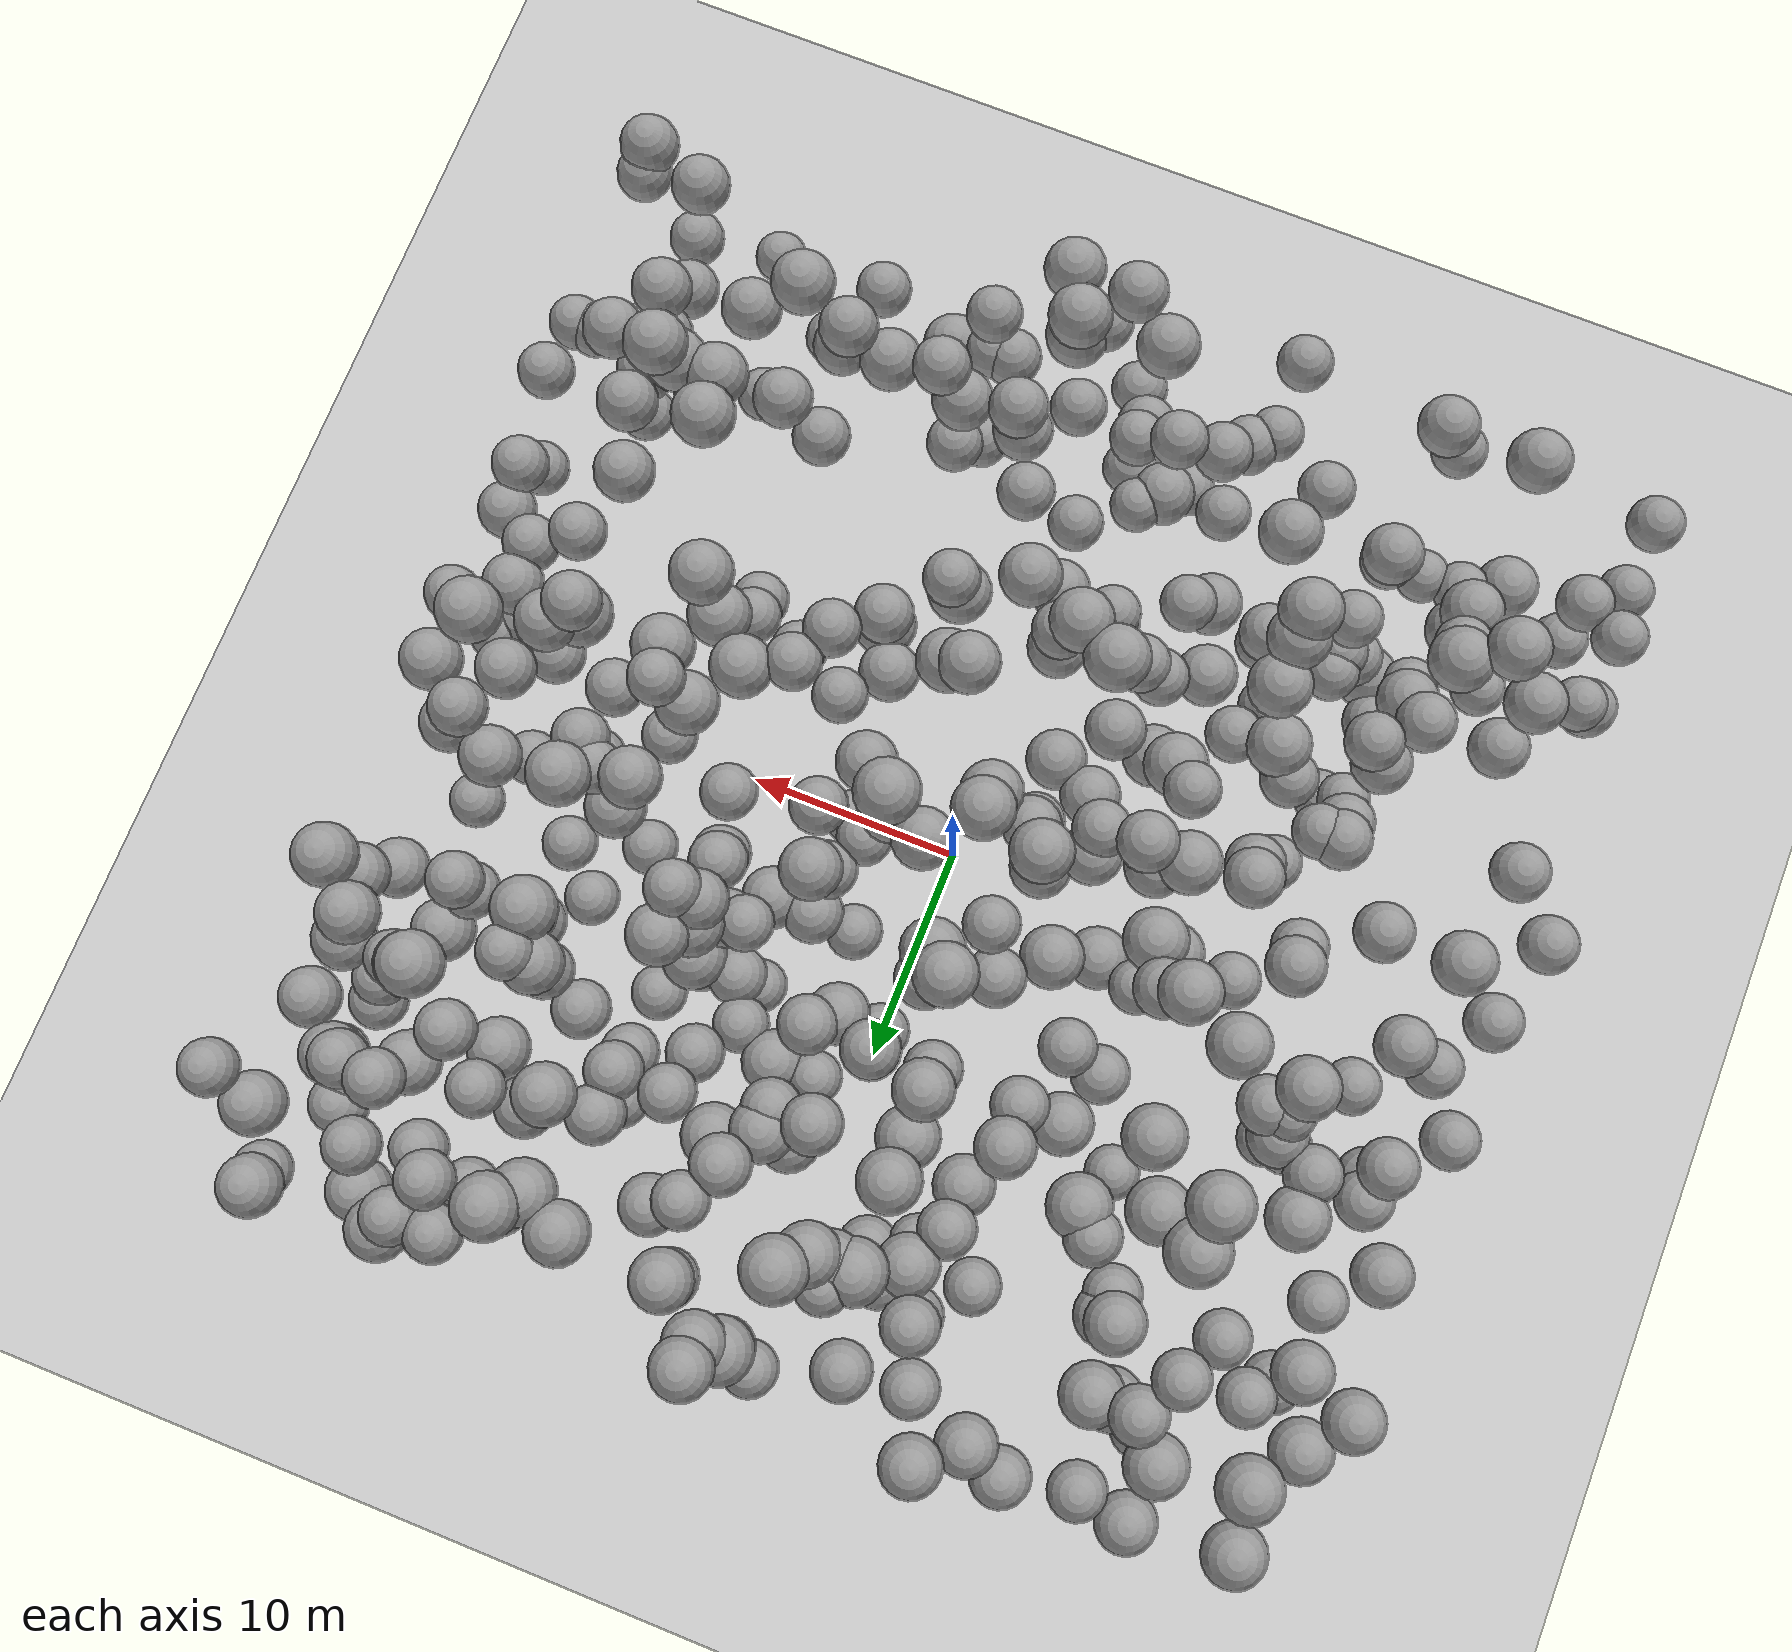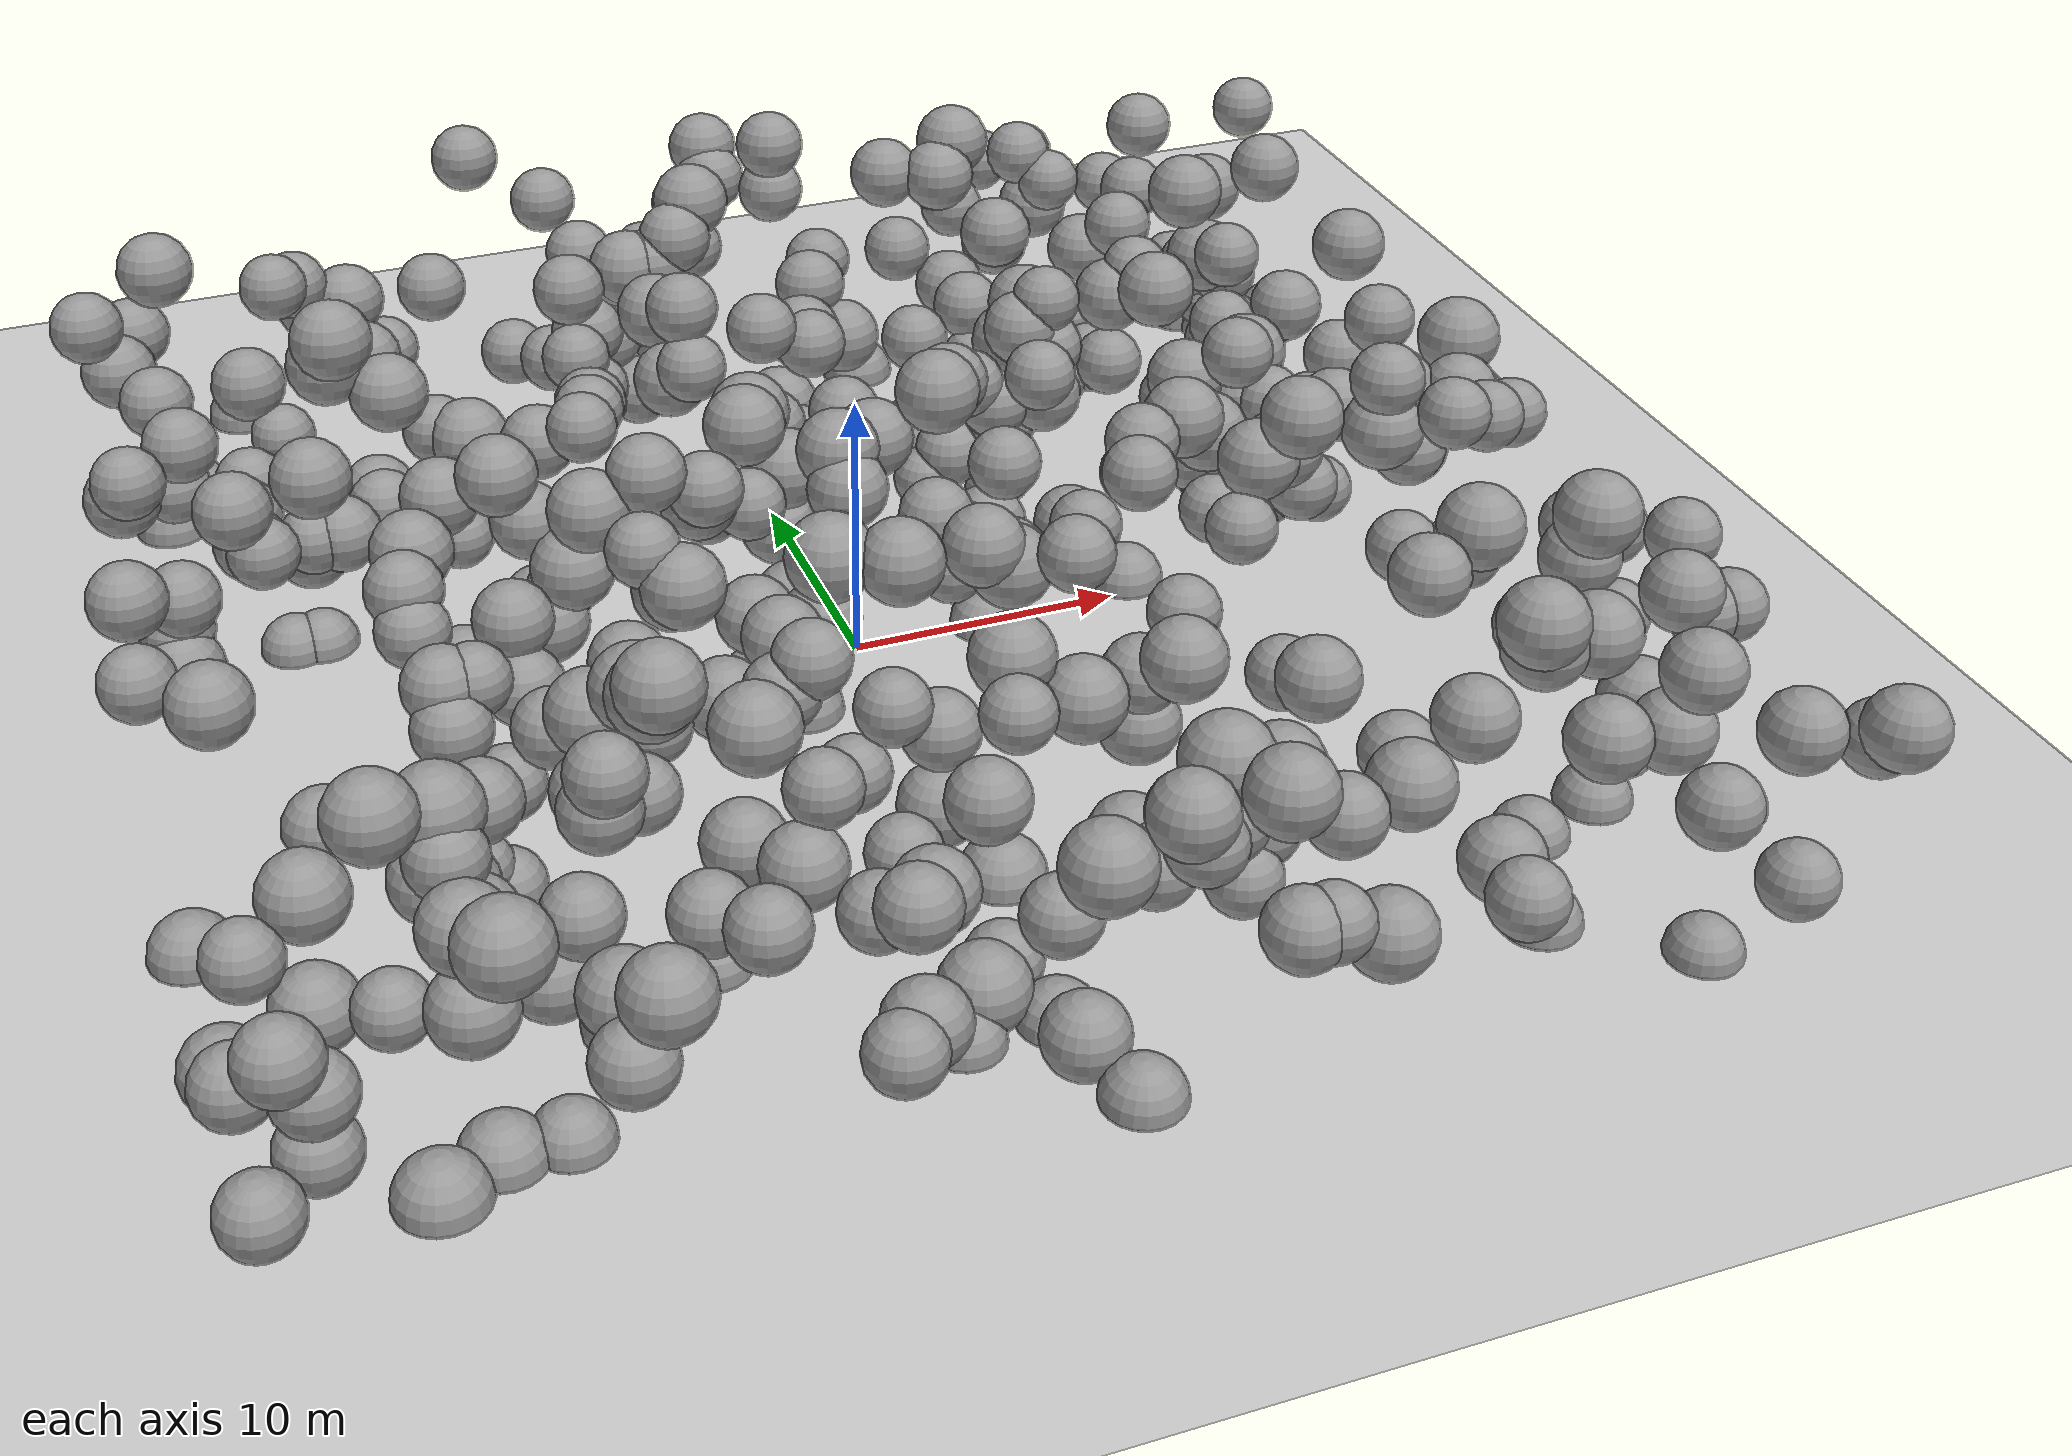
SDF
<?xml version="1.0" ?>
<sdf version='1.7'>
  <world name='default'>
    <light name='sun' type='directional'>
      <cast_shadows>1</cast_shadows>
      <pose>0 0 10 0 -0 0</pose>
      <diffuse>0.8 0.8 0.8 1</diffuse>
      <specular>0.2 0.2 0.2 1</specular>
      <attenuation>
        <range>1000</range>
        <constant>0.9</constant>
        <linear>0.01</linear>
        <quadratic>0.001</quadratic>
      </attenuation>
      <direction>-0.5 0.1 -0.9</direction>
      <spot>
        <inner_angle>0</inner_angle>
        <outer_angle>0</outer_angle>
        <falloff>0</falloff>
      </spot>
    </light>
    <model name='ground_plane'>
      <static>1</static>
      <link name='link'>
        <collision name='collision'>
          <geometry>
            <plane>
              <normal>0 0 1</normal>
              <size>100 100</size>
            </plane>
          </geometry>
          <surface>
            <contact>
              <collide_bitmask>65535</collide_bitmask>
              <ode/>
            </contact>
            <friction>
              <ode>
                <mu>100</mu>
                <mu2>50</mu2>
              </ode>
              <torsional>
                <ode/>
              </torsional>
            </friction>
            <bounce/>
          </surface>
          <max_contacts>10</max_contacts>
        </collision>
        <visual name='visual'>
          <cast_shadows>0</cast_shadows>
          <geometry>
            <plane>
              <normal>0 0 1</normal>
              <size>100 100</size>
            </plane>
          </geometry>
          <material>
            <script>
              <uri>file://media/materials/scripts/gazebo.material</uri>
              <name>Gazebo/Grey</name>
            </script>
          </material>
        </visual>
        <self_collide>0</self_collide>
        <enable_wind>0</enable_wind>
        <kinematic>0</kinematic>
      </link>
    </model>
    <gravity>0 0 -9.8</gravity>
    <magnetic_field>6e-06 2.3e-05 -4.2e-05</magnetic_field>
    <atmosphere type='adiabatic'/>
    <physics type='ode'>
      <max_step_size>0.001</max_step_size>
      <real_time_factor>1</real_time_factor>
      <real_time_update_rate>1000</real_time_update_rate>
    </physics>
    <scene>
      <ambient>0.4 0.4 0.4 1</ambient>
      <background>0.7 0.7 0.7 1</background>
      <shadows>1</shadows>
    </scene>
    <wind/>
    <spherical_coordinates>
      <surface_model>EARTH_WGS84</surface_model>
      <latitude_deg>0</latitude_deg>
      <longitude_deg>0</longitude_deg>
      <elevation>0</elevation>
      <heading_deg>0</heading_deg>
    </spherical_coordinates>

    <model name="sphere_0">
    <static>1</static>
    <pose> 15 12 6 0 0 0 </pose>
      <link name="link">
        <inertial>
          <mass>1278.988058648705</mass>
          <inertia>
            <ixx>1076.7422005173073</ixx>
            <iyy>1076.7422005173073</iyy>
            <izz>1076.7422005173073</izz>
            <ixy>0</ixy>
            <ixz>0</ixz>
            <iyz>0</iyz>
          </inertia>
        </inertial>
        <collision name="collision">
          <geometry>
            <sphere>
              <radius>1.4507501588597562</radius>
            </sphere>
          </geometry>
        </collision>
        <visual name="visual">
          <geometry>
            <sphere>
              <radius>1.4507501588597562</radius>
            </sphere>
          </geometry>
          <material>
            <script>
              <uri>file://media/materials/scripts/gazebo.material</uri>
              <name>Gazebo/Grey</name>
            </script>
          </material>
        </visual>
      </link>
    </model>

    <model name="sphere_1">
    <static>1</static>
    <pose> -3 19 7 0 0 0 </pose>
      <link name="link">
        <inertial>
          <mass>1400.0928152471374</mass>
          <inertia>
            <ixx>1251.9749230556774</ixx>
            <iyy>1251.9749230556774</iyy>
            <izz>1251.9749230556774</izz>
            <ixy>0</ixy>
            <ixz>0</ixz>
            <iyz>0</iyz>
          </inertia>
        </inertial>
        <collision name="collision">
          <geometry>
            <sphere>
              <radius>1.4951659767343175</radius>
            </sphere>
          </geometry>
        </collision>
        <visual name="visual">
          <geometry>
            <sphere>
              <radius>1.4951659767343175</radius>
            </sphere>
          </geometry>
          <material>
            <script>
              <uri>file://media/materials/scripts/gazebo.material</uri>
              <name>Gazebo/Grey</name>
            </script>
          </material>
        </visual>
      </link>
    </model>

    <model name="sphere_2">
    <static>1</static>
    <pose> 0 -15 7 0 0 0 </pose>
      <link name="link">
        <inertial>
          <mass>820.1626990093562</mass>
          <inertia>
            <ixx>513.4532903489413</ixx>
            <iyy>513.4532903489413</iyy>
            <izz>513.4532903489413</izz>
            <ixy>0</ixy>
            <ixz>0</ixz>
            <iyz>0</iyz>
          </inertia>
        </inertial>
        <collision name="collision">
          <geometry>
            <sphere>
              <radius>1.2510379038973842</radius>
            </sphere>
          </geometry>
        </collision>
        <visual name="visual">
          <geometry>
            <sphere>
              <radius>1.2510379038973842</radius>
            </sphere>
          </geometry>
          <material>
            <script>
              <uri>file://media/materials/scripts/gazebo.material</uri>
              <name>Gazebo/Grey</name>
            </script>
          </material>
        </visual>
      </link>
    </model>

    <model name="sphere_3">
    <static>1</static>
    <pose> 10 11 2 0 0 0 </pose>
      <link name="link">
        <inertial>
          <mass>868.9831357294986</mass>
          <inertia>
            <ixx>565.3965647869163</ixx>
            <iyy>565.3965647869163</iyy>
            <izz>565.3965647869163</izz>
            <ixy>0</ixy>
            <ixz>0</ixz>
            <iyz>0</iyz>
          </inertia>
        </inertial>
        <collision name="collision">
          <geometry>
            <sphere>
              <radius>1.275383849102163</radius>
            </sphere>
          </geometry>
        </collision>
        <visual name="visual">
          <geometry>
            <sphere>
              <radius>1.275383849102163</radius>
            </sphere>
          </geometry>
          <material>
            <script>
              <uri>file://media/materials/scripts/gazebo.material</uri>
              <name>Gazebo/Grey</name>
            </script>
          </material>
        </visual>
      </link>
    </model>

    <model name="sphere_4">
    <static>1</static>
    <pose> -16 11 10 0 0 0 </pose>
      <link name="link">
        <inertial>
          <mass>1349.4065213395008</mass>
          <inertia>
            <ixx>1177.3500128853816</ixx>
            <iyy>1177.3500128853816</iyy>
            <izz>1177.3500128853816</izz>
            <ixy>0</ixy>
            <ixz>0</ixz>
            <iyz>0</iyz>
          </inertia>
        </inertial>
        <collision name="collision">
          <geometry>
            <sphere>
              <radius>1.476901047275942</radius>
            </sphere>
          </geometry>
        </collision>
        <visual name="visual">
          <geometry>
            <sphere>
              <radius>1.476901047275942</radius>
            </sphere>
          </geometry>
          <material>
            <script>
              <uri>file://media/materials/scripts/gazebo.material</uri>
              <name>Gazebo/Grey</name>
            </script>
          </material>
        </visual>
      </link>
    </model>

    <model name="sphere_5">
    <static>1</static>
    <pose> -4 -11 3 0 0 0 </pose>
      <link name="link">
        <inertial>
          <mass>911.1555626264419</mass>
          <inertia>
            <ixx>611.8643311993161</ixx>
            <iyy>611.8643311993161</iyy>
            <izz>611.8643311993161</izz>
            <ixy>0</ixy>
            <ixz>0</ixz>
            <iyz>0</iyz>
          </inertia>
        </inertial>
        <collision name="collision">
          <geometry>
            <sphere>
              <radius>1.2956905974533777</radius>
            </sphere>
          </geometry>
        </collision>
        <visual name="visual">
          <geometry>
            <sphere>
              <radius>1.2956905974533777</radius>
            </sphere>
          </geometry>
          <material>
            <script>
              <uri>file://media/materials/scripts/gazebo.material</uri>
              <name>Gazebo/Grey</name>
            </script>
          </material>
        </visual>
      </link>
    </model>

    <model name="sphere_6">
    <static>1</static>
    <pose> -2 -19 1 0 0 0 </pose>
      <link name="link">
        <inertial>
          <mass>893.9040352386924</mass>
          <inertia>
            <ixx>592.6783749071067</ixx>
            <iyy>592.6783749071067</iyy>
            <izz>592.6783749071067</izz>
            <ixy>0</ixy>
            <ixz>0</ixz>
            <iyz>0</iyz>
          </inertia>
        </inertial>
        <collision name="collision">
          <geometry>
            <sphere>
              <radius>1.2874610414067271</radius>
            </sphere>
          </geometry>
        </collision>
        <visual name="visual">
          <geometry>
            <sphere>
              <radius>1.2874610414067271</radius>
            </sphere>
          </geometry>
          <material>
            <script>
              <uri>file://media/materials/scripts/gazebo.material</uri>
              <name>Gazebo/Grey</name>
            </script>
          </material>
        </visual>
      </link>
    </model>

    <model name="sphere_7">
    <static>1</static>
    <pose> 3 5 0 0 0 0 </pose>
      <link name="link">
        <inertial>
          <mass>956.1983310842588</mass>
          <inertia>
            <ixx>663.102839138089</ixx>
            <iyy>663.102839138089</iyy>
            <izz>663.102839138089</izz>
            <ixy>0</ixy>
            <ixz>0</ixz>
            <iyz>0</iyz>
          </inertia>
        </inertial>
        <collision name="collision">
          <geometry>
            <sphere>
              <radius>1.3166988533295256</radius>
            </sphere>
          </geometry>
        </collision>
        <visual name="visual">
          <geometry>
            <sphere>
              <radius>1.3166988533295256</radius>
            </sphere>
          </geometry>
          <material>
            <script>
              <uri>file://media/materials/scripts/gazebo.material</uri>
              <name>Gazebo/Grey</name>
            </script>
          </material>
        </visual>
      </link>
    </model>

    <model name="sphere_8">
    <static>1</static>
    <pose> -3 -20 8 0 0 0 </pose>
      <link name="link">
        <inertial>
          <mass>945.1358322652695</mass>
          <inertia>
            <ixx>650.3662052603468</ixx>
            <iyy>650.3662052603468</iyy>
            <izz>650.3662052603468</izz>
            <ixy>0</ixy>
            <ixz>0</ixz>
            <iyz>0</iyz>
          </inertia>
        </inertial>
        <collision name="collision">
          <geometry>
            <sphere>
              <radius>1.3116014046180922</radius>
            </sphere>
          </geometry>
        </collision>
        <visual name="visual">
          <geometry>
            <sphere>
              <radius>1.3116014046180922</radius>
            </sphere>
          </geometry>
          <material>
            <script>
              <uri>file://media/materials/scripts/gazebo.material</uri>
              <name>Gazebo/Grey</name>
            </script>
          </material>
        </visual>
      </link>
    </model>

    <model name="sphere_9">
    <static>1</static>
    <pose> 3 10 4 0 0 0 </pose>
      <link name="link">
        <inertial>
          <mass>1079.731441712118</mass>
          <inertia>
            <ixx>811.9460351600522</ixx>
            <iyy>811.9460351600522</iyy>
            <izz>811.9460351600522</izz>
            <ixy>0</ixy>
            <ixz>0</ixz>
            <iyz>0</iyz>
          </inertia>
        </inertial>
        <collision name="collision">
          <geometry>
            <sphere>
              <radius>1.3711207804046117</radius>
            </sphere>
          </geometry>
        </collision>
        <visual name="visual">
          <geometry>
            <sphere>
              <radius>1.3711207804046117</radius>
            </sphere>
          </geometry>
          <material>
            <script>
              <uri>file://media/materials/scripts/gazebo.material</uri>
              <name>Gazebo/Grey</name>
            </script>
          </material>
        </visual>
      </link>
    </model>

    <model name="sphere_10">
    <static>1</static>
    <pose> -4 19 4 0 0 0 </pose>
      <link name="link">
        <inertial>
          <mass>1096.0715494803826</mass>
          <inertia>
            <ixx>832.5284689298377</ixx>
            <iyy>832.5284689298377</iyy>
            <izz>832.5284689298377</izz>
            <ixy>0</ixy>
            <ixz>0</ixz>
            <iyz>0</iyz>
          </inertia>
        </inertial>
        <collision name="collision">
          <geometry>
            <sphere>
              <radius>1.3780027953613165</radius>
            </sphere>
          </geometry>
        </collision>
        <visual name="visual">
          <geometry>
            <sphere>
              <radius>1.3780027953613165</radius>
            </sphere>
          </geometry>
          <material>
            <script>
              <uri>file://media/materials/scripts/gazebo.material</uri>
              <name>Gazebo/Grey</name>
            </script>
          </material>
        </visual>
      </link>
    </model>

    <model name="sphere_11">
    <static>1</static>
    <pose> 1 24 5 0 0 0 </pose>
      <link name="link">
        <inertial>
          <mass>1003.4708876810511</mass>
          <inertia>
            <ixx>718.6358535089698</ixx>
            <iyy>718.6358535089698</iyy>
            <izz>718.6358535089698</izz>
            <ixy>0</ixy>
            <ixz>0</ixz>
            <iyz>0</iyz>
          </inertia>
        </inertial>
        <collision name="collision">
          <geometry>
            <sphere>
              <radius>1.3380491178231635</radius>
            </sphere>
          </geometry>
        </collision>
        <visual name="visual">
          <geometry>
            <sphere>
              <radius>1.3380491178231635</radius>
            </sphere>
          </geometry>
          <material>
            <script>
              <uri>file://media/materials/scripts/gazebo.material</uri>
              <name>Gazebo/Grey</name>
            </script>
          </material>
        </visual>
      </link>
    </model>

    <model name="sphere_12">
    <static>1</static>
    <pose> 3 0 5 0 0 0 </pose>
      <link name="link">
        <inertial>
          <mass>1038.9067276165363</mass>
          <inertia>
            <ixx>761.4274268296156</ixx>
            <iyy>761.4274268296156</iyy>
            <izz>761.4274268296156</izz>
            <ixy>0</ixy>
            <ixz>0</ixz>
            <iyz>0</iyz>
          </inertia>
        </inertial>
        <collision name="collision">
          <geometry>
            <sphere>
              <radius>1.353617570684946</radius>
            </sphere>
          </geometry>
        </collision>
        <visual name="visual">
          <geometry>
            <sphere>
              <radius>1.353617570684946</radius>
            </sphere>
          </geometry>
          <material>
            <script>
              <uri>file://media/materials/scripts/gazebo.material</uri>
              <name>Gazebo/Grey</name>
            </script>
          </material>
        </visual>
      </link>
    </model>

    <model name="sphere_13">
    <static>1</static>
    <pose> -7 12 10 0 0 0 </pose>
      <link name="link">
        <inertial>
          <mass>933.9682048326795</mass>
          <inertia>
            <ixx>637.6089502544005</ixx>
            <iyy>637.6089502544005</iyy>
            <izz>637.6089502544005</izz>
            <ixy>0</ixy>
            <ixz>0</ixz>
            <iyz>0</iyz>
          </inertia>
        </inertial>
        <collision name="collision">
          <geometry>
            <sphere>
              <radius>1.3064150077493173</radius>
            </sphere>
          </geometry>
        </collision>
        <visual name="visual">
          <geometry>
            <sphere>
              <radius>1.3064150077493173</radius>
            </sphere>
          </geometry>
          <material>
            <script>
              <uri>file://media/materials/scripts/gazebo.material</uri>
              <name>Gazebo/Grey</name>
            </script>
          </material>
        </visual>
      </link>
    </model>

    <model name="sphere_14">
    <static>1</static>
    <pose> 17 25 4 0 0 0 </pose>
      <link name="link">
        <inertial>
          <mass>1322.0387221128017</mass>
          <inertia>
            <ixx>1137.822570965103</ixx>
            <iyy>1137.822570965103</iyy>
            <izz>1137.822570965103</izz>
            <ixy>0</ixy>
            <ixz>0</ixz>
            <iyz>0</iyz>
          </inertia>
        </inertial>
        <collision name="collision">
          <geometry>
            <sphere>
              <radius>1.4668482558747977</radius>
            </sphere>
          </geometry>
        </collision>
        <visual name="visual">
          <geometry>
            <sphere>
              <radius>1.4668482558747977</radius>
            </sphere>
          </geometry>
          <material>
            <script>
              <uri>file://media/materials/scripts/gazebo.material</uri>
              <name>Gazebo/Grey</name>
            </script>
          </material>
        </visual>
      </link>
    </model>

    <model name="sphere_15">
    <static>1</static>
    <pose> 7 13 5 0 0 0 </pose>
      <link name="link">
        <inertial>
          <mass>923.8683063553028</mass>
          <inertia>
            <ixx>626.1586238649431</ixx>
            <iyy>626.1586238649431</iyy>
            <izz>626.1586238649431</izz>
            <ixy>0</ixy>
            <ixz>0</ixz>
            <iyz>0</iyz>
          </inertia>
        </inertial>
        <collision name="collision">
          <geometry>
            <sphere>
              <radius>1.3016887551544614</radius>
            </sphere>
          </geometry>
        </collision>
        <visual name="visual">
          <geometry>
            <sphere>
              <radius>1.3016887551544614</radius>
            </sphere>
          </geometry>
          <material>
            <script>
              <uri>file://media/materials/scripts/gazebo.material</uri>
              <name>Gazebo/Grey</name>
            </script>
          </material>
        </visual>
      </link>
    </model>

    <model name="sphere_16">
    <static>1</static>
    <pose> 25 -7 4 0 0 0 </pose>
      <link name="link">
        <inertial>
          <mass>1047.0550115686524</mass>
          <inertia>
            <ixx>771.4067205637532</ixx>
            <iyy>771.4067205637532</iyy>
            <izz>771.4067205637532</izz>
            <ixy>0</ixy>
            <ixz>0</ixz>
            <iyz>0</iyz>
          </inertia>
        </inertial>
        <collision name="collision">
          <geometry>
            <sphere>
              <radius>1.3571472265336735</radius>
            </sphere>
          </geometry>
        </collision>
        <visual name="visual">
          <geometry>
            <sphere>
              <radius>1.3571472265336735</radius>
            </sphere>
          </geometry>
          <material>
            <script>
              <uri>file://media/materials/scripts/gazebo.material</uri>
              <name>Gazebo/Grey</name>
            </script>
          </material>
        </visual>
      </link>
    </model>

    <model name="sphere_17">
    <static>1</static>
    <pose> 4 -10 9 0 0 0 </pose>
      <link name="link">
        <inertial>
          <mass>874.7729072754648</mass>
          <inertia>
            <ixx>571.6889418360142</ixx>
            <iyy>571.6889418360142</iyy>
            <izz>571.6889418360142</izz>
            <ixy>0</ixy>
            <ixz>0</ixz>
            <iyz>0</iyz>
          </inertia>
        </inertial>
        <collision name="collision">
          <geometry>
            <sphere>
              <radius>1.278210080410224</radius>
            </sphere>
          </geometry>
        </collision>
        <visual name="visual">
          <geometry>
            <sphere>
              <radius>1.278210080410224</radius>
            </sphere>
          </geometry>
          <material>
            <script>
              <uri>file://media/materials/scripts/gazebo.material</uri>
              <name>Gazebo/Grey</name>
            </script>
          </material>
        </visual>
      </link>
    </model>

    <model name="sphere_18">
    <static>1</static>
    <pose> 21 -13 7 0 0 0 </pose>
      <link name="link">
        <inertial>
          <mass>1147.8261144888318</mass>
          <inertia>
            <ixx>899.0718924111744</ixx>
            <iyy>899.0718924111744</iyy>
            <izz>899.0718924111744</izz>
            <ixy>0</ixy>
            <ixz>0</ixz>
            <iyz>0</iyz>
          </inertia>
        </inertial>
        <collision name="collision">
          <geometry>
            <sphere>
              <radius>1.3993590601785768</radius>
            </sphere>
          </geometry>
        </collision>
        <visual name="visual">
          <geometry>
            <sphere>
              <radius>1.3993590601785768</radius>
            </sphere>
          </geometry>
          <material>
            <script>
              <uri>file://media/materials/scripts/gazebo.material</uri>
              <name>Gazebo/Grey</name>
            </script>
          </material>
        </visual>
      </link>
    </model>

    <model name="sphere_19">
    <static>1</static>
    <pose> -5 -7 6 0 0 0 </pose>
      <link name="link">
        <inertial>
          <mass>1093.7044318353844</mass>
          <inertia>
            <ixx>829.5340265991515</ixx>
            <iyy>829.5340265991515</iyy>
            <izz>829.5340265991515</izz>
            <ixy>0</ixy>
            <ixz>0</ixz>
            <iyz>0</iyz>
          </inertia>
        </inertial>
        <collision name="collision">
          <geometry>
            <sphere>
              <radius>1.3770100847044313</radius>
            </sphere>
          </geometry>
        </collision>
        <visual name="visual">
          <geometry>
            <sphere>
              <radius>1.3770100847044313</radius>
            </sphere>
          </geometry>
          <material>
            <script>
              <uri>file://media/materials/scripts/gazebo.material</uri>
              <name>Gazebo/Grey</name>
            </script>
          </material>
        </visual>
      </link>
    </model>

    <model name="sphere_20">
    <static>1</static>
    <pose> -12 -9 6 0 0 0 </pose>
      <link name="link">
        <inertial>
          <mass>1336.6317615630337</mass>
          <inertia>
            <ixx>1158.8321791067362</ixx>
            <iyy>1158.8321791067362</iyy>
            <izz>1158.8321791067362</izz>
            <ixy>0</ixy>
            <ixz>0</ixz>
            <iyz>0</iyz>
          </inertia>
        </inertial>
        <collision name="collision">
          <geometry>
            <sphere>
              <radius>1.4722256810506325</radius>
            </sphere>
          </geometry>
        </collision>
        <visual name="visual">
          <geometry>
            <sphere>
              <radius>1.4722256810506325</radius>
            </sphere>
          </geometry>
          <material>
            <script>
              <uri>file://media/materials/scripts/gazebo.material</uri>
              <name>Gazebo/Grey</name>
            </script>
          </material>
        </visual>
      </link>
    </model>

    <model name="sphere_21">
    <static>1</static>
    <pose> 19 22 6 0 0 0 </pose>
      <link name="link">
        <inertial>
          <mass>886.9974340022904</mass>
          <inertia>
            <ixx>585.0659958478017</ixx>
            <iyy>585.0659958478017</iyy>
            <izz>585.0659958478017</izz>
            <ixy>0</ixy>
            <ixz>0</ixz>
            <iyz>0</iyz>
          </inertia>
        </inertial>
        <collision name="collision">
          <geometry>
            <sphere>
              <radius>1.2841366802223042</radius>
            </sphere>
          </geometry>
        </collision>
        <visual name="visual">
          <geometry>
            <sphere>
              <radius>1.2841366802223042</radius>
            </sphere>
          </geometry>
          <material>
            <script>
              <uri>file://media/materials/scripts/gazebo.material</uri>
              <name>Gazebo/Grey</name>
            </script>
          </material>
        </visual>
      </link>
    </model>

    <model name="sphere_22">
    <static>1</static>
    <pose> 5 19 6 0 0 0 </pose>
      <link name="link">
        <inertial>
          <mass>912.9290711376584</mass>
          <inertia>
            <ixx>613.8505461930362</ixx>
            <iyy>613.8505461930362</iyy>
            <izz>613.8505461930362</izz>
            <ixy>0</ixy>
            <ixz>0</ixz>
            <iyz>0</iyz>
          </inertia>
        </inertial>
        <collision name="collision">
          <geometry>
            <sphere>
              <radius>1.2965307134144402</radius>
            </sphere>
          </geometry>
        </collision>
        <visual name="visual">
          <geometry>
            <sphere>
              <radius>1.2965307134144402</radius>
            </sphere>
          </geometry>
          <material>
            <script>
              <uri>file://media/materials/scripts/gazebo.material</uri>
              <name>Gazebo/Grey</name>
            </script>
          </material>
        </visual>
      </link>
    </model>

    <model name="sphere_23">
    <static>1</static>
    <pose> -2 20 7 0 0 0 </pose>
      <link name="link">
        <inertial>
          <mass>898.4752685543261</mass>
          <inertia>
            <ixx>597.7383638554867</ixx>
            <iyy>597.7383638554867</iyy>
            <izz>597.7383638554867</izz>
            <ixy>0</ixy>
            <ixz>0</ixz>
            <iyz>0</iyz>
          </inertia>
        </inertial>
        <collision name="collision">
          <geometry>
            <sphere>
              <radius>1.2896519108773912</radius>
            </sphere>
          </geometry>
        </collision>
        <visual name="visual">
          <geometry>
            <sphere>
              <radius>1.2896519108773912</radius>
            </sphere>
          </geometry>
          <material>
            <script>
              <uri>file://media/materials/scripts/gazebo.material</uri>
              <name>Gazebo/Grey</name>
            </script>
          </material>
        </visual>
      </link>
    </model>

    <model name="sphere_24">
    <static>1</static>
    <pose> -11 13 4 0 0 0 </pose>
      <link name="link">
        <inertial>
          <mass>1403.5700648880909</mass>
          <inertia>
            <ixx>1257.1615225295525</ixx>
            <iyy>1257.1615225295525</iyy>
            <izz>1257.1615225295525</izz>
            <ixy>0</ixy>
            <ixz>0</ixz>
            <iyz>0</iyz>
          </inertia>
        </inertial>
        <collision name="collision">
          <geometry>
            <sphere>
              <radius>1.4964027440688321</radius>
            </sphere>
          </geometry>
        </collision>
        <visual name="visual">
          <geometry>
            <sphere>
              <radius>1.4964027440688321</radius>
            </sphere>
          </geometry>
          <material>
            <script>
              <uri>file://media/materials/scripts/gazebo.material</uri>
              <name>Gazebo/Grey</name>
            </script>
          </material>
        </visual>
      </link>
    </model>

    <model name="sphere_25">
    <static>1</static>
    <pose> -16 -13 1 0 0 0 </pose>
      <link name="link">
        <inertial>
          <mass>1045.2013214133608</mass>
          <inertia>
            <ixx>769.1319196404364</ixx>
            <iyy>769.1319196404364</iyy>
            <izz>769.1319196404364</izz>
            <ixy>0</ixy>
            <ixz>0</ixz>
            <iyz>0</iyz>
          </inertia>
        </inertial>
        <collision name="collision">
          <geometry>
            <sphere>
              <radius>1.356345862552236</radius>
            </sphere>
          </geometry>
        </collision>
        <visual name="visual">
          <geometry>
            <sphere>
              <radius>1.356345862552236</radius>
            </sphere>
          </geometry>
          <material>
            <script>
              <uri>file://media/materials/scripts/gazebo.material</uri>
              <name>Gazebo/Grey</name>
            </script>
          </material>
        </visual>
      </link>
    </model>

    <model name="sphere_26">
    <static>1</static>
    <pose> -15 -6 6 0 0 0 </pose>
      <link name="link">
        <inertial>
          <mass>847.9089603285704</mass>
          <inertia>
            <ixx>542.7289144185544</ixx>
            <iyy>542.7289144185544</iyy>
            <izz>542.7289144185544</izz>
            <ixy>0</ixy>
            <ixz>0</ixz>
            <iyz>0</iyz>
          </inertia>
        </inertial>
        <collision name="collision">
          <geometry>
            <sphere>
              <radius>1.2649893576409998</radius>
            </sphere>
          </geometry>
        </collision>
        <visual name="visual">
          <geometry>
            <sphere>
              <radius>1.2649893576409998</radius>
            </sphere>
          </geometry>
          <material>
            <script>
              <uri>file://media/materials/scripts/gazebo.material</uri>
              <name>Gazebo/Grey</name>
            </script>
          </material>
        </visual>
      </link>
    </model>

    <model name="sphere_27">
    <static>1</static>
    <pose> 3 14 5 0 0 0 </pose>
      <link name="link">
        <inertial>
          <mass>1061.8361056163462</mass>
          <inertia>
            <ixx>789.6416841092197</ixx>
            <iyy>789.6416841092197</iyy>
            <izz>789.6416841092197</izz>
            <ixy>0</ixy>
            <ixz>0</ixz>
            <iyz>0</iyz>
          </inertia>
        </inertial>
        <collision name="collision">
          <geometry>
            <sphere>
              <radius>1.3635036130666054</radius>
            </sphere>
          </geometry>
        </collision>
        <visual name="visual">
          <geometry>
            <sphere>
              <radius>1.3635036130666054</radius>
            </sphere>
          </geometry>
          <material>
            <script>
              <uri>file://media/materials/scripts/gazebo.material</uri>
              <name>Gazebo/Grey</name>
            </script>
          </material>
        </visual>
      </link>
    </model>

    <model name="sphere_28">
    <static>1</static>
    <pose> -17 21 1 0 0 0 </pose>
      <link name="link">
        <inertial>
          <mass>875.8497790981718</mass>
          <inertia>
            <ixx>572.8623669523987</ixx>
            <iyy>572.8623669523987</iyy>
            <izz>572.8623669523987</izz>
            <ixy>0</ixy>
            <ixz>0</ixz>
            <iyz>0</iyz>
          </inertia>
        </inertial>
        <collision name="collision">
          <geometry>
            <sphere>
              <radius>1.2787343703788596</radius>
            </sphere>
          </geometry>
        </collision>
        <visual name="visual">
          <geometry>
            <sphere>
              <radius>1.2787343703788596</radius>
            </sphere>
          </geometry>
          <material>
            <script>
              <uri>file://media/materials/scripts/gazebo.material</uri>
              <name>Gazebo/Grey</name>
            </script>
          </material>
        </visual>
      </link>
    </model>

    <model name="sphere_29">
    <static>1</static>
    <pose> -15 20 5 0 0 0 </pose>
      <link name="link">
        <inertial>
          <mass>1176.2609769681565</mass>
          <inertia>
            <ixx>936.4984595494084</ixx>
            <iyy>936.4984595494084</iyy>
            <izz>936.4984595494084</izz>
            <ixy>0</ixy>
            <ixz>0</ixz>
            <iyz>0</iyz>
          </inertia>
        </inertial>
        <collision name="collision">
          <geometry>
            <sphere>
              <radius>1.41082027832666</radius>
            </sphere>
          </geometry>
        </collision>
        <visual name="visual">
          <geometry>
            <sphere>
              <radius>1.41082027832666</radius>
            </sphere>
          </geometry>
          <material>
            <script>
              <uri>file://media/materials/scripts/gazebo.material</uri>
              <name>Gazebo/Grey</name>
            </script>
          </material>
        </visual>
      </link>
    </model>

    <model name="sphere_30">
    <static>1</static>
    <pose> 5 -2 4 0 0 0 </pose>
      <link name="link">
        <inertial>
          <mass>1243.6143407007764</mass>
          <inertia>
            <ixx>1027.5677231437348</ixx>
            <iyy>1027.5677231437348</iyy>
            <izz>1027.5677231437348</izz>
            <ixy>0</ixy>
            <ixz>0</ixz>
            <iyz>0</iyz>
          </inertia>
        </inertial>
        <collision name="collision">
          <geometry>
            <sphere>
              <radius>1.4372501767182697</radius>
            </sphere>
          </geometry>
        </collision>
        <visual name="visual">
          <geometry>
            <sphere>
              <radius>1.4372501767182697</radius>
            </sphere>
          </geometry>
          <material>
            <script>
              <uri>file://media/materials/scripts/gazebo.material</uri>
              <name>Gazebo/Grey</name>
            </script>
          </material>
        </visual>
      </link>
    </model>

    <model name="sphere_31">
    <static>1</static>
    <pose> 10 14 3 0 0 0 </pose>
      <link name="link">
        <inertial>
          <mass>974.4408386224361</mass>
          <inertia>
            <ixx>684.3212820842285</ixx>
            <iyy>684.3212820842285</iyy>
            <izz>684.3212820842285</izz>
            <ixy>0</ixy>
            <ixz>0</ixz>
            <iyz>0</iyz>
          </inertia>
        </inertial>
        <collision name="collision">
          <geometry>
            <sphere>
              <radius>1.3250195593667726</radius>
            </sphere>
          </geometry>
        </collision>
        <visual name="visual">
          <geometry>
            <sphere>
              <radius>1.3250195593667726</radius>
            </sphere>
          </geometry>
          <material>
            <script>
              <uri>file://media/materials/scripts/gazebo.material</uri>
              <name>Gazebo/Grey</name>
            </script>
          </material>
        </visual>
      </link>
    </model>

    <model name="sphere_32">
    <static>1</static>
    <pose> -23 7 0 0 0 0 </pose>
      <link name="link">
        <inertial>
          <mass>1402.8813819536108</mass>
          <inertia>
            <ixx>1256.1336150803506</ixx>
            <iyy>1256.1336150803506</iyy>
            <izz>1256.1336150803506</izz>
            <ixy>0</ixy>
            <ixz>0</ixz>
            <iyz>0</iyz>
          </inertia>
        </inertial>
        <collision name="collision">
          <geometry>
            <sphere>
              <radius>1.4961579597967176</radius>
            </sphere>
          </geometry>
        </collision>
        <visual name="visual">
          <geometry>
            <sphere>
              <radius>1.4961579597967176</radius>
            </sphere>
          </geometry>
          <material>
            <script>
              <uri>file://media/materials/scripts/gazebo.material</uri>
              <name>Gazebo/Grey</name>
            </script>
          </material>
        </visual>
      </link>
    </model>

    <model name="sphere_33">
    <static>1</static>
    <pose> 23 -24 1 0 0 0 </pose>
      <link name="link">
        <inertial>
          <mass>998.2394421149766</mass>
          <inertia>
            <ixx>712.4025430400376</ixx>
            <iyy>712.4025430400376</iyy>
            <izz>712.4025430400376</izz>
            <ixy>0</ixy>
            <ixz>0</ixz>
            <iyz>0</iyz>
          </inertia>
        </inertial>
        <collision name="collision">
          <geometry>
            <sphere>
              <radius>1.3357198255867795</radius>
            </sphere>
          </geometry>
        </collision>
        <visual name="visual">
          <geometry>
            <sphere>
              <radius>1.3357198255867795</radius>
            </sphere>
          </geometry>
          <material>
            <script>
              <uri>file://media/materials/scripts/gazebo.material</uri>
              <name>Gazebo/Grey</name>
            </script>
          </material>
        </visual>
      </link>
    </model>

    <model name="sphere_34">
    <static>1</static>
    <pose> -10 24 5 0 0 0 </pose>
      <link name="link">
        <inertial>
          <mass>1102.099609550624</mass>
          <inertia>
            <ixx>840.1735387916111</ixx>
            <iyy>840.1735387916111</iyy>
            <izz>840.1735387916111</izz>
            <ixy>0</ixy>
            <ixz>0</ixz>
            <iyz>0</iyz>
          </inertia>
        </inertial>
        <collision name="collision">
          <geometry>
            <sphere>
              <radius>1.3805243770687237</radius>
            </sphere>
          </geometry>
        </collision>
        <visual name="visual">
          <geometry>
            <sphere>
              <radius>1.3805243770687237</radius>
            </sphere>
          </geometry>
          <material>
            <script>
              <uri>file://media/materials/scripts/gazebo.material</uri>
              <name>Gazebo/Grey</name>
            </script>
          </material>
        </visual>
      </link>
    </model>

    <model name="sphere_35">
    <static>1</static>
    <pose> -6 -19 4 0 0 0 </pose>
      <link name="link">
        <inertial>
          <mass>884.3200558352077</mass>
          <inertia>
            <ixx>582.125614726622</ixx>
            <iyy>582.125614726622</iyy>
            <izz>582.125614726622</izz>
            <ixy>0</ixy>
            <ixz>0</ixz>
            <iyz>0</iyz>
          </inertia>
        </inertial>
        <collision name="collision">
          <geometry>
            <sphere>
              <radius>1.2828433338973109</radius>
            </sphere>
          </geometry>
        </collision>
        <visual name="visual">
          <geometry>
            <sphere>
              <radius>1.2828433338973109</radius>
            </sphere>
          </geometry>
          <material>
            <script>
              <uri>file://media/materials/scripts/gazebo.material</uri>
              <name>Gazebo/Grey</name>
            </script>
          </material>
        </visual>
      </link>
    </model>

    <model name="sphere_36">
    <static>1</static>
    <pose> 4 22 10 0 0 0 </pose>
      <link name="link">
        <inertial>
          <mass>1033.9862029616484</mass>
          <inertia>
            <ixx>755.4263999389774</ixx>
            <iyy>755.4263999389774</iyy>
            <izz>755.4263999389774</izz>
            <ixy>0</ixy>
            <ixz>0</ixz>
            <iyz>0</iyz>
          </inertia>
        </inertial>
        <collision name="collision">
          <geometry>
            <sphere>
              <radius>1.35147716305186</radius>
            </sphere>
          </geometry>
        </collision>
        <visual name="visual">
          <geometry>
            <sphere>
              <radius>1.35147716305186</radius>
            </sphere>
          </geometry>
          <material>
            <script>
              <uri>file://media/materials/scripts/gazebo.material</uri>
              <name>Gazebo/Grey</name>
            </script>
          </material>
        </visual>
      </link>
    </model>

    <model name="sphere_37">
    <static>1</static>
    <pose> 6 -19 2 0 0 0 </pose>
      <link name="link">
        <inertial>
          <mass>923.9607349359668</mass>
          <inertia>
            <ixx>626.2630342780069</ixx>
            <iyy>626.2630342780069</iyy>
            <izz>626.2630342780069</izz>
            <ixy>0</ixy>
            <ixz>0</ixz>
            <iyz>0</iyz>
          </inertia>
        </inertial>
        <collision name="collision">
          <geometry>
            <sphere>
              <radius>1.301732162940054</radius>
            </sphere>
          </geometry>
        </collision>
        <visual name="visual">
          <geometry>
            <sphere>
              <radius>1.301732162940054</radius>
            </sphere>
          </geometry>
          <material>
            <script>
              <uri>file://media/materials/scripts/gazebo.material</uri>
              <name>Gazebo/Grey</name>
            </script>
          </material>
        </visual>
      </link>
    </model>

    <model name="sphere_38">
    <static>1</static>
    <pose> -9 -17 10 0 0 0 </pose>
      <link name="link">
        <inertial>
          <mass>1162.2410811386037</mass>
          <inertia>
            <ixx>917.9688735033643</ixx>
            <iyy>917.9688735033643</iyy>
            <izz>917.9688735033643</izz>
            <ixy>0</ixy>
            <ixz>0</ixz>
            <iyz>0</iyz>
          </inertia>
        </inertial>
        <collision name="collision">
          <geometry>
            <sphere>
              <radius>1.4051926546801257</radius>
            </sphere>
          </geometry>
        </collision>
        <visual name="visual">
          <geometry>
            <sphere>
              <radius>1.4051926546801257</radius>
            </sphere>
          </geometry>
          <material>
            <script>
              <uri>file://media/materials/scripts/gazebo.material</uri>
              <name>Gazebo/Grey</name>
            </script>
          </material>
        </visual>
      </link>
    </model>

    <model name="sphere_39">
    <static>1</static>
    <pose> -18 -15 8 0 0 0 </pose>
      <link name="link">
        <inertial>
          <mass>1377.4414114705146</mass>
          <inertia>
            <ixx>1218.3988421671536</ixx>
            <iyy>1218.3988421671536</iyy>
            <izz>1218.3988421671536</izz>
            <ixy>0</ixy>
            <ixz>0</ixz>
            <iyz>0</iyz>
          </inertia>
        </inertial>
        <collision name="collision">
          <geometry>
            <sphere>
              <radius>1.4870589165489836</radius>
            </sphere>
          </geometry>
        </collision>
        <visual name="visual">
          <geometry>
            <sphere>
              <radius>1.4870589165489836</radius>
            </sphere>
          </geometry>
          <material>
            <script>
              <uri>file://media/materials/scripts/gazebo.material</uri>
              <name>Gazebo/Grey</name>
            </script>
          </material>
        </visual>
      </link>
    </model>

    <model name="sphere_40">
    <static>1</static>
    <pose> -18 -16 7 0 0 0 </pose>
      <link name="link">
        <inertial>
          <mass>922.3497434669099</mass>
          <inertia>
            <ixx>624.444201708951</ixx>
            <iyy>624.444201708951</iyy>
            <izz>624.444201708951</izz>
            <ixy>0</ixy>
            <ixz>0</ixz>
            <iyz>0</iyz>
          </inertia>
        </inertial>
        <collision name="collision">
          <geometry>
            <sphere>
              <radius>1.3009751685084905</radius>
            </sphere>
          </geometry>
        </collision>
        <visual name="visual">
          <geometry>
            <sphere>
              <radius>1.3009751685084905</radius>
            </sphere>
          </geometry>
          <material>
            <script>
              <uri>file://media/materials/scripts/gazebo.material</uri>
              <name>Gazebo/Grey</name>
            </script>
          </material>
        </visual>
      </link>
    </model>

    <model name="sphere_41">
    <static>1</static>
    <pose> -3 -2 4 0 0 0 </pose>
      <link name="link">
        <inertial>
          <mass>1096.0352797248263</mass>
          <inertia>
            <ixx>832.482554544336</ixx>
            <iyy>832.482554544336</iyy>
            <izz>832.482554544336</izz>
            <ixy>0</ixy>
            <ixz>0</ixz>
            <iyz>0</iyz>
          </inertia>
        </inertial>
        <collision name="collision">
          <geometry>
            <sphere>
              <radius>1.3779875955093646</radius>
            </sphere>
          </geometry>
        </collision>
        <visual name="visual">
          <geometry>
            <sphere>
              <radius>1.3779875955093646</radius>
            </sphere>
          </geometry>
          <material>
            <script>
              <uri>file://media/materials/scripts/gazebo.material</uri>
              <name>Gazebo/Grey</name>
            </script>
          </material>
        </visual>
      </link>
    </model>

    <model name="sphere_42">
    <static>1</static>
    <pose> 19 10 8 0 0 0 </pose>
      <link name="link">
        <inertial>
          <mass>841.4589982597224</mass>
          <inertia>
            <ixx>535.8655651688931</ixx>
            <iyy>535.8655651688931</iyy>
            <izz>535.8655651688931</izz>
            <ixy>0</ixy>
            <ixz>0</ixz>
            <iyz>0</iyz>
          </inertia>
        </inertial>
        <collision name="collision">
          <geometry>
            <sphere>
              <radius>1.2617736390456205</radius>
            </sphere>
          </geometry>
        </collision>
        <visual name="visual">
          <geometry>
            <sphere>
              <radius>1.2617736390456205</radius>
            </sphere>
          </geometry>
          <material>
            <script>
              <uri>file://media/materials/scripts/gazebo.material</uri>
              <name>Gazebo/Grey</name>
            </script>
          </material>
        </visual>
      </link>
    </model>

    <model name="sphere_43">
    <static>1</static>
    <pose> -19 16 2 0 0 0 </pose>
      <link name="link">
        <inertial>
          <mass>977.1636527611763</mass>
          <inertia>
            <ixx>687.5111706316754</ixx>
            <iyy>687.5111706316754</iyy>
            <izz>687.5111706316754</izz>
            <ixy>0</ixy>
            <ixz>0</ixz>
            <iyz>0</iyz>
          </inertia>
        </inertial>
        <collision name="collision">
          <geometry>
            <sphere>
              <radius>1.3262525491756008</radius>
            </sphere>
          </geometry>
        </collision>
        <visual name="visual">
          <geometry>
            <sphere>
              <radius>1.3262525491756008</radius>
            </sphere>
          </geometry>
          <material>
            <script>
              <uri>file://media/materials/scripts/gazebo.material</uri>
              <name>Gazebo/Grey</name>
            </script>
          </material>
        </visual>
      </link>
    </model>

    <model name="sphere_44">
    <static>1</static>
    <pose> -9 -5 9 0 0 0 </pose>
      <link name="link">
        <inertial>
          <mass>824.6339255756457</mass>
          <inertia>
            <ixx>518.1270283856265</ixx>
            <iyy>518.1270283856265</iyy>
            <izz>518.1270283856265</izz>
            <ixy>0</ixy>
            <ixz>0</ixz>
            <iyz>0</iyz>
          </inertia>
        </inertial>
        <collision name="collision">
          <geometry>
            <sphere>
              <radius>1.25330718522653</radius>
            </sphere>
          </geometry>
        </collision>
        <visual name="visual">
          <geometry>
            <sphere>
              <radius>1.25330718522653</radius>
            </sphere>
          </geometry>
          <material>
            <script>
              <uri>file://media/materials/scripts/gazebo.material</uri>
              <name>Gazebo/Grey</name>
            </script>
          </material>
        </visual>
      </link>
    </model>

    <model name="sphere_45">
    <static>1</static>
    <pose> -18 25 0 0 0 0 </pose>
      <link name="link">
        <inertial>
          <mass>1234.6660267116351</mass>
          <inertia>
            <ixx>1015.2743527480757</ixx>
            <iyy>1015.2743527480757</iyy>
            <izz>1015.2743527480757</izz>
            <ixy>0</ixy>
            <ixz>0</ixz>
            <iyz>0</iyz>
          </inertia>
        </inertial>
        <collision name="collision">
          <geometry>
            <sphere>
              <radius>1.433794674483131</radius>
            </sphere>
          </geometry>
        </collision>
        <visual name="visual">
          <geometry>
            <sphere>
              <radius>1.433794674483131</radius>
            </sphere>
          </geometry>
          <material>
            <script>
              <uri>file://media/materials/scripts/gazebo.material</uri>
              <name>Gazebo/Grey</name>
            </script>
          </material>
        </visual>
      </link>
    </model>

    <model name="sphere_46">
    <static>1</static>
    <pose> 5 3 2 0 0 0 </pose>
      <link name="link">
        <inertial>
          <mass>1108.6177397769995</mass>
          <inertia>
            <ixx>848.4715632488276</ixx>
            <iyy>848.4715632488276</iyy>
            <izz>848.4715632488276</izz>
            <ixy>0</ixy>
            <ixz>0</ixz>
            <iyz>0</iyz>
          </inertia>
        </inertial>
        <collision name="collision">
          <geometry>
            <sphere>
              <radius>1.3832406336512246</radius>
            </sphere>
          </geometry>
        </collision>
        <visual name="visual">
          <geometry>
            <sphere>
              <radius>1.3832406336512246</radius>
            </sphere>
          </geometry>
          <material>
            <script>
              <uri>file://media/materials/scripts/gazebo.material</uri>
              <name>Gazebo/Grey</name>
            </script>
          </material>
        </visual>
      </link>
    </model>

    <model name="sphere_47">
    <static>1</static>
    <pose> 24 14 3 0 0 0 </pose>
      <link name="link">
        <inertial>
          <mass>1346.3461283506601</mass>
          <inertia>
            <ixx>1172.9030837464702</ixx>
            <iyy>1172.9030837464702</iyy>
            <izz>1172.9030837464702</izz>
            <ixy>0</ixy>
            <ixz>0</ixz>
            <iyz>0</iyz>
          </inertia>
        </inertial>
        <collision name="collision">
          <geometry>
            <sphere>
              <radius>1.475783687205652</radius>
            </sphere>
          </geometry>
        </collision>
        <visual name="visual">
          <geometry>
            <sphere>
              <radius>1.475783687205652</radius>
            </sphere>
          </geometry>
          <material>
            <script>
              <uri>file://media/materials/scripts/gazebo.material</uri>
              <name>Gazebo/Grey</name>
            </script>
          </material>
        </visual>
      </link>
    </model>

    <model name="sphere_48">
    <static>1</static>
    <pose> 9 7 8 0 0 0 </pose>
      <link name="link">
        <inertial>
          <mass>1090.026464649324</mass>
          <inertia>
            <ixx>824.8899052971848</ixx>
            <iyy>824.8899052971848</iyy>
            <izz>824.8899052971848</izz>
            <ixy>0</ixy>
            <ixz>0</ixz>
            <iyz>0</iyz>
          </inertia>
        </inertial>
        <collision name="collision">
          <geometry>
            <sphere>
              <radius>1.3754647903954558</radius>
            </sphere>
          </geometry>
        </collision>
        <visual name="visual">
          <geometry>
            <sphere>
              <radius>1.3754647903954558</radius>
            </sphere>
          </geometry>
          <material>
            <script>
              <uri>file://media/materials/scripts/gazebo.material</uri>
              <name>Gazebo/Grey</name>
            </script>
          </material>
        </visual>
      </link>
    </model>

    <model name="sphere_49">
    <static>1</static>
    <pose> -12 11 1 0 0 0 </pose>
      <link name="link">
        <inertial>
          <mass>842.2552281410283</mass>
          <inertia>
            <ixx>536.7109356137308</ixx>
            <iyy>536.7109356137308</iyy>
            <izz>536.7109356137308</izz>
            <ixy>0</ixy>
            <ixz>0</ixz>
            <iyz>0</iyz>
          </inertia>
        </inertial>
        <collision name="collision">
          <geometry>
            <sphere>
              <radius>1.2621714976683962</radius>
            </sphere>
          </geometry>
        </collision>
        <visual name="visual">
          <geometry>
            <sphere>
              <radius>1.2621714976683962</radius>
            </sphere>
          </geometry>
          <material>
            <script>
              <uri>file://media/materials/scripts/gazebo.material</uri>
              <name>Gazebo/Grey</name>
            </script>
          </material>
        </visual>
      </link>
    </model>

    <model name="sphere_50">
    <static>1</static>
    <pose> 13 -20 7 0 0 0 </pose>
      <link name="link">
        <inertial>
          <mass>1108.6238766442202</mass>
          <inertia>
            <ixx>848.479391265563</ixx>
            <iyy>848.479391265563</iyy>
            <izz>848.479391265563</izz>
            <ixy>0</ixy>
            <ixz>0</ixz>
            <iyz>0</iyz>
          </inertia>
        </inertial>
        <collision name="collision">
          <geometry>
            <sphere>
              <radius>1.3832431860033219</radius>
            </sphere>
          </geometry>
        </collision>
        <visual name="visual">
          <geometry>
            <sphere>
              <radius>1.3832431860033219</radius>
            </sphere>
          </geometry>
          <material>
            <script>
              <uri>file://media/materials/scripts/gazebo.material</uri>
              <name>Gazebo/Grey</name>
            </script>
          </material>
        </visual>
      </link>
    </model>

    <model name="sphere_51">
    <static>1</static>
    <pose> -16 -11 5 0 0 0 </pose>
      <link name="link">
        <inertial>
          <mass>1073.8779856586211</mass>
          <inertia>
            <ixx>804.6230771589888</ixx>
            <iyy>804.6230771589888</iyy>
            <izz>804.6230771589888</izz>
            <ixy>0</ixy>
            <ixz>0</ixz>
            <iyz>0</iyz>
          </inertia>
        </inertial>
        <collision name="collision">
          <geometry>
            <sphere>
              <radius>1.368638576050486</radius>
            </sphere>
          </geometry>
        </collision>
        <visual name="visual">
          <geometry>
            <sphere>
              <radius>1.368638576050486</radius>
            </sphere>
          </geometry>
          <material>
            <script>
              <uri>file://media/materials/scripts/gazebo.material</uri>
              <name>Gazebo/Grey</name>
            </script>
          </material>
        </visual>
      </link>
    </model>

    <model name="sphere_52">
    <static>1</static>
    <pose> -1 5 5 0 0 0 </pose>
      <link name="link">
        <inertial>
          <mass>1400.1566593632929</mass>
          <inertia>
            <ixx>1252.0700744228905</ixx>
            <iyy>1252.0700744228905</iyy>
            <izz>1252.0700744228905</izz>
            <ixy>0</ixy>
            <ixz>0</ixz>
            <iyz>0</iyz>
          </inertia>
        </inertial>
        <collision name="collision">
          <geometry>
            <sphere>
              <radius>1.49518870287036</radius>
            </sphere>
          </geometry>
        </collision>
        <visual name="visual">
          <geometry>
            <sphere>
              <radius>1.49518870287036</radius>
            </sphere>
          </geometry>
          <material>
            <script>
              <uri>file://media/materials/scripts/gazebo.material</uri>
              <name>Gazebo/Grey</name>
            </script>
          </material>
        </visual>
      </link>
    </model>

    <model name="sphere_53">
    <static>1</static>
    <pose> -15 -15 1 0 0 0 </pose>
      <link name="link">
        <inertial>
          <mass>1354.9274839747143</mass>
          <inertia>
            <ixx>1185.3893078734147</ixx>
            <iyy>1185.3893078734147</iyy>
            <izz>1185.3893078734147</izz>
            <ixy>0</ixy>
            <ixz>0</ixz>
            <iyz>0</iyz>
          </inertia>
        </inertial>
        <collision name="collision">
          <geometry>
            <sphere>
              <radius>1.4789125044771454</radius>
            </sphere>
          </geometry>
        </collision>
        <visual name="visual">
          <geometry>
            <sphere>
              <radius>1.4789125044771454</radius>
            </sphere>
          </geometry>
          <material>
            <script>
              <uri>file://media/materials/scripts/gazebo.material</uri>
              <name>Gazebo/Grey</name>
            </script>
          </material>
        </visual>
      </link>
    </model>

    <model name="sphere_54">
    <static>1</static>
    <pose> -10 1 5 0 0 0 </pose>
      <link name="link">
        <inertial>
          <mass>1391.169380083111</mass>
          <inertia>
            <ixx>1238.7041771213894</ixx>
            <iyy>1238.7041771213894</iyy>
            <izz>1238.7041771213894</izz>
            <ixy>0</ixy>
            <ixz>0</ixz>
            <iyz>0</iyz>
          </inertia>
        </inertial>
        <collision name="collision">
          <geometry>
            <sphere>
              <radius>1.4919827443478662</radius>
            </sphere>
          </geometry>
        </collision>
        <visual name="visual">
          <geometry>
            <sphere>
              <radius>1.4919827443478662</radius>
            </sphere>
          </geometry>
          <material>
            <script>
              <uri>file://media/materials/scripts/gazebo.material</uri>
              <name>Gazebo/Grey</name>
            </script>
          </material>
        </visual>
      </link>
    </model>

    <model name="sphere_55">
    <static>1</static>
    <pose> 10 15 5 0 0 0 </pose>
      <link name="link">
        <inertial>
          <mass>999.6622390472045</mass>
          <inertia>
            <ixx>714.0956666187225</ixx>
            <iyy>714.0956666187225</iyy>
            <izz>714.0956666187225</izz>
            <ixy>0</ixy>
            <ixz>0</ixz>
            <iyz>0</iyz>
          </inertia>
        </inertial>
        <collision name="collision">
          <geometry>
            <sphere>
              <radius>1.3363541276031432</radius>
            </sphere>
          </geometry>
        </collision>
        <visual name="visual">
          <geometry>
            <sphere>
              <radius>1.3363541276031432</radius>
            </sphere>
          </geometry>
          <material>
            <script>
              <uri>file://media/materials/scripts/gazebo.material</uri>
              <name>Gazebo/Grey</name>
            </script>
          </material>
        </visual>
      </link>
    </model>

    <model name="sphere_56">
    <static>1</static>
    <pose> -5 18 5 0 0 0 </pose>
      <link name="link">
        <inertial>
          <mass>1192.8358083814114</mass>
          <inertia>
            <ixx>958.5954539539514</ixx>
            <iyy>958.5954539539514</iyy>
            <izz>958.5954539539514</izz>
            <ixy>0</ixy>
            <ixz>0</ixz>
            <iyz>0</iyz>
          </inertia>
        </inertial>
        <collision name="collision">
          <geometry>
            <sphere>
              <radius>1.417416071975112</radius>
            </sphere>
          </geometry>
        </collision>
        <visual name="visual">
          <geometry>
            <sphere>
              <radius>1.417416071975112</radius>
            </sphere>
          </geometry>
          <material>
            <script>
              <uri>file://media/materials/scripts/gazebo.material</uri>
              <name>Gazebo/Grey</name>
            </script>
          </material>
        </visual>
      </link>
    </model>

    <model name="sphere_57">
    <static>1</static>
    <pose> -10 -9 5 0 0 0 </pose>
      <link name="link">
        <inertial>
          <mass>907.7839191998896</mass>
          <inertia>
            <ixx>608.0954126280432</ixx>
            <iyy>608.0954126280432</iyy>
            <izz>608.0954126280432</izz>
            <ixy>0</ixy>
            <ixz>0</ixz>
            <iyz>0</iyz>
          </inertia>
        </inertial>
        <collision name="collision">
          <geometry>
            <sphere>
              <radius>1.2940904293056101</radius>
            </sphere>
          </geometry>
        </collision>
        <visual name="visual">
          <geometry>
            <sphere>
              <radius>1.2940904293056101</radius>
            </sphere>
          </geometry>
          <material>
            <script>
              <uri>file://media/materials/scripts/gazebo.material</uri>
              <name>Gazebo/Grey</name>
            </script>
          </material>
        </visual>
      </link>
    </model>

    <model name="sphere_58">
    <static>1</static>
    <pose> -21 2 9 0 0 0 </pose>
      <link name="link">
        <inertial>
          <mass>949.9771881731713</mass>
          <inertia>
            <ixx>655.9280644154733</ixx>
            <iyy>655.9280644154733</iyy>
            <izz>655.9280644154733</izz>
            <ixy>0</ixy>
            <ixz>0</ixz>
            <iyz>0</iyz>
          </inertia>
        </inertial>
        <collision name="collision">
          <geometry>
            <sphere>
              <radius>1.3138371036105974</radius>
            </sphere>
          </geometry>
        </collision>
        <visual name="visual">
          <geometry>
            <sphere>
              <radius>1.3138371036105974</radius>
            </sphere>
          </geometry>
          <material>
            <script>
              <uri>file://media/materials/scripts/gazebo.material</uri>
              <name>Gazebo/Grey</name>
            </script>
          </material>
        </visual>
      </link>
    </model>

    <model name="sphere_59">
    <static>1</static>
    <pose> -21 21 9 0 0 0 </pose>
      <link name="link">
        <inertial>
          <mass>1248.358782074386</mass>
          <inertia>
            <ixx>1034.1097190260136</ixx>
            <iyy>1034.1097190260136</iyy>
            <izz>1034.1097190260136</izz>
            <ixy>0</ixy>
            <ixz>0</ixz>
            <iyz>0</iyz>
          </inertia>
        </inertial>
        <collision name="collision">
          <geometry>
            <sphere>
              <radius>1.4390755807805837</radius>
            </sphere>
          </geometry>
        </collision>
        <visual name="visual">
          <geometry>
            <sphere>
              <radius>1.4390755807805837</radius>
            </sphere>
          </geometry>
          <material>
            <script>
              <uri>file://media/materials/scripts/gazebo.material</uri>
              <name>Gazebo/Grey</name>
            </script>
          </material>
        </visual>
      </link>
    </model>

    <model name="sphere_60">
    <static>1</static>
    <pose> -18 -13 4 0 0 0 </pose>
      <link name="link">
        <inertial>
          <mass>1160.830830830135</mass>
          <inertia>
            <ixx>916.1132025450657</ixx>
            <iyy>916.1132025450657</iyy>
            <izz>916.1132025450657</izz>
            <ixy>0</ixy>
            <ixz>0</ixz>
            <iyz>0</iyz>
          </inertia>
        </inertial>
        <collision name="collision">
          <geometry>
            <sphere>
              <radius>1.404624076307113</radius>
            </sphere>
          </geometry>
        </collision>
        <visual name="visual">
          <geometry>
            <sphere>
              <radius>1.404624076307113</radius>
            </sphere>
          </geometry>
          <material>
            <script>
              <uri>file://media/materials/scripts/gazebo.material</uri>
              <name>Gazebo/Grey</name>
            </script>
          </material>
        </visual>
      </link>
    </model>

    <model name="sphere_61">
    <static>1</static>
    <pose> 9 8 7 0 0 0 </pose>
      <link name="link">
        <inertial>
          <mass>1253.7664434985502</mass>
          <inertia>
            <ixx>1041.5864504863252</ixx>
            <iyy>1041.5864504863252</iyy>
            <izz>1041.5864504863252</izz>
            <ixy>0</ixy>
            <ixz>0</ixz>
            <iyz>0</iyz>
          </inertia>
        </inertial>
        <collision name="collision">
          <geometry>
            <sphere>
              <radius>1.4411505247789265</radius>
            </sphere>
          </geometry>
        </collision>
        <visual name="visual">
          <geometry>
            <sphere>
              <radius>1.4411505247789265</radius>
            </sphere>
          </geometry>
          <material>
            <script>
              <uri>file://media/materials/scripts/gazebo.material</uri>
              <name>Gazebo/Grey</name>
            </script>
          </material>
        </visual>
      </link>
    </model>

    <model name="sphere_62">
    <static>1</static>
    <pose> -22 17 0 0 0 0 </pose>
      <link name="link">
        <inertial>
          <mass>1196.8095027380812</mass>
          <inertia>
            <ixx>963.923644108915</ixx>
            <iyy>963.923644108915</iyy>
            <izz>963.923644108915</izz>
            <ixy>0</ixy>
            <ixz>0</ixz>
            <iyz>0</iyz>
          </inertia>
        </inertial>
        <collision name="collision">
          <geometry>
            <sphere>
              <radius>1.4189882736631632</radius>
            </sphere>
          </geometry>
        </collision>
        <visual name="visual">
          <geometry>
            <sphere>
              <radius>1.4189882736631632</radius>
            </sphere>
          </geometry>
          <material>
            <script>
              <uri>file://media/materials/scripts/gazebo.material</uri>
              <name>Gazebo/Grey</name>
            </script>
          </material>
        </visual>
      </link>
    </model>

    <model name="sphere_63">
    <static>1</static>
    <pose> -23 -20 1 0 0 0 </pose>
      <link name="link">
        <inertial>
          <mass>977.3608881718029</mass>
          <inertia>
            <ixx>687.7424704604394</ixx>
            <iyy>687.7424704604394</iyy>
            <izz>687.7424704604394</izz>
            <ixy>0</ixy>
            <ixz>0</ixz>
            <iyz>0</iyz>
          </inertia>
        </inertial>
        <collision name="collision">
          <geometry>
            <sphere>
              <radius>1.326341775569964</radius>
            </sphere>
          </geometry>
        </collision>
        <visual name="visual">
          <geometry>
            <sphere>
              <radius>1.326341775569964</radius>
            </sphere>
          </geometry>
          <material>
            <script>
              <uri>file://media/materials/scripts/gazebo.material</uri>
              <name>Gazebo/Grey</name>
            </script>
          </material>
        </visual>
      </link>
    </model>

    <model name="sphere_64">
    <static>1</static>
    <pose> -20 10 4 0 0 0 </pose>
      <link name="link">
        <inertial>
          <mass>1311.9166801236224</mass>
          <inertia>
            <ixx>1123.3403052052124</ixx>
            <iyy>1123.3403052052124</iyy>
            <izz>1123.3403052052124</izz>
            <ixy>0</ixy>
            <ixz>0</ixz>
            <iyz>0</iyz>
          </inertia>
        </inertial>
        <collision name="collision">
          <geometry>
            <sphere>
              <radius>1.4630950742328759</radius>
            </sphere>
          </geometry>
        </collision>
        <visual name="visual">
          <geometry>
            <sphere>
              <radius>1.4630950742328759</radius>
            </sphere>
          </geometry>
          <material>
            <script>
              <uri>file://media/materials/scripts/gazebo.material</uri>
              <name>Gazebo/Grey</name>
            </script>
          </material>
        </visual>
      </link>
    </model>

    <model name="sphere_65">
    <static>1</static>
    <pose> -11 -11 4 0 0 0 </pose>
      <link name="link">
        <inertial>
          <mass>949.8453656346155</mass>
          <inertia>
            <ixx>655.7763728729146</ixx>
            <iyy>655.7763728729146</iyy>
            <izz>655.7763728729146</izz>
            <ixy>0</ixy>
            <ixz>0</ixz>
            <iyz>0</iyz>
          </inertia>
        </inertial>
        <collision name="collision">
          <geometry>
            <sphere>
              <radius>1.3137763297464053</radius>
            </sphere>
          </geometry>
        </collision>
        <visual name="visual">
          <geometry>
            <sphere>
              <radius>1.3137763297464053</radius>
            </sphere>
          </geometry>
          <material>
            <script>
              <uri>file://media/materials/scripts/gazebo.material</uri>
              <name>Gazebo/Grey</name>
            </script>
          </material>
        </visual>
      </link>
    </model>

    <model name="sphere_66">
    <static>1</static>
    <pose> 0 25 0 0 0 0 </pose>
      <link name="link">
        <inertial>
          <mass>1004.6235518711335</mass>
          <inertia>
            <ixx>720.012181331216</ixx>
            <iyy>720.012181331216</iyy>
            <izz>720.012181331216</izz>
            <ixy>0</ixy>
            <ixz>0</ixz>
            <iyz>0</iyz>
          </inertia>
        </inertial>
        <collision name="collision">
          <geometry>
            <sphere>
              <radius>1.3385612506463627</radius>
            </sphere>
          </geometry>
        </collision>
        <visual name="visual">
          <geometry>
            <sphere>
              <radius>1.3385612506463627</radius>
            </sphere>
          </geometry>
          <material>
            <script>
              <uri>file://media/materials/scripts/gazebo.material</uri>
              <name>Gazebo/Grey</name>
            </script>
          </material>
        </visual>
      </link>
    </model>

    <model name="sphere_67">
    <static>1</static>
    <pose> -12 3 8 0 0 0 </pose>
      <link name="link">
        <inertial>
          <mass>1238.7565536485702</mass>
          <inertia>
            <ixx>1020.8866555947956</ixx>
            <iyy>1020.8866555947956</iyy>
            <izz>1020.8866555947956</izz>
            <ixy>0</ixy>
            <ixz>0</ixz>
            <iyz>0</iyz>
          </inertia>
        </inertial>
        <collision name="collision">
          <geometry>
            <sphere>
              <radius>1.4353763466368932</radius>
            </sphere>
          </geometry>
        </collision>
        <visual name="visual">
          <geometry>
            <sphere>
              <radius>1.4353763466368932</radius>
            </sphere>
          </geometry>
          <material>
            <script>
              <uri>file://media/materials/scripts/gazebo.material</uri>
              <name>Gazebo/Grey</name>
            </script>
          </material>
        </visual>
      </link>
    </model>

    <model name="sphere_68">
    <static>1</static>
    <pose> -13 -15 8 0 0 0 </pose>
      <link name="link">
        <inertial>
          <mass>889.6442853559538</mass>
          <inertia>
            <ixx>587.9786735075774</ixx>
            <iyy>587.9786735075774</iyy>
            <izz>587.9786735075774</izz>
            <ixy>0</ixy>
            <ixz>0</ixz>
            <iyz>0</iyz>
          </inertia>
        </inertial>
        <collision name="collision">
          <geometry>
            <sphere>
              <radius>1.2854127243675526</radius>
            </sphere>
          </geometry>
        </collision>
        <visual name="visual">
          <geometry>
            <sphere>
              <radius>1.2854127243675526</radius>
            </sphere>
          </geometry>
          <material>
            <script>
              <uri>file://media/materials/scripts/gazebo.material</uri>
              <name>Gazebo/Grey</name>
            </script>
          </material>
        </visual>
      </link>
    </model>

    <model name="sphere_69">
    <static>1</static>
    <pose> -24 11 5 0 0 0 </pose>
      <link name="link">
        <inertial>
          <mass>1088.9676170648245</mass>
          <inertia>
            <ixx>823.5548462182198</ixx>
            <iyy>823.5548462182198</iyy>
            <izz>823.5548462182198</izz>
            <ixy>0</ixy>
            <ixz>0</ixz>
            <iyz>0</iyz>
          </inertia>
        </inertial>
        <collision name="collision">
          <geometry>
            <sphere>
              <radius>1.375019272341317</radius>
            </sphere>
          </geometry>
        </collision>
        <visual name="visual">
          <geometry>
            <sphere>
              <radius>1.375019272341317</radius>
            </sphere>
          </geometry>
          <material>
            <script>
              <uri>file://media/materials/scripts/gazebo.material</uri>
              <name>Gazebo/Grey</name>
            </script>
          </material>
        </visual>
      </link>
    </model>

    <model name="sphere_70">
    <static>1</static>
    <pose> 22 15 2 0 0 0 </pose>
      <link name="link">
        <inertial>
          <mass>957.7468671745436</mass>
          <inertia>
            <ixx>664.8935988876275</ixx>
            <iyy>664.8935988876275</iyy>
            <izz>664.8935988876275</izz>
            <ixy>0</ixy>
            <ixz>0</ixz>
            <iyz>0</iyz>
          </inertia>
        </inertial>
        <collision name="collision">
          <geometry>
            <sphere>
              <radius>1.3174092554641759</radius>
            </sphere>
          </geometry>
        </collision>
        <visual name="visual">
          <geometry>
            <sphere>
              <radius>1.3174092554641759</radius>
            </sphere>
          </geometry>
          <material>
            <script>
              <uri>file://media/materials/scripts/gazebo.material</uri>
              <name>Gazebo/Grey</name>
            </script>
          </material>
        </visual>
      </link>
    </model>

    <model name="sphere_71">
    <static>1</static>
    <pose> 22 0 4 0 0 0 </pose>
      <link name="link">
        <inertial>
          <mass>1176.9604892467005</mass>
          <inertia>
            <ixx>937.426856159186</ixx>
            <iyy>937.426856159186</iyy>
            <izz>937.426856159186</izz>
            <ixy>0</ixy>
            <ixz>0</ixz>
            <iyz>0</iyz>
          </inertia>
        </inertial>
        <collision name="collision">
          <geometry>
            <sphere>
              <radius>1.41109989046505</radius>
            </sphere>
          </geometry>
        </collision>
        <visual name="visual">
          <geometry>
            <sphere>
              <radius>1.41109989046505</radius>
            </sphere>
          </geometry>
          <material>
            <script>
              <uri>file://media/materials/scripts/gazebo.material</uri>
              <name>Gazebo/Grey</name>
            </script>
          </material>
        </visual>
      </link>
    </model>

    <model name="sphere_72">
    <static>1</static>
    <pose> -18 7 0 0 0 0 </pose>
      <link name="link">
        <inertial>
          <mass>863.301847766727</mass>
          <inertia>
            <ixx>559.2491970385797</ixx>
            <iyy>559.2491970385797</iyy>
            <izz>559.2491970385797</izz>
            <ixy>0</ixy>
            <ixz>0</ixz>
            <iyz>0</iyz>
          </inertia>
        </inertial>
        <collision name="collision">
          <geometry>
            <sphere>
              <radius>1.2725983438620174</radius>
            </sphere>
          </geometry>
        </collision>
        <visual name="visual">
          <geometry>
            <sphere>
              <radius>1.2725983438620174</radius>
            </sphere>
          </geometry>
          <material>
            <script>
              <uri>file://media/materials/scripts/gazebo.material</uri>
              <name>Gazebo/Grey</name>
            </script>
          </material>
        </visual>
      </link>
    </model>

    <model name="sphere_73">
    <static>1</static>
    <pose> -6 -23 3 0 0 0 </pose>
      <link name="link">
        <inertial>
          <mass>1163.2664304838072</mass>
          <inertia>
            <ixx>919.3190172958765</ixx>
            <iyy>919.3190172958765</iyy>
            <izz>919.3190172958765</izz>
            <ixy>0</ixy>
            <ixz>0</ixz>
            <iyz>0</iyz>
          </inertia>
        </inertial>
        <collision name="collision">
          <geometry>
            <sphere>
              <radius>1.4056057617069213</radius>
            </sphere>
          </geometry>
        </collision>
        <visual name="visual">
          <geometry>
            <sphere>
              <radius>1.4056057617069213</radius>
            </sphere>
          </geometry>
          <material>
            <script>
              <uri>file://media/materials/scripts/gazebo.material</uri>
              <name>Gazebo/Grey</name>
            </script>
          </material>
        </visual>
      </link>
    </model>

    <model name="sphere_74">
    <static>1</static>
    <pose> 22 16 1 0 0 0 </pose>
      <link name="link">
        <inertial>
          <mass>1035.8773521349256</mass>
          <inertia>
            <ixx>757.7305809326065</ixx>
            <iyy>757.7305809326065</iyy>
            <izz>757.7305809326065</izz>
            <ixy>0</ixy>
            <ixz>0</ixz>
            <iyz>0</iyz>
          </inertia>
        </inertial>
        <collision name="collision">
          <geometry>
            <sphere>
              <radius>1.3523006067592522</radius>
            </sphere>
          </geometry>
        </collision>
        <visual name="visual">
          <geometry>
            <sphere>
              <radius>1.3523006067592522</radius>
            </sphere>
          </geometry>
          <material>
            <script>
              <uri>file://media/materials/scripts/gazebo.material</uri>
              <name>Gazebo/Grey</name>
            </script>
          </material>
        </visual>
      </link>
    </model>

    <model name="sphere_75">
    <static>1</static>
    <pose> -7 23 2 0 0 0 </pose>
      <link name="link">
        <inertial>
          <mass>1005.7223399440119</mass>
          <inertia>
            <ixx>721.3251593656892</ixx>
            <iyy>721.3251593656892</iyy>
            <izz>721.3251593656892</izz>
            <ixy>0</ixy>
            <ixz>0</ixz>
            <iyz>0</iyz>
          </inertia>
        </inertial>
        <collision name="collision">
          <geometry>
            <sphere>
              <radius>1.3390490815496965</radius>
            </sphere>
          </geometry>
        </collision>
        <visual name="visual">
          <geometry>
            <sphere>
              <radius>1.3390490815496965</radius>
            </sphere>
          </geometry>
          <material>
            <script>
              <uri>file://media/materials/scripts/gazebo.material</uri>
              <name>Gazebo/Grey</name>
            </script>
          </material>
        </visual>
      </link>
    </model>

    <model name="sphere_76">
    <static>1</static>
    <pose> 14 18 0 0 0 0 </pose>
      <link name="link">
        <inertial>
          <mass>1339.566241561617</mass>
          <inertia>
            <ixx>1163.075504147498</ixx>
            <iyy>1163.075504147498</iyy>
            <izz>1163.075504147498</izz>
            <ixy>0</ixy>
            <ixz>0</ixz>
            <iyz>0</iyz>
          </inertia>
        </inertial>
        <collision name="collision">
          <geometry>
            <sphere>
              <radius>1.473302282503326</radius>
            </sphere>
          </geometry>
        </collision>
        <visual name="visual">
          <geometry>
            <sphere>
              <radius>1.473302282503326</radius>
            </sphere>
          </geometry>
          <material>
            <script>
              <uri>file://media/materials/scripts/gazebo.material</uri>
              <name>Gazebo/Grey</name>
            </script>
          </material>
        </visual>
      </link>
    </model>

    <model name="sphere_77">
    <static>1</static>
    <pose> -13 -14 6 0 0 0 </pose>
      <link name="link">
        <inertial>
          <mass>1028.2679193336114</mass>
          <inertia>
            <ixx>748.4763163663445</ixx>
            <iyy>748.4763163663445</iyy>
            <izz>748.4763163663445</izz>
            <ixy>0</ixy>
            <ixz>0</ixz>
            <iyz>0</iyz>
          </inertia>
        </inertial>
        <collision name="collision">
          <geometry>
            <sphere>
              <radius>1.3489811851843174</radius>
            </sphere>
          </geometry>
        </collision>
        <visual name="visual">
          <geometry>
            <sphere>
              <radius>1.3489811851843174</radius>
            </sphere>
          </geometry>
          <material>
            <script>
              <uri>file://media/materials/scripts/gazebo.material</uri>
              <name>Gazebo/Grey</name>
            </script>
          </material>
        </visual>
      </link>
    </model>

    <model name="sphere_78">
    <static>1</static>
    <pose> 7 -9 1 0 0 0 </pose>
      <link name="link">
        <inertial>
          <mass>1385.7281614216654</mass>
          <inertia>
            <ixx>1230.6398953841303</ixx>
            <iyy>1230.6398953841303</iyy>
            <izz>1230.6398953841303</izz>
            <ixy>0</ixy>
            <ixz>0</ixz>
            <iyz>0</iyz>
          </inertia>
        </inertial>
        <collision name="collision">
          <geometry>
            <sphere>
              <radius>1.4900350276405092</radius>
            </sphere>
          </geometry>
        </collision>
        <visual name="visual">
          <geometry>
            <sphere>
              <radius>1.4900350276405092</radius>
            </sphere>
          </geometry>
          <material>
            <script>
              <uri>file://media/materials/scripts/gazebo.material</uri>
              <name>Gazebo/Grey</name>
            </script>
          </material>
        </visual>
      </link>
    </model>

    <model name="sphere_79">
    <static>1</static>
    <pose> 2 24 8 0 0 0 </pose>
      <link name="link">
        <inertial>
          <mass>1120.86506992665</mass>
          <inertia>
            <ixx>864.1513455822745</ixx>
            <iyy>864.1513455822745</iyy>
            <izz>864.1513455822745</izz>
            <ixy>0</ixy>
            <ixz>0</ixz>
            <iyz>0</iyz>
          </inertia>
        </inertial>
        <collision name="collision">
          <geometry>
            <sphere>
              <radius>1.3883157223792904</radius>
            </sphere>
          </geometry>
        </collision>
        <visual name="visual">
          <geometry>
            <sphere>
              <radius>1.3883157223792904</radius>
            </sphere>
          </geometry>
          <material>
            <script>
              <uri>file://media/materials/scripts/gazebo.material</uri>
              <name>Gazebo/Grey</name>
            </script>
          </material>
        </visual>
      </link>
    </model>

    <model name="sphere_80">
    <static>1</static>
    <pose> -6 -14 5 0 0 0 </pose>
      <link name="link">
        <inertial>
          <mass>921.3966795918016</mass>
          <inertia>
            <ixx>623.3691752941496</ixx>
            <iyy>623.3691752941496</iyy>
            <izz>623.3691752941496</izz>
            <ixy>0</ixy>
            <ixz>0</ixz>
            <iyz>0</iyz>
          </inertia>
        </inertial>
        <collision name="collision">
          <geometry>
            <sphere>
              <radius>1.3005269149196703</radius>
            </sphere>
          </geometry>
        </collision>
        <visual name="visual">
          <geometry>
            <sphere>
              <radius>1.3005269149196703</radius>
            </sphere>
          </geometry>
          <material>
            <script>
              <uri>file://media/materials/scripts/gazebo.material</uri>
              <name>Gazebo/Grey</name>
            </script>
          </material>
        </visual>
      </link>
    </model>

    <model name="sphere_81">
    <static>1</static>
    <pose> 16 24 7 0 0 0 </pose>
      <link name="link">
        <inertial>
          <mass>898.9616220781512</mass>
          <inertia>
            <ixx>598.2777306058921</ixx>
            <iyy>598.2777306058921</iyy>
            <izz>598.2777306058921</izz>
            <ixy>0</ixy>
            <ixz>0</ixz>
            <iyz>0</iyz>
          </inertia>
        </inertial>
        <collision name="collision">
          <geometry>
            <sphere>
              <radius>1.2898845693350613</radius>
            </sphere>
          </geometry>
        </collision>
        <visual name="visual">
          <geometry>
            <sphere>
              <radius>1.2898845693350613</radius>
            </sphere>
          </geometry>
          <material>
            <script>
              <uri>file://media/materials/scripts/gazebo.material</uri>
              <name>Gazebo/Grey</name>
            </script>
          </material>
        </visual>
      </link>
    </model>

    <model name="sphere_82">
    <static>1</static>
    <pose> -13 -8 5 0 0 0 </pose>
      <link name="link">
        <inertial>
          <mass>993.5986481438041</mass>
          <inertia>
            <ixx>706.8911942818235</ixx>
            <iyy>706.8911942818235</iyy>
            <izz>706.8911942818235</izz>
            <ixy>0</ixy>
            <ixz>0</ixz>
            <iyz>0</iyz>
          </inertia>
        </inertial>
        <collision name="collision">
          <geometry>
            <sphere>
              <radius>1.333646698582785</radius>
            </sphere>
          </geometry>
        </collision>
        <visual name="visual">
          <geometry>
            <sphere>
              <radius>1.333646698582785</radius>
            </sphere>
          </geometry>
          <material>
            <script>
              <uri>file://media/materials/scripts/gazebo.material</uri>
              <name>Gazebo/Grey</name>
            </script>
          </material>
        </visual>
      </link>
    </model>

    <model name="sphere_83">
    <static>1</static>
    <pose> -11 -14 10 0 0 0 </pose>
      <link name="link">
        <inertial>
          <mass>1231.7336196422557</mass>
          <inertia>
            <ixx>1011.2586378450968</ixx>
            <iyy>1011.2586378450968</iyy>
            <izz>1011.2586378450968</izz>
            <ixy>0</ixy>
            <ixz>0</ixz>
            <iyz>0</iyz>
          </inertia>
        </inertial>
        <collision name="collision">
          <geometry>
            <sphere>
              <radius>1.4326586580567289</radius>
            </sphere>
          </geometry>
        </collision>
        <visual name="visual">
          <geometry>
            <sphere>
              <radius>1.4326586580567289</radius>
            </sphere>
          </geometry>
          <material>
            <script>
              <uri>file://media/materials/scripts/gazebo.material</uri>
              <name>Gazebo/Grey</name>
            </script>
          </material>
        </visual>
      </link>
    </model>

    <model name="sphere_84">
    <static>1</static>
    <pose> 24 25 0 0 0 0 </pose>
      <link name="link">
        <inertial>
          <mass>1113.5386543117133</mass>
          <inertia>
            <ixx>854.7578158525877</ixx>
            <iyy>854.7578158525877</iyy>
            <izz>854.7578158525877</izz>
            <ixy>0</ixy>
            <ixz>0</ixz>
            <iyz>0</iyz>
          </inertia>
        </inertial>
        <collision name="collision">
          <geometry>
            <sphere>
              <radius>1.3852842483075376</radius>
            </sphere>
          </geometry>
        </collision>
        <visual name="visual">
          <geometry>
            <sphere>
              <radius>1.3852842483075376</radius>
            </sphere>
          </geometry>
          <material>
            <script>
              <uri>file://media/materials/scripts/gazebo.material</uri>
              <name>Gazebo/Grey</name>
            </script>
          </material>
        </visual>
      </link>
    </model>

    <model name="sphere_85">
    <static>1</static>
    <pose> 17 -1 4 0 0 0 </pose>
      <link name="link">
        <inertial>
          <mass>1010.5993430089421</mass>
          <inertia>
            <ixx>727.1643925535061</ixx>
            <iyy>727.1643925535061</iyy>
            <izz>727.1643925535061</izz>
            <ixy>0</ixy>
            <ixz>0</ixz>
            <iyz>0</iyz>
          </inertia>
        </inertial>
        <collision name="collision">
          <geometry>
            <sphere>
              <radius>1.3412100552995532</radius>
            </sphere>
          </geometry>
        </collision>
        <visual name="visual">
          <geometry>
            <sphere>
              <radius>1.3412100552995532</radius>
            </sphere>
          </geometry>
          <material>
            <script>
              <uri>file://media/materials/scripts/gazebo.material</uri>
              <name>Gazebo/Grey</name>
            </script>
          </material>
        </visual>
      </link>
    </model>

    <model name="sphere_86">
    <static>1</static>
    <pose> -1 -11 1 0 0 0 </pose>
      <link name="link">
        <inertial>
          <mass>1323.1719641005752</mass>
          <inertia>
            <ixx>1139.4485907945868</ixx>
            <iyy>1139.4485907945868</iyy>
            <izz>1139.4485907945868</izz>
            <ixy>0</ixy>
            <ixz>0</ixz>
            <iyz>0</iyz>
          </inertia>
        </inertial>
        <collision name="collision">
          <geometry>
            <sphere>
              <radius>1.4672672600644945</radius>
            </sphere>
          </geometry>
        </collision>
        <visual name="visual">
          <geometry>
            <sphere>
              <radius>1.4672672600644945</radius>
            </sphere>
          </geometry>
          <material>
            <script>
              <uri>file://media/materials/scripts/gazebo.material</uri>
              <name>Gazebo/Grey</name>
            </script>
          </material>
        </visual>
      </link>
    </model>

    <model name="sphere_87">
    <static>1</static>
    <pose> -15 -9 0 0 0 0 </pose>
      <link name="link">
        <inertial>
          <mass>879.4776927961007</mass>
          <inertia>
            <ixx>576.8226416967553</ixx>
            <iyy>576.8226416967553</iyy>
            <izz>576.8226416967553</izz>
            <ixy>0</ixy>
            <ixz>0</ixz>
            <iyz>0</iyz>
          </inertia>
        </inertial>
        <collision name="collision">
          <geometry>
            <sphere>
              <radius>1.2804975141626107</radius>
            </sphere>
          </geometry>
        </collision>
        <visual name="visual">
          <geometry>
            <sphere>
              <radius>1.2804975141626107</radius>
            </sphere>
          </geometry>
          <material>
            <script>
              <uri>file://media/materials/scripts/gazebo.material</uri>
              <name>Gazebo/Grey</name>
            </script>
          </material>
        </visual>
      </link>
    </model>

    <model name="sphere_88">
    <static>1</static>
    <pose> 7 -19 6 0 0 0 </pose>
      <link name="link">
        <inertial>
          <mass>1233.8693670264627</mass>
          <inertia>
            <ixx>1014.1827563802168</ixx>
            <iyy>1014.1827563802168</iyy>
            <izz>1014.1827563802168</izz>
            <ixy>0</ixy>
            <ixz>0</ixz>
            <iyz>0</iyz>
          </inertia>
        </inertial>
        <collision name="collision">
          <geometry>
            <sphere>
              <radius>1.4334862261111592</radius>
            </sphere>
          </geometry>
        </collision>
        <visual name="visual">
          <geometry>
            <sphere>
              <radius>1.4334862261111592</radius>
            </sphere>
          </geometry>
          <material>
            <script>
              <uri>file://media/materials/scripts/gazebo.material</uri>
              <name>Gazebo/Grey</name>
            </script>
          </material>
        </visual>
      </link>
    </model>

    <model name="sphere_89">
    <static>1</static>
    <pose> -20 -16 2 0 0 0 </pose>
      <link name="link">
        <inertial>
          <mass>840.1030949596272</mass>
          <inertia>
            <ixx>534.4272071992054</ixx>
            <iyy>534.4272071992054</iyy>
            <izz>534.4272071992054</izz>
            <ixy>0</ixy>
            <ixz>0</ixz>
            <iyz>0</iyz>
          </inertia>
        </inertial>
        <collision name="collision">
          <geometry>
            <sphere>
              <radius>1.2610955458753215</radius>
            </sphere>
          </geometry>
        </collision>
        <visual name="visual">
          <geometry>
            <sphere>
              <radius>1.2610955458753215</radius>
            </sphere>
          </geometry>
          <material>
            <script>
              <uri>file://media/materials/scripts/gazebo.material</uri>
              <name>Gazebo/Grey</name>
            </script>
          </material>
        </visual>
      </link>
    </model>

    <model name="sphere_90">
    <static>1</static>
    <pose> -7 -7 4 0 0 0 </pose>
      <link name="link">
        <inertial>
          <mass>1260.3667000807275</mass>
          <inertia>
            <ixx>1050.741258221471</ixx>
            <iyy>1050.741258221471</iyy>
            <izz>1050.741258221471</izz>
            <ixy>0</ixy>
            <ixz>0</ixz>
            <iyz>0</iyz>
          </inertia>
        </inertial>
        <collision name="collision">
          <geometry>
            <sphere>
              <radius>1.4436750035922459</radius>
            </sphere>
          </geometry>
        </collision>
        <visual name="visual">
          <geometry>
            <sphere>
              <radius>1.4436750035922459</radius>
            </sphere>
          </geometry>
          <material>
            <script>
              <uri>file://media/materials/scripts/gazebo.material</uri>
              <name>Gazebo/Grey</name>
            </script>
          </material>
        </visual>
      </link>
    </model>

    <model name="sphere_91">
    <static>1</static>
    <pose> 22 21 0 0 0 0 </pose>
      <link name="link">
        <inertial>
          <mass>1194.8294081815104</mass>
          <inertia>
            <ixx>961.2671267169985</ixx>
            <iyy>961.2671267169985</iyy>
            <izz>961.2671267169985</izz>
            <ixy>0</ixy>
            <ixz>0</ixz>
            <iyz>0</iyz>
          </inertia>
        </inertial>
        <collision name="collision">
          <geometry>
            <sphere>
              <radius>1.4182052802344938</radius>
            </sphere>
          </geometry>
        </collision>
        <visual name="visual">
          <geometry>
            <sphere>
              <radius>1.4182052802344938</radius>
            </sphere>
          </geometry>
          <material>
            <script>
              <uri>file://media/materials/scripts/gazebo.material</uri>
              <name>Gazebo/Grey</name>
            </script>
          </material>
        </visual>
      </link>
    </model>

    <model name="sphere_92">
    <static>1</static>
    <pose> -3 -12 6 0 0 0 </pose>
      <link name="link">
        <inertial>
          <mass>863.3152283405723</mass>
          <inertia>
            <ixx>559.2636437311609</ixx>
            <iyy>559.2636437311609</iyy>
            <izz>559.2636437311609</izz>
            <ixy>0</ixy>
            <ixz>0</ixz>
            <iyz>0</iyz>
          </inertia>
        </inertial>
        <collision name="collision">
          <geometry>
            <sphere>
              <radius>1.2726049186223154</radius>
            </sphere>
          </geometry>
        </collision>
        <visual name="visual">
          <geometry>
            <sphere>
              <radius>1.2726049186223154</radius>
            </sphere>
          </geometry>
          <material>
            <script>
              <uri>file://media/materials/scripts/gazebo.material</uri>
              <name>Gazebo/Grey</name>
            </script>
          </material>
        </visual>
      </link>
    </model>

    <model name="sphere_93">
    <static>1</static>
    <pose> -5 19 1 0 0 0 </pose>
      <link name="link">
        <inertial>
          <mass>990.059383016261</mass>
          <inertia>
            <ixx>702.6995226506081</ixx>
            <iyy>702.6995226506081</iyy>
            <izz>702.6995226506081</izz>
            <ixy>0</ixy>
            <ixz>0</ixz>
            <iyz>0</iyz>
          </inertia>
        </inertial>
        <collision name="collision">
          <geometry>
            <sphere>
              <radius>1.332061301618153</radius>
            </sphere>
          </geometry>
        </collision>
        <visual name="visual">
          <geometry>
            <sphere>
              <radius>1.332061301618153</radius>
            </sphere>
          </geometry>
          <material>
            <script>
              <uri>file://media/materials/scripts/gazebo.material</uri>
              <name>Gazebo/Grey</name>
            </script>
          </material>
        </visual>
      </link>
    </model>

    <model name="sphere_94">
    <static>1</static>
    <pose> 14 -21 2 0 0 0 </pose>
      <link name="link">
        <inertial>
          <mass>1226.1503961438193</mass>
          <inertia>
            <ixx>1003.6304357332568</ixx>
            <iyy>1003.6304357332568</iyy>
            <izz>1003.6304357332568</izz>
            <ixy>0</ixy>
            <ixz>0</ixz>
            <iyz>0</iyz>
          </inertia>
        </inertial>
        <collision name="collision">
          <geometry>
            <sphere>
              <radius>1.4304907191277283</radius>
            </sphere>
          </geometry>
        </collision>
        <visual name="visual">
          <geometry>
            <sphere>
              <radius>1.4304907191277283</radius>
            </sphere>
          </geometry>
          <material>
            <script>
              <uri>file://media/materials/scripts/gazebo.material</uri>
              <name>Gazebo/Grey</name>
            </script>
          </material>
        </visual>
      </link>
    </model>

    <model name="sphere_95">
    <static>1</static>
    <pose> 24 -19 0 0 0 0 </pose>
      <link name="link">
        <inertial>
          <mass>855.0352758426541</mass>
          <inertia>
            <ixx>550.3525369903084</ixx>
            <iyy>550.3525369903084</iyy>
            <izz>550.3525369903084</izz>
            <ixy>0</ixy>
            <ixz>0</ixz>
            <iyz>0</iyz>
          </inertia>
        </inertial>
        <collision name="collision">
          <geometry>
            <sphere>
              <radius>1.2685233752540006</radius>
            </sphere>
          </geometry>
        </collision>
        <visual name="visual">
          <geometry>
            <sphere>
              <radius>1.2685233752540006</radius>
            </sphere>
          </geometry>
          <material>
            <script>
              <uri>file://media/materials/scripts/gazebo.material</uri>
              <name>Gazebo/Grey</name>
            </script>
          </material>
        </visual>
      </link>
    </model>

    <model name="sphere_96">
    <static>1</static>
    <pose> -3 10 7 0 0 0 </pose>
      <link name="link">
        <inertial>
          <mass>908.8602062394996</mass>
          <inertia>
            <ixx>609.2975045586089</ixx>
            <iyy>609.2975045586089</iyy>
            <izz>609.2975045586089</izz>
            <ixy>0</ixy>
            <ixz>0</ixz>
            <iyz>0</iyz>
          </inertia>
        </inertial>
        <collision name="collision">
          <geometry>
            <sphere>
              <radius>1.294601660609652</radius>
            </sphere>
          </geometry>
        </collision>
        <visual name="visual">
          <geometry>
            <sphere>
              <radius>1.294601660609652</radius>
            </sphere>
          </geometry>
          <material>
            <script>
              <uri>file://media/materials/scripts/gazebo.material</uri>
              <name>Gazebo/Grey</name>
            </script>
          </material>
        </visual>
      </link>
    </model>

    <model name="sphere_97">
    <static>1</static>
    <pose> -6 -1 8 0 0 0 </pose>
      <link name="link">
        <inertial>
          <mass>1048.4489450408112</mass>
          <inertia>
            <ixx>773.1190896051552</ixx>
            <iyy>773.1190896051552</iyy>
            <izz>773.1190896051552</izz>
            <ixy>0</ixy>
            <ixz>0</ixz>
            <iyz>0</iyz>
          </inertia>
        </inertial>
        <collision name="collision">
          <geometry>
            <sphere>
              <radius>1.3577492114806395</radius>
            </sphere>
          </geometry>
        </collision>
        <visual name="visual">
          <geometry>
            <sphere>
              <radius>1.3577492114806395</radius>
            </sphere>
          </geometry>
          <material>
            <script>
              <uri>file://media/materials/scripts/gazebo.material</uri>
              <name>Gazebo/Grey</name>
            </script>
          </material>
        </visual>
      </link>
    </model>

    <model name="sphere_98">
    <static>1</static>
    <pose> 5 5 1 0 0 0 </pose>
      <link name="link">
        <inertial>
          <mass>1205.5672126514476</mass>
          <inertia>
            <ixx>975.708223490467</ixx>
            <iyy>975.708223490467</iyy>
            <izz>975.708223490467</izz>
            <ixy>0</ixy>
            <ixz>0</ixz>
            <iyz>0</iyz>
          </inertia>
        </inertial>
        <collision name="collision">
          <geometry>
            <sphere>
              <radius>1.422441036568479</radius>
            </sphere>
          </geometry>
        </collision>
        <visual name="visual">
          <geometry>
            <sphere>
              <radius>1.422441036568479</radius>
            </sphere>
          </geometry>
          <material>
            <script>
              <uri>file://media/materials/scripts/gazebo.material</uri>
              <name>Gazebo/Grey</name>
            </script>
          </material>
        </visual>
      </link>
    </model>

    <model name="sphere_99">
    <static>1</static>
    <pose> 21 -2 1 0 0 0 </pose>
      <link name="link">
        <inertial>
          <mass>1158.6614303262897</mass>
          <inertia>
            <ixx>913.2615407833617</ixx>
            <iyy>913.2615407833617</iyy>
            <izz>913.2615407833617</izz>
            <ixy>0</ixy>
            <ixz>0</ixz>
            <iyz>0</iyz>
          </inertia>
        </inertial>
        <collision name="collision">
          <geometry>
            <sphere>
              <radius>1.4037485274319441</radius>
            </sphere>
          </geometry>
        </collision>
        <visual name="visual">
          <geometry>
            <sphere>
              <radius>1.4037485274319441</radius>
            </sphere>
          </geometry>
          <material>
            <script>
              <uri>file://media/materials/scripts/gazebo.material</uri>
              <name>Gazebo/Grey</name>
            </script>
          </material>
        </visual>
      </link>
    </model>

    <model name="sphere_100">
    <static>1</static>
    <pose> 10 7 5 0 0 0 </pose>
      <link name="link">
        <inertial>
          <mass>1256.026952704467</mass>
          <inertia>
            <ixx>1044.7182545703663</ixx>
            <iyy>1044.7182545703663</iyy>
            <izz>1044.7182545703663</izz>
            <ixy>0</ixy>
            <ixz>0</ixz>
            <iyz>0</iyz>
          </inertia>
        </inertial>
        <collision name="collision">
          <geometry>
            <sphere>
              <radius>1.4420161240919158</radius>
            </sphere>
          </geometry>
        </collision>
        <visual name="visual">
          <geometry>
            <sphere>
              <radius>1.4420161240919158</radius>
            </sphere>
          </geometry>
          <material>
            <script>
              <uri>file://media/materials/scripts/gazebo.material</uri>
              <name>Gazebo/Grey</name>
            </script>
          </material>
        </visual>
      </link>
    </model>

    <model name="sphere_101">
    <static>1</static>
    <pose> 25 -16 6 0 0 0 </pose>
      <link name="link">
        <inertial>
          <mass>841.7290316591947</mass>
          <inertia>
            <ixx>536.1522043649119</ixx>
            <iyy>536.1522043649119</iyy>
            <izz>536.1522043649119</izz>
            <ixy>0</ixy>
            <ixz>0</ixz>
            <iyz>0</iyz>
          </inertia>
        </inertial>
        <collision name="collision">
          <geometry>
            <sphere>
              <radius>1.2619085969323711</radius>
            </sphere>
          </geometry>
        </collision>
        <visual name="visual">
          <geometry>
            <sphere>
              <radius>1.2619085969323711</radius>
            </sphere>
          </geometry>
          <material>
            <script>
              <uri>file://media/materials/scripts/gazebo.material</uri>
              <name>Gazebo/Grey</name>
            </script>
          </material>
        </visual>
      </link>
    </model>

    <model name="sphere_102">
    <static>1</static>
    <pose> -5 17 3 0 0 0 </pose>
      <link name="link">
        <inertial>
          <mass>828.4078441390982</mass>
          <inertia>
            <ixx>522.0850484970496</ixx>
            <iyy>522.0850484970496</iyy>
            <izz>522.0850484970496</izz>
            <ixy>0</ixy>
            <ixz>0</ixz>
            <iyz>0</iyz>
          </inertia>
        </inertial>
        <collision name="collision">
          <geometry>
            <sphere>
              <radius>1.2552161867036657</radius>
            </sphere>
          </geometry>
        </collision>
        <visual name="visual">
          <geometry>
            <sphere>
              <radius>1.2552161867036657</radius>
            </sphere>
          </geometry>
          <material>
            <script>
              <uri>file://media/materials/scripts/gazebo.material</uri>
              <name>Gazebo/Grey</name>
            </script>
          </material>
        </visual>
      </link>
    </model>

    <model name="sphere_103">
    <static>1</static>
    <pose> -4 -21 0 0 0 0 </pose>
      <link name="link">
        <inertial>
          <mass>901.3773591791768</mass>
          <inertia>
            <ixx>600.9596692286186</ixx>
            <iyy>600.9596692286186</iyy>
            <izz>600.9596692286186</izz>
            <ixy>0</ixy>
            <ixz>0</ixz>
            <iyz>0</iyz>
          </inertia>
        </inertial>
        <collision name="collision">
          <geometry>
            <sphere>
              <radius>1.291038951203242</radius>
            </sphere>
          </geometry>
        </collision>
        <visual name="visual">
          <geometry>
            <sphere>
              <radius>1.291038951203242</radius>
            </sphere>
          </geometry>
          <material>
            <script>
              <uri>file://media/materials/scripts/gazebo.material</uri>
              <name>Gazebo/Grey</name>
            </script>
          </material>
        </visual>
      </link>
    </model>

    <model name="sphere_104">
    <static>1</static>
    <pose> 0 10 3 0 0 0 </pose>
      <link name="link">
        <inertial>
          <mass>1038.575596995217</mass>
          <inertia>
            <ixx>761.0229870116839</ixx>
            <iyy>761.0229870116839</iyy>
            <izz>761.0229870116839</izz>
            <ixy>0</ixy>
            <ixz>0</ixz>
            <iyz>0</iyz>
          </inertia>
        </inertial>
        <collision name="collision">
          <geometry>
            <sphere>
              <radius>1.3534737426124328</radius>
            </sphere>
          </geometry>
        </collision>
        <visual name="visual">
          <geometry>
            <sphere>
              <radius>1.3534737426124328</radius>
            </sphere>
          </geometry>
          <material>
            <script>
              <uri>file://media/materials/scripts/gazebo.material</uri>
              <name>Gazebo/Grey</name>
            </script>
          </material>
        </visual>
      </link>
    </model>

    <model name="sphere_105">
    <static>1</static>
    <pose> -15 24 5 0 0 0 </pose>
      <link name="link">
        <inertial>
          <mass>914.0602566100126</mass>
          <inertia>
            <ixx>615.1187454391396</ixx>
            <iyy>615.1187454391396</iyy>
            <izz>615.1187454391396</izz>
            <ixy>0</ixy>
            <ixz>0</ixz>
            <iyz>0</iyz>
          </inertia>
        </inertial>
        <collision name="collision">
          <geometry>
            <sphere>
              <radius>1.2970659909886528</radius>
            </sphere>
          </geometry>
        </collision>
        <visual name="visual">
          <geometry>
            <sphere>
              <radius>1.2970659909886528</radius>
            </sphere>
          </geometry>
          <material>
            <script>
              <uri>file://media/materials/scripts/gazebo.material</uri>
              <name>Gazebo/Grey</name>
            </script>
          </material>
        </visual>
      </link>
    </model>

    <model name="sphere_106">
    <static>1</static>
    <pose> 19 10 5 0 0 0 </pose>
      <link name="link">
        <inertial>
          <mass>934.2651275107951</mass>
          <inertia>
            <ixx>637.9468286711718</ixx>
            <iyy>637.9468286711718</iyy>
            <izz>637.9468286711718</izz>
            <ixy>0</ixy>
            <ixz>0</ixz>
            <iyz>0</iyz>
          </inertia>
        </inertial>
        <collision name="collision">
          <geometry>
            <sphere>
              <radius>1.3065534361387776</radius>
            </sphere>
          </geometry>
        </collision>
        <visual name="visual">
          <geometry>
            <sphere>
              <radius>1.3065534361387776</radius>
            </sphere>
          </geometry>
          <material>
            <script>
              <uri>file://media/materials/scripts/gazebo.material</uri>
              <name>Gazebo/Grey</name>
            </script>
          </material>
        </visual>
      </link>
    </model>

    <model name="sphere_107">
    <static>1</static>
    <pose> -12 14 4 0 0 0 </pose>
      <link name="link">
        <inertial>
          <mass>981.5876715857709</mass>
          <inertia>
            <ixx>692.706735329514</ixx>
            <iyy>692.706735329514</iyy>
            <izz>692.706735329514</izz>
            <ixy>0</ixy>
            <ixz>0</ixz>
            <iyz>0</iyz>
          </inertia>
        </inertial>
        <collision name="collision">
          <geometry>
            <sphere>
              <radius>1.32825103181715</radius>
            </sphere>
          </geometry>
        </collision>
        <visual name="visual">
          <geometry>
            <sphere>
              <radius>1.32825103181715</radius>
            </sphere>
          </geometry>
          <material>
            <script>
              <uri>file://media/materials/scripts/gazebo.material</uri>
              <name>Gazebo/Grey</name>
            </script>
          </material>
        </visual>
      </link>
    </model>

    <model name="sphere_108">
    <static>1</static>
    <pose> 19 24 2 0 0 0 </pose>
      <link name="link">
        <inertial>
          <mass>1372.9704820817115</mass>
          <inertia>
            <ixx>1211.8148000908611</ixx>
            <iyy>1211.8148000908611</iyy>
            <izz>1211.8148000908611</izz>
            <ixy>0</ixy>
            <ixz>0</ixz>
            <iyz>0</iyz>
          </inertia>
        </inertial>
        <collision name="collision">
          <geometry>
            <sphere>
              <radius>1.4854482632325592</radius>
            </sphere>
          </geometry>
        </collision>
        <visual name="visual">
          <geometry>
            <sphere>
              <radius>1.4854482632325592</radius>
            </sphere>
          </geometry>
          <material>
            <script>
              <uri>file://media/materials/scripts/gazebo.material</uri>
              <name>Gazebo/Grey</name>
            </script>
          </material>
        </visual>
      </link>
    </model>

    <model name="sphere_109">
    <static>1</static>
    <pose> 6 11 2 0 0 0 </pose>
      <link name="link">
        <inertial>
          <mass>911.4426418462117</mass>
          <inertia>
            <ixx>612.1856667084536</ixx>
            <iyy>612.1856667084536</iyy>
            <izz>612.1856667084536</izz>
            <ixy>0</ixy>
            <ixz>0</ixz>
            <iyz>0</iyz>
          </inertia>
        </inertial>
        <collision name="collision">
          <geometry>
            <sphere>
              <radius>1.2958266615908984</radius>
            </sphere>
          </geometry>
        </collision>
        <visual name="visual">
          <geometry>
            <sphere>
              <radius>1.2958266615908984</radius>
            </sphere>
          </geometry>
          <material>
            <script>
              <uri>file://media/materials/scripts/gazebo.material</uri>
              <name>Gazebo/Grey</name>
            </script>
          </material>
        </visual>
      </link>
    </model>

    <model name="sphere_110">
    <static>1</static>
    <pose> 19 -25 0 0 0 0 </pose>
      <link name="link">
        <inertial>
          <mass>875.2082117400884</mass>
          <inertia>
            <ixx>572.1631601987316</ixx>
            <iyy>572.1631601987316</iyy>
            <izz>572.1631601987316</izz>
            <ixy>0</ixy>
            <ixz>0</ixz>
            <iyz>0</iyz>
          </inertia>
        </inertial>
        <collision name="collision">
          <geometry>
            <sphere>
              <radius>1.2784220662036958</radius>
            </sphere>
          </geometry>
        </collision>
        <visual name="visual">
          <geometry>
            <sphere>
              <radius>1.2784220662036958</radius>
            </sphere>
          </geometry>
          <material>
            <script>
              <uri>file://media/materials/scripts/gazebo.material</uri>
              <name>Gazebo/Grey</name>
            </script>
          </material>
        </visual>
      </link>
    </model>

    <model name="sphere_111">
    <static>1</static>
    <pose> -18 22 3 0 0 0 </pose>
      <link name="link">
        <inertial>
          <mass>1332.346055704261</mass>
          <inertia>
            <ixx>1152.6461024165897</ixx>
            <iyy>1152.6461024165897</iyy>
            <izz>1152.6461024165897</izz>
            <ixy>0</ixy>
            <ixz>0</ixz>
            <iyz>0</iyz>
          </inertia>
        </inertial>
        <collision name="collision">
          <geometry>
            <sphere>
              <radius>1.4706505073048362</radius>
            </sphere>
          </geometry>
        </collision>
        <visual name="visual">
          <geometry>
            <sphere>
              <radius>1.4706505073048362</radius>
            </sphere>
          </geometry>
          <material>
            <script>
              <uri>file://media/materials/scripts/gazebo.material</uri>
              <name>Gazebo/Grey</name>
            </script>
          </material>
        </visual>
      </link>
    </model>

    <model name="sphere_112">
    <static>1</static>
    <pose> 22 -24 7 0 0 0 </pose>
      <link name="link">
        <inertial>
          <mass>1078.3061655491188</mass>
          <inertia>
            <ixx>810.1605015690552</ixx>
            <iyy>810.1605015690552</iyy>
            <izz>810.1605015690552</izz>
            <ixy>0</ixy>
            <ixz>0</ixz>
            <iyz>0</iyz>
          </inertia>
        </inertial>
        <collision name="collision">
          <geometry>
            <sphere>
              <radius>1.3705172086279165</radius>
            </sphere>
          </geometry>
        </collision>
        <visual name="visual">
          <geometry>
            <sphere>
              <radius>1.3705172086279165</radius>
            </sphere>
          </geometry>
          <material>
            <script>
              <uri>file://media/materials/scripts/gazebo.material</uri>
              <name>Gazebo/Grey</name>
            </script>
          </material>
        </visual>
      </link>
    </model>

    <model name="sphere_113">
    <static>1</static>
    <pose> 15 22 8 0 0 0 </pose>
      <link name="link">
        <inertial>
          <mass>908.8805585958514</mass>
          <inertia>
            <ixx>609.3202450057744</ixx>
            <iyy>609.3202450057744</iyy>
            <izz>609.3202450057744</izz>
            <ixy>0</ixy>
            <ixz>0</ixz>
            <iyz>0</iyz>
          </inertia>
        </inertial>
        <collision name="collision">
          <geometry>
            <sphere>
              <radius>1.2946113239944343</radius>
            </sphere>
          </geometry>
        </collision>
        <visual name="visual">
          <geometry>
            <sphere>
              <radius>1.2946113239944343</radius>
            </sphere>
          </geometry>
          <material>
            <script>
              <uri>file://media/materials/scripts/gazebo.material</uri>
              <name>Gazebo/Grey</name>
            </script>
          </material>
        </visual>
      </link>
    </model>

    <model name="sphere_114">
    <static>1</static>
    <pose> -22 16 6 0 0 0 </pose>
      <link name="link">
        <inertial>
          <mass>1057.7223528850982</mass>
          <inertia>
            <ixx>784.5495707866361</ixx>
            <iyy>784.5495707866361</iyy>
            <izz>784.5495707866361</izz>
            <ixy>0</ixy>
            <ixz>0</ixz>
            <iyz>0</iyz>
          </inertia>
        </inertial>
        <collision name="collision">
          <geometry>
            <sphere>
              <radius>1.361740511113767</radius>
            </sphere>
          </geometry>
        </collision>
        <visual name="visual">
          <geometry>
            <sphere>
              <radius>1.361740511113767</radius>
            </sphere>
          </geometry>
          <material>
            <script>
              <uri>file://media/materials/scripts/gazebo.material</uri>
              <name>Gazebo/Grey</name>
            </script>
          </material>
        </visual>
      </link>
    </model>

    <model name="sphere_115">
    <static>1</static>
    <pose> -1 -21 0 0 0 0 </pose>
      <link name="link">
        <inertial>
          <mass>1014.352241181074</mass>
          <inertia>
            <ixx>731.67054789438</ixx>
            <iyy>731.67054789438</iyy>
            <izz>731.67054789438</izz>
            <ixy>0</ixy>
            <ixz>0</ixz>
            <iyz>0</iyz>
          </inertia>
        </inertial>
        <collision name="collision">
          <geometry>
            <sphere>
              <radius>1.3428682155516831</radius>
            </sphere>
          </geometry>
        </collision>
        <visual name="visual">
          <geometry>
            <sphere>
              <radius>1.3428682155516831</radius>
            </sphere>
          </geometry>
          <material>
            <script>
              <uri>file://media/materials/scripts/gazebo.material</uri>
              <name>Gazebo/Grey</name>
            </script>
          </material>
        </visual>
      </link>
    </model>

    <model name="sphere_116">
    <static>1</static>
    <pose> -16 -6 6 0 0 0 </pose>
      <link name="link">
        <inertial>
          <mass>1085.6466940816001</mass>
          <inertia>
            <ixx>819.3732387266793</ixx>
            <iyy>819.3732387266793</iyy>
            <izz>819.3732387266793</izz>
            <ixy>0</ixy>
            <ixz>0</ixz>
            <iyz>0</iyz>
          </inertia>
        </inertial>
        <collision name="collision">
          <geometry>
            <sphere>
              <radius>1.3736200930474969</radius>
            </sphere>
          </geometry>
        </collision>
        <visual name="visual">
          <geometry>
            <sphere>
              <radius>1.3736200930474969</radius>
            </sphere>
          </geometry>
          <material>
            <script>
              <uri>file://media/materials/scripts/gazebo.material</uri>
              <name>Gazebo/Grey</name>
            </script>
          </material>
        </visual>
      </link>
    </model>

    <model name="sphere_117">
    <static>1</static>
    <pose> -20 -4 0 0 0 0 </pose>
      <link name="link">
        <inertial>
          <mass>1292.4610515235715</mass>
          <inertia>
            <ixx>1095.7126927057595</ixx>
            <iyy>1095.7126927057595</iyy>
            <izz>1095.7126927057595</izz>
            <ixy>0</ixy>
            <ixz>0</ixz>
            <iyz>0</iyz>
          </inertia>
        </inertial>
        <collision name="collision">
          <geometry>
            <sphere>
              <radius>1.455826493042546</radius>
            </sphere>
          </geometry>
        </collision>
        <visual name="visual">
          <geometry>
            <sphere>
              <radius>1.455826493042546</radius>
            </sphere>
          </geometry>
          <material>
            <script>
              <uri>file://media/materials/scripts/gazebo.material</uri>
              <name>Gazebo/Grey</name>
            </script>
          </material>
        </visual>
      </link>
    </model>

    <model name="sphere_118">
    <static>1</static>
    <pose> 24 -2 1 0 0 0 </pose>
      <link name="link">
        <inertial>
          <mass>1094.0116516800972</mass>
          <inertia>
            <ixx>829.9224209540441</ixx>
            <iyy>829.9224209540441</iyy>
            <izz>829.9224209540441</izz>
            <ixy>0</ixy>
            <ixz>0</ixz>
            <iyz>0</iyz>
          </inertia>
        </inertial>
        <collision name="collision">
          <geometry>
            <sphere>
              <radius>1.377139005952069</radius>
            </sphere>
          </geometry>
        </collision>
        <visual name="visual">
          <geometry>
            <sphere>
              <radius>1.377139005952069</radius>
            </sphere>
          </geometry>
          <material>
            <script>
              <uri>file://media/materials/scripts/gazebo.material</uri>
              <name>Gazebo/Grey</name>
            </script>
          </material>
        </visual>
      </link>
    </model>

    <model name="sphere_119">
    <static>1</static>
    <pose> 5 16 4 0 0 0 </pose>
      <link name="link">
        <inertial>
          <mass>1317.519569659245</mass>
          <inertia>
            <ixx>1131.3475558301495</ixx>
            <iyy>1131.3475558301495</iyy>
            <izz>1131.3475558301495</izz>
            <ixy>0</ixy>
            <ixz>0</ixz>
            <iyz>0</iyz>
          </inertia>
        </inertial>
        <collision name="collision">
          <geometry>
            <sphere>
              <radius>1.4651749618407661</radius>
            </sphere>
          </geometry>
        </collision>
        <visual name="visual">
          <geometry>
            <sphere>
              <radius>1.4651749618407661</radius>
            </sphere>
          </geometry>
          <material>
            <script>
              <uri>file://media/materials/scripts/gazebo.material</uri>
              <name>Gazebo/Grey</name>
            </script>
          </material>
        </visual>
      </link>
    </model>

    <model name="sphere_120">
    <static>1</static>
    <pose> -13 9 4 0 0 0 </pose>
      <link name="link">
        <inertial>
          <mass>1366.3026936058411</mass>
          <inertia>
            <ixx>1202.022118817</ixx>
            <iyy>1202.022118817</iyy>
            <izz>1202.022118817</izz>
            <ixy>0</ixy>
            <ixz>0</ixz>
            <iyz>0</iyz>
          </inertia>
        </inertial>
        <collision name="collision">
          <geometry>
            <sphere>
              <radius>1.4830396821732423</radius>
            </sphere>
          </geometry>
        </collision>
        <visual name="visual">
          <geometry>
            <sphere>
              <radius>1.4830396821732423</radius>
            </sphere>
          </geometry>
          <material>
            <script>
              <uri>file://media/materials/scripts/gazebo.material</uri>
              <name>Gazebo/Grey</name>
            </script>
          </material>
        </visual>
      </link>
    </model>

    <model name="sphere_121">
    <static>1</static>
    <pose> 25 -2 6 0 0 0 </pose>
      <link name="link">
        <inertial>
          <mass>898.4186026695969</mass>
          <inertia>
            <ixx>597.6755339659177</ixx>
            <iyy>597.6755339659177</iyy>
            <izz>597.6755339659177</izz>
            <ixy>0</ixy>
            <ixz>0</ixz>
            <iyz>0</iyz>
          </inertia>
        </inertial>
        <collision name="collision">
          <geometry>
            <sphere>
              <radius>1.2896247979801387</radius>
            </sphere>
          </geometry>
        </collision>
        <visual name="visual">
          <geometry>
            <sphere>
              <radius>1.2896247979801387</radius>
            </sphere>
          </geometry>
          <material>
            <script>
              <uri>file://media/materials/scripts/gazebo.material</uri>
              <name>Gazebo/Grey</name>
            </script>
          </material>
        </visual>
      </link>
    </model>

    <model name="sphere_122">
    <static>1</static>
    <pose> 16 16 1 0 0 0 </pose>
      <link name="link">
        <inertial>
          <mass>1327.2027267970655</mass>
          <inertia>
            <ixx>1145.2396105730131</ixx>
            <iyy>1145.2396105730131</iyy>
            <izz>1145.2396105730131</izz>
            <ixy>0</ixy>
            <ixz>0</ixz>
            <iyz>0</iyz>
          </inertia>
        </inertial>
        <collision name="collision">
          <geometry>
            <sphere>
              <radius>1.4687556558746524</radius>
            </sphere>
          </geometry>
        </collision>
        <visual name="visual">
          <geometry>
            <sphere>
              <radius>1.4687556558746524</radius>
            </sphere>
          </geometry>
          <material>
            <script>
              <uri>file://media/materials/scripts/gazebo.material</uri>
              <name>Gazebo/Grey</name>
            </script>
          </material>
        </visual>
      </link>
    </model>

    <model name="sphere_123">
    <static>1</static>
    <pose> -25 -1 5 0 0 0 </pose>
      <link name="link">
        <inertial>
          <mass>967.4909363237468</mass>
          <inertia>
            <ixx>676.2061148081732</ixx>
            <iyy>676.2061148081732</iyy>
            <izz>676.2061148081732</izz>
            <ixy>0</ixy>
            <ixz>0</ixz>
            <iyz>0</iyz>
          </inertia>
        </inertial>
        <collision name="collision">
          <geometry>
            <sphere>
              <radius>1.3218619411170471</radius>
            </sphere>
          </geometry>
        </collision>
        <visual name="visual">
          <geometry>
            <sphere>
              <radius>1.3218619411170471</radius>
            </sphere>
          </geometry>
          <material>
            <script>
              <uri>file://media/materials/scripts/gazebo.material</uri>
              <name>Gazebo/Grey</name>
            </script>
          </material>
        </visual>
      </link>
    </model>

    <model name="sphere_124">
    <static>1</static>
    <pose> -22 -14 1 0 0 0 </pose>
      <link name="link">
        <inertial>
          <mass>1256.7233640832503</mass>
          <inertia>
            <ixx>1045.683849742905</ixx>
            <iyy>1045.683849742905</iyy>
            <izz>1045.683849742905</izz>
            <ixy>0</ixy>
            <ixz>0</ixz>
            <iyz>0</iyz>
          </inertia>
        </inertial>
        <collision name="collision">
          <geometry>
            <sphere>
              <radius>1.442282586232885</radius>
            </sphere>
          </geometry>
        </collision>
        <visual name="visual">
          <geometry>
            <sphere>
              <radius>1.442282586232885</radius>
            </sphere>
          </geometry>
          <material>
            <script>
              <uri>file://media/materials/scripts/gazebo.material</uri>
              <name>Gazebo/Grey</name>
            </script>
          </material>
        </visual>
      </link>
    </model>

    <model name="sphere_125">
    <static>1</static>
    <pose> -3 11 9 0 0 0 </pose>
      <link name="link">
        <inertial>
          <mass>1021.7164782041723</mass>
          <inertia>
            <ixx>740.5452170808113</ixx>
            <iyy>740.5452170808113</iyy>
            <izz>740.5452170808113</izz>
            <ixy>0</ixy>
            <ixz>0</ixz>
            <iyz>0</iyz>
          </inertia>
        </inertial>
        <collision name="collision">
          <geometry>
            <sphere>
              <radius>1.3461101412846206</radius>
            </sphere>
          </geometry>
        </collision>
        <visual name="visual">
          <geometry>
            <sphere>
              <radius>1.3461101412846206</radius>
            </sphere>
          </geometry>
          <material>
            <script>
              <uri>file://media/materials/scripts/gazebo.material</uri>
              <name>Gazebo/Grey</name>
            </script>
          </material>
        </visual>
      </link>
    </model>

    <model name="sphere_126">
    <static>1</static>
    <pose> -6 -2 9 0 0 0 </pose>
      <link name="link">
        <inertial>
          <mass>892.8227554067254</mass>
          <inertia>
            <ixx>591.4840022093439</ixx>
            <iyy>591.4840022093439</iyy>
            <izz>591.4840022093439</izz>
            <ixy>0</ixy>
            <ixz>0</ixz>
            <iyz>0</iyz>
          </inertia>
        </inertial>
        <collision name="collision">
          <geometry>
            <sphere>
              <radius>1.2869417211795229</radius>
            </sphere>
          </geometry>
        </collision>
        <visual name="visual">
          <geometry>
            <sphere>
              <radius>1.2869417211795229</radius>
            </sphere>
          </geometry>
          <material>
            <script>
              <uri>file://media/materials/scripts/gazebo.material</uri>
              <name>Gazebo/Grey</name>
            </script>
          </material>
        </visual>
      </link>
    </model>

    <model name="sphere_127">
    <static>1</static>
    <pose> 15 -20 10 0 0 0 </pose>
      <link name="link">
        <inertial>
          <mass>1273.777763205621</mass>
          <inertia>
            <ixx>1069.4414763830673</ixx>
            <iyy>1069.4414763830673</iyy>
            <izz>1069.4414763830673</izz>
            <ixy>0</ixy>
            <ixz>0</ixz>
            <iyz>0</iyz>
          </inertia>
        </inertial>
        <collision name="collision">
          <geometry>
            <sphere>
              <radius>1.4487774731129108</radius>
            </sphere>
          </geometry>
        </collision>
        <visual name="visual">
          <geometry>
            <sphere>
              <radius>1.4487774731129108</radius>
            </sphere>
          </geometry>
          <material>
            <script>
              <uri>file://media/materials/scripts/gazebo.material</uri>
              <name>Gazebo/Grey</name>
            </script>
          </material>
        </visual>
      </link>
    </model>

    <model name="sphere_128">
    <static>1</static>
    <pose> -24 17 9 0 0 0 </pose>
      <link name="link">
        <inertial>
          <mass>972.9096737732464</mass>
          <inertia>
            <ixx>682.5300671660056</ixx>
            <iyy>682.5300671660056</iyy>
            <izz>682.5300671660056</izz>
            <ixy>0</ixy>
            <ixz>0</ixz>
            <iyz>0</iyz>
          </inertia>
        </inertial>
        <collision name="collision">
          <geometry>
            <sphere>
              <radius>1.3243251826979423</radius>
            </sphere>
          </geometry>
        </collision>
        <visual name="visual">
          <geometry>
            <sphere>
              <radius>1.3243251826979423</radius>
            </sphere>
          </geometry>
          <material>
            <script>
              <uri>file://media/materials/scripts/gazebo.material</uri>
              <name>Gazebo/Grey</name>
            </script>
          </material>
        </visual>
      </link>
    </model>

    <model name="sphere_129">
    <static>1</static>
    <pose> 13 13 2 0 0 0 </pose>
      <link name="link">
        <inertial>
          <mass>1074.1829190637104</mass>
          <inertia>
            <ixx>805.0039082538655</ixx>
            <iyy>805.0039082538655</iyy>
            <izz>805.0039082538655</izz>
            <ixy>0</ixy>
            <ixz>0</ixz>
            <iyz>0</iyz>
          </inertia>
        </inertial>
        <collision name="collision">
          <geometry>
            <sphere>
              <radius>1.3687681078752731</radius>
            </sphere>
          </geometry>
        </collision>
        <visual name="visual">
          <geometry>
            <sphere>
              <radius>1.3687681078752731</radius>
            </sphere>
          </geometry>
          <material>
            <script>
              <uri>file://media/materials/scripts/gazebo.material</uri>
              <name>Gazebo/Grey</name>
            </script>
          </material>
        </visual>
      </link>
    </model>

    <model name="sphere_130">
    <static>1</static>
    <pose> 24 3 2 0 0 0 </pose>
      <link name="link">
        <inertial>
          <mass>1184.6877079510791</mass>
          <inertia>
            <ixx>947.7069285292126</ixx>
            <iyy>947.7069285292126</iyy>
            <izz>947.7069285292126</izz>
            <ixy>0</ixy>
            <ixz>0</ixz>
            <iyz>0</iyz>
          </inertia>
        </inertial>
        <collision name="collision">
          <geometry>
            <sphere>
              <radius>1.4141813026977472</radius>
            </sphere>
          </geometry>
        </collision>
        <visual name="visual">
          <geometry>
            <sphere>
              <radius>1.4141813026977472</radius>
            </sphere>
          </geometry>
          <material>
            <script>
              <uri>file://media/materials/scripts/gazebo.material</uri>
              <name>Gazebo/Grey</name>
            </script>
          </material>
        </visual>
      </link>
    </model>

    <model name="sphere_131">
    <static>1</static>
    <pose> -17 -11 2 0 0 0 </pose>
      <link name="link">
        <inertial>
          <mass>1249.974844617768</mass>
          <inertia>
            <ixx>1036.3418591332909</ixx>
            <iyy>1036.3418591332909</iyy>
            <izz>1036.3418591332909</izz>
            <ixy>0</ixy>
            <ixz>0</ixz>
            <iyz>0</iyz>
          </inertia>
        </inertial>
        <collision name="collision">
          <geometry>
            <sphere>
              <radius>1.4396962979833468</radius>
            </sphere>
          </geometry>
        </collision>
        <visual name="visual">
          <geometry>
            <sphere>
              <radius>1.4396962979833468</radius>
            </sphere>
          </geometry>
          <material>
            <script>
              <uri>file://media/materials/scripts/gazebo.material</uri>
              <name>Gazebo/Grey</name>
            </script>
          </material>
        </visual>
      </link>
    </model>

    <model name="sphere_132">
    <static>1</static>
    <pose> 4 12 2 0 0 0 </pose>
      <link name="link">
        <inertial>
          <mass>1307.8214372345162</mass>
          <inertia>
            <ixx>1117.5020749934624</ixx>
            <iyy>1117.5020749934624</iyy>
            <izz>1117.5020749934624</izz>
            <ixy>0</ixy>
            <ixz>0</ixz>
            <iyz>0</iyz>
          </inertia>
        </inertial>
        <collision name="collision">
          <geometry>
            <sphere>
              <radius>1.4615711016708017</radius>
            </sphere>
          </geometry>
        </collision>
        <visual name="visual">
          <geometry>
            <sphere>
              <radius>1.4615711016708017</radius>
            </sphere>
          </geometry>
          <material>
            <script>
              <uri>file://media/materials/scripts/gazebo.material</uri>
              <name>Gazebo/Grey</name>
            </script>
          </material>
        </visual>
      </link>
    </model>

    <model name="sphere_133">
    <static>1</static>
    <pose> -10 7 0 0 0 0 </pose>
      <link name="link">
        <inertial>
          <mass>1122.920650011708</mass>
          <inertia>
            <ixx>866.7942714325591</ixx>
            <iyy>866.7942714325591</iyy>
            <izz>866.7942714325591</izz>
            <ixy>0</ixy>
            <ixz>0</ixz>
            <iyz>0</iyz>
          </inertia>
        </inertial>
        <collision name="collision">
          <geometry>
            <sphere>
              <radius>1.3891638920821245</radius>
            </sphere>
          </geometry>
        </collision>
        <visual name="visual">
          <geometry>
            <sphere>
              <radius>1.3891638920821245</radius>
            </sphere>
          </geometry>
          <material>
            <script>
              <uri>file://media/materials/scripts/gazebo.material</uri>
              <name>Gazebo/Grey</name>
            </script>
          </material>
        </visual>
      </link>
    </model>

    <model name="sphere_134">
    <static>1</static>
    <pose> 20 3 1 0 0 0 </pose>
      <link name="link">
        <inertial>
          <mass>929.7316282426398</mass>
          <inertia>
            <ixx>632.795808777065</ixx>
            <iyy>632.795808777065</iyy>
            <izz>632.795808777065</izz>
            <ixy>0</ixy>
            <ixz>0</ixz>
            <iyz>0</iyz>
          </inertia>
        </inertial>
        <collision name="collision">
          <geometry>
            <sphere>
              <radius>1.3044366687785895</radius>
            </sphere>
          </geometry>
        </collision>
        <visual name="visual">
          <geometry>
            <sphere>
              <radius>1.3044366687785895</radius>
            </sphere>
          </geometry>
          <material>
            <script>
              <uri>file://media/materials/scripts/gazebo.material</uri>
              <name>Gazebo/Grey</name>
            </script>
          </material>
        </visual>
      </link>
    </model>

    <model name="sphere_135">
    <static>1</static>
    <pose> 7 -4 6 0 0 0 </pose>
      <link name="link">
        <inertial>
          <mass>859.4064308377713</mass>
          <inertia>
            <ixx>555.0497572068405</ixx>
            <iyy>555.0497572068405</iyy>
            <izz>555.0497572068405</izz>
            <ixy>0</ixy>
            <ixz>0</ixz>
            <iyz>0</iyz>
          </inertia>
        </inertial>
        <collision name="collision">
          <geometry>
            <sphere>
              <radius>1.2706813720038914</radius>
            </sphere>
          </geometry>
        </collision>
        <visual name="visual">
          <geometry>
            <sphere>
              <radius>1.2706813720038914</radius>
            </sphere>
          </geometry>
          <material>
            <script>
              <uri>file://media/materials/scripts/gazebo.material</uri>
              <name>Gazebo/Grey</name>
            </script>
          </material>
        </visual>
      </link>
    </model>

    <model name="sphere_136">
    <static>1</static>
    <pose> 2 -21 5 0 0 0 </pose>
      <link name="link">
        <inertial>
          <mass>976.1705251949811</mass>
          <inertia>
            <ixx>686.3469934850493</ixx>
            <iyy>686.3469934850493</iyy>
            <izz>686.3469934850493</izz>
            <ixy>0</ixy>
            <ixz>0</ixz>
            <iyz>0</iyz>
          </inertia>
        </inertial>
        <collision name="collision">
          <geometry>
            <sphere>
              <radius>1.325803090365776</radius>
            </sphere>
          </geometry>
        </collision>
        <visual name="visual">
          <geometry>
            <sphere>
              <radius>1.325803090365776</radius>
            </sphere>
          </geometry>
          <material>
            <script>
              <uri>file://media/materials/scripts/gazebo.material</uri>
              <name>Gazebo/Grey</name>
            </script>
          </material>
        </visual>
      </link>
    </model>

    <model name="sphere_137">
    <static>1</static>
    <pose> 10 7 9 0 0 0 </pose>
      <link name="link">
        <inertial>
          <mass>848.7662236135884</mass>
          <inertia>
            <ixx>543.6437499617632</ixx>
            <iyy>543.6437499617632</iyy>
            <izz>543.6437499617632</izz>
            <ixy>0</ixy>
            <ixz>0</ixz>
            <iyz>0</iyz>
          </inertia>
        </inertial>
        <collision name="collision">
          <geometry>
            <sphere>
              <radius>1.2654155290516513</radius>
            </sphere>
          </geometry>
        </collision>
        <visual name="visual">
          <geometry>
            <sphere>
              <radius>1.2654155290516513</radius>
            </sphere>
          </geometry>
          <material>
            <script>
              <uri>file://media/materials/scripts/gazebo.material</uri>
              <name>Gazebo/Grey</name>
            </script>
          </material>
        </visual>
      </link>
    </model>

    <model name="sphere_138">
    <static>1</static>
    <pose> 13 -5 8 0 0 0 </pose>
      <link name="link">
        <inertial>
          <mass>1238.3298237244671</mass>
          <inertia>
            <ixx>1020.3005936306399</ixx>
            <iyy>1020.3005936306399</iyy>
            <izz>1020.3005936306399</izz>
            <ixy>0</ixy>
            <ixz>0</ixz>
            <iyz>0</iyz>
          </inertia>
        </inertial>
        <collision name="collision">
          <geometry>
            <sphere>
              <radius>1.4352115070416207</radius>
            </sphere>
          </geometry>
        </collision>
        <visual name="visual">
          <geometry>
            <sphere>
              <radius>1.4352115070416207</radius>
            </sphere>
          </geometry>
          <material>
            <script>
              <uri>file://media/materials/scripts/gazebo.material</uri>
              <name>Gazebo/Grey</name>
            </script>
          </material>
        </visual>
      </link>
    </model>

    <model name="sphere_139">
    <static>1</static>
    <pose> 14 3 7 0 0 0 </pose>
      <link name="link">
        <inertial>
          <mass>1189.4572756120035</mass>
          <inertia>
            <ixx>954.0745921217166</ixx>
            <iyy>954.0745921217166</iyy>
            <izz>954.0745921217166</izz>
            <ixy>0</ixy>
            <ixz>0</ixz>
            <iyz>0</iyz>
          </inertia>
        </inertial>
        <collision name="collision">
          <geometry>
            <sphere>
              <radius>1.4160765987299144</radius>
            </sphere>
          </geometry>
        </collision>
        <visual name="visual">
          <geometry>
            <sphere>
              <radius>1.4160765987299144</radius>
            </sphere>
          </geometry>
          <material>
            <script>
              <uri>file://media/materials/scripts/gazebo.material</uri>
              <name>Gazebo/Grey</name>
            </script>
          </material>
        </visual>
      </link>
    </model>

    <model name="sphere_140">
    <static>1</static>
    <pose> -22 13 4 0 0 0 </pose>
      <link name="link">
        <inertial>
          <mass>963.5398982716888</mass>
          <inertia>
            <ixx>671.6099003093913</ixx>
            <iyy>671.6099003093913</iyy>
            <izz>671.6099003093913</izz>
            <ixy>0</ixy>
            <ixz>0</ixz>
            <iyz>0</iyz>
          </inertia>
        </inertial>
        <collision name="collision">
          <geometry>
            <sphere>
              <radius>1.3200600801286921</radius>
            </sphere>
          </geometry>
        </collision>
        <visual name="visual">
          <geometry>
            <sphere>
              <radius>1.3200600801286921</radius>
            </sphere>
          </geometry>
          <material>
            <script>
              <uri>file://media/materials/scripts/gazebo.material</uri>
              <name>Gazebo/Grey</name>
            </script>
          </material>
        </visual>
      </link>
    </model>

    <model name="sphere_141">
    <static>1</static>
    <pose> 20 12 3 0 0 0 </pose>
      <link name="link">
        <inertial>
          <mass>1307.2118784667887</mass>
          <inertia>
            <ixx>1116.6341209381533</ixx>
            <iyy>1116.6341209381533</iyy>
            <izz>1116.6341209381533</izz>
            <ixy>0</ixy>
            <ixz>0</ixz>
            <iyz>0</iyz>
          </inertia>
        </inertial>
        <collision name="collision">
          <geometry>
            <sphere>
              <radius>1.4613439932127699</radius>
            </sphere>
          </geometry>
        </collision>
        <visual name="visual">
          <geometry>
            <sphere>
              <radius>1.4613439932127699</radius>
            </sphere>
          </geometry>
          <material>
            <script>
              <uri>file://media/materials/scripts/gazebo.material</uri>
              <name>Gazebo/Grey</name>
            </script>
          </material>
        </visual>
      </link>
    </model>

    <model name="sphere_142">
    <static>1</static>
    <pose> -9 10 5 0 0 0 </pose>
      <link name="link">
        <inertial>
          <mass>1143.9899231169666</mass>
          <inertia>
            <ixx>894.0694389203436</ixx>
            <iyy>894.0694389203436</iyy>
            <izz>894.0694389203436</izz>
            <ixy>0</ixy>
            <ixz>0</ixz>
            <iyz>0</iyz>
          </inertia>
        </inertial>
        <collision name="collision">
          <geometry>
            <sphere>
              <radius>1.3977983706156873</radius>
            </sphere>
          </geometry>
        </collision>
        <visual name="visual">
          <geometry>
            <sphere>
              <radius>1.3977983706156873</radius>
            </sphere>
          </geometry>
          <material>
            <script>
              <uri>file://media/materials/scripts/gazebo.material</uri>
              <name>Gazebo/Grey</name>
            </script>
          </material>
        </visual>
      </link>
    </model>

    <model name="sphere_143">
    <static>1</static>
    <pose> -3 18 2 0 0 0 </pose>
      <link name="link">
        <inertial>
          <mass>1060.966759733693</mass>
          <inertia>
            <ixx>788.5644865021967</ixx>
            <iyy>788.5644865021967</iyy>
            <izz>788.5644865021967</izz>
            <ixy>0</ixy>
            <ixz>0</ixz>
            <iyz>0</iyz>
          </inertia>
        </inertial>
        <collision name="collision">
          <geometry>
            <sphere>
              <radius>1.3631314024889842</radius>
            </sphere>
          </geometry>
        </collision>
        <visual name="visual">
          <geometry>
            <sphere>
              <radius>1.3631314024889842</radius>
            </sphere>
          </geometry>
          <material>
            <script>
              <uri>file://media/materials/scripts/gazebo.material</uri>
              <name>Gazebo/Grey</name>
            </script>
          </material>
        </visual>
      </link>
    </model>

    <model name="sphere_144">
    <static>1</static>
    <pose> 11 21 8 0 0 0 </pose>
      <link name="link">
        <inertial>
          <mass>1303.7431327118716</mass>
          <inertia>
            <ixx>1111.7000918673205</ixx>
            <iyy>1111.7000918673205</iyy>
            <izz>1111.7000918673205</izz>
            <ixy>0</ixy>
            <ixz>0</ixz>
            <iyz>0</iyz>
          </inertia>
        </inertial>
        <collision name="collision">
          <geometry>
            <sphere>
              <radius>1.4600502674564526</radius>
            </sphere>
          </geometry>
        </collision>
        <visual name="visual">
          <geometry>
            <sphere>
              <radius>1.4600502674564526</radius>
            </sphere>
          </geometry>
          <material>
            <script>
              <uri>file://media/materials/scripts/gazebo.material</uri>
              <name>Gazebo/Grey</name>
            </script>
          </material>
        </visual>
      </link>
    </model>

    <model name="sphere_145">
    <static>1</static>
    <pose> -18 7 4 0 0 0 </pose>
      <link name="link">
        <inertial>
          <mass>1169.1200907315683</mass>
          <inertia>
            <ixx>927.0421013870367</ixx>
            <iyy>927.0421013870367</iyy>
            <izz>927.0421013870367</izz>
            <ixy>0</ixy>
            <ixz>0</ixz>
            <iyz>0</iyz>
          </inertia>
        </inertial>
        <collision name="collision">
          <geometry>
            <sphere>
              <radius>1.4079595291013638</radius>
            </sphere>
          </geometry>
        </collision>
        <visual name="visual">
          <geometry>
            <sphere>
              <radius>1.4079595291013638</radius>
            </sphere>
          </geometry>
          <material>
            <script>
              <uri>file://media/materials/scripts/gazebo.material</uri>
              <name>Gazebo/Grey</name>
            </script>
          </material>
        </visual>
      </link>
    </model>

    <model name="sphere_146">
    <static>1</static>
    <pose> -16 0 6 0 0 0 </pose>
      <link name="link">
        <inertial>
          <mass>1072.3725383331073</mass>
          <inertia>
            <ixx>802.7439817261618</ixx>
            <iyy>802.7439817261618</iyy>
            <izz>802.7439817261618</izz>
            <ixy>0</ixy>
            <ixz>0</ixz>
            <iyz>0</iyz>
          </inertia>
        </inertial>
        <collision name="collision">
          <geometry>
            <sphere>
              <radius>1.3679987215918732</radius>
            </sphere>
          </geometry>
        </collision>
        <visual name="visual">
          <geometry>
            <sphere>
              <radius>1.3679987215918732</radius>
            </sphere>
          </geometry>
          <material>
            <script>
              <uri>file://media/materials/scripts/gazebo.material</uri>
              <name>Gazebo/Grey</name>
            </script>
          </material>
        </visual>
      </link>
    </model>

    <model name="sphere_147">
    <static>1</static>
    <pose> 4 -25 10 0 0 0 </pose>
      <link name="link">
        <inertial>
          <mass>1149.0251700719905</mass>
          <inertia>
            <ixx>900.6377691280899</ixx>
            <iyy>900.6377691280899</iyy>
            <izz>900.6377691280899</izz>
            <ixy>0</ixy>
            <ixz>0</ixz>
            <iyz>0</iyz>
          </inertia>
        </inertial>
        <collision name="collision">
          <geometry>
            <sphere>
              <radius>1.3998461622305505</radius>
            </sphere>
          </geometry>
        </collision>
        <visual name="visual">
          <geometry>
            <sphere>
              <radius>1.3998461622305505</radius>
            </sphere>
          </geometry>
          <material>
            <script>
              <uri>file://media/materials/scripts/gazebo.material</uri>
              <name>Gazebo/Grey</name>
            </script>
          </material>
        </visual>
      </link>
    </model>

    <model name="sphere_148">
    <static>1</static>
    <pose> 3 15 5 0 0 0 </pose>
      <link name="link">
        <inertial>
          <mass>1342.6296108974332</mass>
          <inertia>
            <ixx>1167.5118221395412</ixx>
            <iyy>1167.5118221395412</iyy>
            <izz>1167.5118221395412</izz>
            <ixy>0</ixy>
            <ixz>0</ixz>
            <iyz>0</iyz>
          </inertia>
        </inertial>
        <collision name="collision">
          <geometry>
            <sphere>
              <radius>1.4744244947759864</radius>
            </sphere>
          </geometry>
        </collision>
        <visual name="visual">
          <geometry>
            <sphere>
              <radius>1.4744244947759864</radius>
            </sphere>
          </geometry>
          <material>
            <script>
              <uri>file://media/materials/scripts/gazebo.material</uri>
              <name>Gazebo/Grey</name>
            </script>
          </material>
        </visual>
      </link>
    </model>

    <model name="sphere_149">
    <static>1</static>
    <pose> -14 -25 8 0 0 0 </pose>
      <link name="link">
        <inertial>
          <mass>1130.8321184304377</mass>
          <inertia>
            <ixx>876.9963990948088</ixx>
            <iyy>876.9963990948088</iyy>
            <izz>876.9963990948088</izz>
            <ixy>0</ixy>
            <ixz>0</ixz>
            <iyz>0</iyz>
          </inertia>
        </inertial>
        <collision name="collision">
          <geometry>
            <sphere>
              <radius>1.3924186831362522</radius>
            </sphere>
          </geometry>
        </collision>
        <visual name="visual">
          <geometry>
            <sphere>
              <radius>1.3924186831362522</radius>
            </sphere>
          </geometry>
          <material>
            <script>
              <uri>file://media/materials/scripts/gazebo.material</uri>
              <name>Gazebo/Grey</name>
            </script>
          </material>
        </visual>
      </link>
    </model>

    <model name="sphere_150">
    <static>1</static>
    <pose> -8 -6 8 0 0 0 </pose>
      <link name="link">
        <inertial>
          <mass>1221.5025415115083</mass>
          <inertia>
            <ixx>997.2978359589434</ixx>
            <iyy>997.2978359589434</iyy>
            <izz>997.2978359589434</izz>
            <ixy>0</ixy>
            <ixz>0</ixz>
            <iyz>0</iyz>
          </inertia>
        </inertial>
        <collision name="collision">
          <geometry>
            <sphere>
              <radius>1.428680954311747</radius>
            </sphere>
          </geometry>
        </collision>
        <visual name="visual">
          <geometry>
            <sphere>
              <radius>1.428680954311747</radius>
            </sphere>
          </geometry>
          <material>
            <script>
              <uri>file://media/materials/scripts/gazebo.material</uri>
              <name>Gazebo/Grey</name>
            </script>
          </material>
        </visual>
      </link>
    </model>

    <model name="sphere_151">
    <static>1</static>
    <pose> 14 0 3 0 0 0 </pose>
      <link name="link">
        <inertial>
          <mass>909.1904258436807</mass>
          <inertia>
            <ixx>609.6665131737284</ixx>
            <iyy>609.6665131737284</iyy>
            <izz>609.6665131737284</izz>
            <ixy>0</ixy>
            <ixz>0</ixz>
            <iyz>0</iyz>
          </inertia>
        </inertial>
        <collision name="collision">
          <geometry>
            <sphere>
              <radius>1.2947584324578951</radius>
            </sphere>
          </geometry>
        </collision>
        <visual name="visual">
          <geometry>
            <sphere>
              <radius>1.2947584324578951</radius>
            </sphere>
          </geometry>
          <material>
            <script>
              <uri>file://media/materials/scripts/gazebo.material</uri>
              <name>Gazebo/Grey</name>
            </script>
          </material>
        </visual>
      </link>
    </model>

    <model name="sphere_152">
    <static>1</static>
    <pose> -3 13 5 0 0 0 </pose>
      <link name="link">
        <inertial>
          <mass>1267.4277361976697</mass>
          <inertia>
            <ixx>1060.5706311839426</ixx>
            <iyy>1060.5706311839426</iyy>
            <izz>1060.5706311839426</izz>
            <ixy>0</ixy>
            <ixz>0</ixz>
            <iyz>0</iyz>
          </inertia>
        </inertial>
        <collision name="collision">
          <geometry>
            <sphere>
              <radius>1.4463659833484739</radius>
            </sphere>
          </geometry>
        </collision>
        <visual name="visual">
          <geometry>
            <sphere>
              <radius>1.4463659833484739</radius>
            </sphere>
          </geometry>
          <material>
            <script>
              <uri>file://media/materials/scripts/gazebo.material</uri>
              <name>Gazebo/Grey</name>
            </script>
          </material>
        </visual>
      </link>
    </model>

    <model name="sphere_153">
    <static>1</static>
    <pose> -3 -13 1 0 0 0 </pose>
      <link name="link">
        <inertial>
          <mass>942.2691123855249</mass>
          <inertia>
            <ixx>647.081788313606</ixx>
            <iyy>647.081788313606</iyy>
            <izz>647.081788313606</izz>
            <ixy>0</ixy>
            <ixz>0</ixz>
            <iyz>0</iyz>
          </inertia>
        </inertial>
        <collision name="collision">
          <geometry>
            <sphere>
              <radius>1.310273975752677</radius>
            </sphere>
          </geometry>
        </collision>
        <visual name="visual">
          <geometry>
            <sphere>
              <radius>1.310273975752677</radius>
            </sphere>
          </geometry>
          <material>
            <script>
              <uri>file://media/materials/scripts/gazebo.material</uri>
              <name>Gazebo/Grey</name>
            </script>
          </material>
        </visual>
      </link>
    </model>

    <model name="sphere_154">
    <static>1</static>
    <pose> 12 -6 6 0 0 0 </pose>
      <link name="link">
        <inertial>
          <mass>853.2696967661808</mass>
          <inertia>
            <ixx>548.4597847716402</ixx>
            <iyy>548.4597847716402</iyy>
            <izz>548.4597847716402</izz>
            <ixy>0</ixy>
            <ixz>0</ixz>
            <iyz>0</iyz>
          </inertia>
        </inertial>
        <collision name="collision">
          <geometry>
            <sphere>
              <radius>1.2676496406651856</radius>
            </sphere>
          </geometry>
        </collision>
        <visual name="visual">
          <geometry>
            <sphere>
              <radius>1.2676496406651856</radius>
            </sphere>
          </geometry>
          <material>
            <script>
              <uri>file://media/materials/scripts/gazebo.material</uri>
              <name>Gazebo/Grey</name>
            </script>
          </material>
        </visual>
      </link>
    </model>

    <model name="sphere_155">
    <static>1</static>
    <pose> -7 10 6 0 0 0 </pose>
      <link name="link">
        <inertial>
          <mass>915.9545676234924</mass>
          <inertia>
            <ixx>617.2448470172766</ixx>
            <iyy>617.2448470172766</iyy>
            <izz>617.2448470172766</izz>
            <ixy>0</ixy>
            <ixz>0</ixz>
            <iyz>0</iyz>
          </inertia>
        </inertial>
        <collision name="collision">
          <geometry>
            <sphere>
              <radius>1.2979613918431816</radius>
            </sphere>
          </geometry>
        </collision>
        <visual name="visual">
          <geometry>
            <sphere>
              <radius>1.2979613918431816</radius>
            </sphere>
          </geometry>
          <material>
            <script>
              <uri>file://media/materials/scripts/gazebo.material</uri>
              <name>Gazebo/Grey</name>
            </script>
          </material>
        </visual>
      </link>
    </model>

    <model name="sphere_156">
    <static>1</static>
    <pose> 6 -23 3 0 0 0 </pose>
      <link name="link">
        <inertial>
          <mass>1111.9185388971252</mass>
          <inertia>
            <ixx>852.6861401146127</ixx>
            <iyy>852.6861401146127</iyy>
            <izz>852.6861401146127</izz>
            <ixy>0</ixy>
            <ixz>0</ixz>
            <iyz>0</iyz>
          </inertia>
        </inertial>
        <collision name="collision">
          <geometry>
            <sphere>
              <radius>1.384612093917686</radius>
            </sphere>
          </geometry>
        </collision>
        <visual name="visual">
          <geometry>
            <sphere>
              <radius>1.384612093917686</radius>
            </sphere>
          </geometry>
          <material>
            <script>
              <uri>file://media/materials/scripts/gazebo.material</uri>
              <name>Gazebo/Grey</name>
            </script>
          </material>
        </visual>
      </link>
    </model>

    <model name="sphere_157">
    <static>1</static>
    <pose> 22 -3 8 0 0 0 </pose>
      <link name="link">
        <inertial>
          <mass>1066.9556174361703</mass>
          <inertia>
            <ixx>795.9971429420287</ixx>
            <iyy>795.9971429420287</iyy>
            <izz>795.9971429420287</izz>
            <ixy>0</ixy>
            <ixz>0</ixz>
            <iyz>0</iyz>
          </inertia>
        </inertial>
        <collision name="collision">
          <geometry>
            <sphere>
              <radius>1.3656914222408143</radius>
            </sphere>
          </geometry>
        </collision>
        <visual name="visual">
          <geometry>
            <sphere>
              <radius>1.3656914222408143</radius>
            </sphere>
          </geometry>
          <material>
            <script>
              <uri>file://media/materials/scripts/gazebo.material</uri>
              <name>Gazebo/Grey</name>
            </script>
          </material>
        </visual>
      </link>
    </model>

    <model name="sphere_158">
    <static>1</static>
    <pose> 14 -6 10 0 0 0 </pose>
      <link name="link">
        <inertial>
          <mass>1224.1899395016944</mass>
          <inertia>
            <ixx>1000.9574015751906</ixx>
            <iyy>1000.9574015751906</iyy>
            <izz>1000.9574015751906</izz>
            <ixy>0</ixy>
            <ixz>0</ixz>
            <iyz>0</iyz>
          </inertia>
        </inertial>
        <collision name="collision">
          <geometry>
            <sphere>
              <radius>1.4297279222738366</radius>
            </sphere>
          </geometry>
        </collision>
        <visual name="visual">
          <geometry>
            <sphere>
              <radius>1.4297279222738366</radius>
            </sphere>
          </geometry>
          <material>
            <script>
              <uri>file://media/materials/scripts/gazebo.material</uri>
              <name>Gazebo/Grey</name>
            </script>
          </material>
        </visual>
      </link>
    </model>

    <model name="sphere_159">
    <static>1</static>
    <pose> -7 -25 9 0 0 0 </pose>
      <link name="link">
        <inertial>
          <mass>820.6570170634656</mass>
          <inertia>
            <ixx>513.969164047227</ixx>
            <iyy>513.969164047227</iyy>
            <izz>513.969164047227</izz>
            <ixy>0</ixy>
            <ixz>0</ixz>
            <iyz>0</iyz>
          </inertia>
        </inertial>
        <collision name="collision">
          <geometry>
            <sphere>
              <radius>1.251289189983426</radius>
            </sphere>
          </geometry>
        </collision>
        <visual name="visual">
          <geometry>
            <sphere>
              <radius>1.251289189983426</radius>
            </sphere>
          </geometry>
          <material>
            <script>
              <uri>file://media/materials/scripts/gazebo.material</uri>
              <name>Gazebo/Grey</name>
            </script>
          </material>
        </visual>
      </link>
    </model>

    <model name="sphere_160">
    <static>1</static>
    <pose> -18 5 8 0 0 0 </pose>
      <link name="link">
        <inertial>
          <mass>1180.0413639926112</mass>
          <inertia>
            <ixx>941.5201881384769</ixx>
            <iyy>941.5201881384769</iyy>
            <izz>941.5201881384769</izz>
            <ixy>0</ixy>
            <ixz>0</ixz>
            <iyz>0</iyz>
          </inertia>
        </inertial>
        <collision name="collision">
          <geometry>
            <sphere>
              <radius>1.4123300745465315</radius>
            </sphere>
          </geometry>
        </collision>
        <visual name="visual">
          <geometry>
            <sphere>
              <radius>1.4123300745465315</radius>
            </sphere>
          </geometry>
          <material>
            <script>
              <uri>file://media/materials/scripts/gazebo.material</uri>
              <name>Gazebo/Grey</name>
            </script>
          </material>
        </visual>
      </link>
    </model>

    <model name="sphere_161">
    <static>1</static>
    <pose> -1 -11 4 0 0 0 </pose>
      <link name="link">
        <inertial>
          <mass>1087.1521343801471</mass>
          <inertia>
            <ixx>821.267789343555</ixx>
            <iyy>821.267789343555</iyy>
            <izz>821.267789343555</izz>
            <ixy>0</ixy>
            <ixz>0</ixz>
            <iyz>0</iyz>
          </inertia>
        </inertial>
        <collision name="collision">
          <geometry>
            <sphere>
              <radius>1.3742547218368575</radius>
            </sphere>
          </geometry>
        </collision>
        <visual name="visual">
          <geometry>
            <sphere>
              <radius>1.3742547218368575</radius>
            </sphere>
          </geometry>
          <material>
            <script>
              <uri>file://media/materials/scripts/gazebo.material</uri>
              <name>Gazebo/Grey</name>
            </script>
          </material>
        </visual>
      </link>
    </model>

    <model name="sphere_162">
    <static>1</static>
    <pose> -1 -1 9 0 0 0 </pose>
      <link name="link">
        <inertial>
          <mass>1236.3483206619317</mass>
          <inertia>
            <ixx>1017.5810028699109</ixx>
            <iyy>1017.5810028699109</iyy>
            <izz>1017.5810028699109</izz>
            <ixy>0</ixy>
            <ixz>0</ixz>
            <iyz>0</iyz>
          </inertia>
        </inertial>
        <collision name="collision">
          <geometry>
            <sphere>
              <radius>1.4344455844901174</radius>
            </sphere>
          </geometry>
        </collision>
        <visual name="visual">
          <geometry>
            <sphere>
              <radius>1.4344455844901174</radius>
            </sphere>
          </geometry>
          <material>
            <script>
              <uri>file://media/materials/scripts/gazebo.material</uri>
              <name>Gazebo/Grey</name>
            </script>
          </material>
        </visual>
      </link>
    </model>

    <model name="sphere_163">
    <static>1</static>
    <pose> -1 -24 8 0 0 0 </pose>
      <link name="link">
        <inertial>
          <mass>1281.579532136894</mass>
          <inertia>
            <ixx>1080.380797213852</ixx>
            <iyy>1080.380797213852</iyy>
            <izz>1080.380797213852</izz>
            <ixy>0</ixy>
            <ixz>0</ixz>
            <iyz>0</iyz>
          </inertia>
        </inertial>
        <collision name="collision">
          <geometry>
            <sphere>
              <radius>1.451729329904357</radius>
            </sphere>
          </geometry>
        </collision>
        <visual name="visual">
          <geometry>
            <sphere>
              <radius>1.451729329904357</radius>
            </sphere>
          </geometry>
          <material>
            <script>
              <uri>file://media/materials/scripts/gazebo.material</uri>
              <name>Gazebo/Grey</name>
            </script>
          </material>
        </visual>
      </link>
    </model>

    <model name="sphere_164">
    <static>1</static>
    <pose> 11 1 0 0 0 0 </pose>
      <link name="link">
        <inertial>
          <mass>1111.1351162082958</mass>
          <inertia>
            <ixx>851.6850824144057</ixx>
            <iyy>851.6850824144057</iyy>
            <izz>851.6850824144057</izz>
            <ixy>0</ixy>
            <ixz>0</ixz>
            <iyz>0</iyz>
          </inertia>
        </inertial>
        <collision name="collision">
          <geometry>
            <sphere>
              <radius>1.3842868328640963</radius>
            </sphere>
          </geometry>
        </collision>
        <visual name="visual">
          <geometry>
            <sphere>
              <radius>1.3842868328640963</radius>
            </sphere>
          </geometry>
          <material>
            <script>
              <uri>file://media/materials/scripts/gazebo.material</uri>
              <name>Gazebo/Grey</name>
            </script>
          </material>
        </visual>
      </link>
    </model>

    <model name="sphere_165">
    <static>1</static>
    <pose> 14 -15 9 0 0 0 </pose>
      <link name="link">
        <inertial>
          <mass>1017.2076411902935</mass>
          <inertia>
            <ixx>735.1065204096426</ixx>
            <iyy>735.1065204096426</iyy>
            <izz>735.1065204096426</izz>
            <ixy>0</ixy>
            <ixz>0</ixz>
            <iyz>0</iyz>
          </inertia>
        </inertial>
        <collision name="collision">
          <geometry>
            <sphere>
              <radius>1.3441270923691977</radius>
            </sphere>
          </geometry>
        </collision>
        <visual name="visual">
          <geometry>
            <sphere>
              <radius>1.3441270923691977</radius>
            </sphere>
          </geometry>
          <material>
            <script>
              <uri>file://media/materials/scripts/gazebo.material</uri>
              <name>Gazebo/Grey</name>
            </script>
          </material>
        </visual>
      </link>
    </model>

    <model name="sphere_166">
    <static>1</static>
    <pose> -11 -11 8 0 0 0 </pose>
      <link name="link">
        <inertial>
          <mass>1296.551278133692</mass>
          <inertia>
            <ixx>1101.4980885561897</ixx>
            <iyy>1101.4980885561897</iyy>
            <izz>1101.4980885561897</izz>
            <ixy>0</ixy>
            <ixz>0</ixz>
            <iyz>0</iyz>
          </inertia>
        </inertial>
        <collision name="collision">
          <geometry>
            <sphere>
              <radius>1.4573606178664793</radius>
            </sphere>
          </geometry>
        </collision>
        <visual name="visual">
          <geometry>
            <sphere>
              <radius>1.4573606178664793</radius>
            </sphere>
          </geometry>
          <material>
            <script>
              <uri>file://media/materials/scripts/gazebo.material</uri>
              <name>Gazebo/Grey</name>
            </script>
          </material>
        </visual>
      </link>
    </model>

    <model name="sphere_167">
    <static>1</static>
    <pose> -14 -20 3 0 0 0 </pose>
      <link name="link">
        <inertial>
          <mass>999.4042564148427</mass>
          <inertia>
            <ixx>713.7885488333205</ixx>
            <iyy>713.7885488333205</iyy>
            <izz>713.7885488333205</izz>
            <ixy>0</ixy>
            <ixz>0</ixz>
            <iyz>0</iyz>
          </inertia>
        </inertial>
        <collision name="collision">
          <geometry>
            <sphere>
              <radius>1.3362391601659955</radius>
            </sphere>
          </geometry>
        </collision>
        <visual name="visual">
          <geometry>
            <sphere>
              <radius>1.3362391601659955</radius>
            </sphere>
          </geometry>
          <material>
            <script>
              <uri>file://media/materials/scripts/gazebo.material</uri>
              <name>Gazebo/Grey</name>
            </script>
          </material>
        </visual>
      </link>
    </model>

    <model name="sphere_168">
    <static>1</static>
    <pose> -17 -14 3 0 0 0 </pose>
      <link name="link">
        <inertial>
          <mass>1265.3470597630223</mass>
          <inertia>
            <ixx>1057.6704046217942</ixx>
            <iyy>1057.6704046217942</iyy>
            <izz>1057.6704046217942</izz>
            <ixy>0</ixy>
            <ixz>0</ixz>
            <iyz>0</iyz>
          </inertia>
        </inertial>
        <collision name="collision">
          <geometry>
            <sphere>
              <radius>1.445574072866451</radius>
            </sphere>
          </geometry>
        </collision>
        <visual name="visual">
          <geometry>
            <sphere>
              <radius>1.445574072866451</radius>
            </sphere>
          </geometry>
          <material>
            <script>
              <uri>file://media/materials/scripts/gazebo.material</uri>
              <name>Gazebo/Grey</name>
            </script>
          </material>
        </visual>
      </link>
    </model>

    <model name="sphere_169">
    <static>1</static>
    <pose> 24 -16 6 0 0 0 </pose>
      <link name="link">
        <inertial>
          <mass>847.3583752920309</mass>
          <inertia>
            <ixx>542.1416781510901</ixx>
            <iyy>542.1416781510901</iyy>
            <izz>542.1416781510901</izz>
            <ixy>0</ixy>
            <ixz>0</ixz>
            <iyz>0</iyz>
          </inertia>
        </inertial>
        <collision name="collision">
          <geometry>
            <sphere>
              <radius>1.264715493719504</radius>
            </sphere>
          </geometry>
        </collision>
        <visual name="visual">
          <geometry>
            <sphere>
              <radius>1.264715493719504</radius>
            </sphere>
          </geometry>
          <material>
            <script>
              <uri>file://media/materials/scripts/gazebo.material</uri>
              <name>Gazebo/Grey</name>
            </script>
          </material>
        </visual>
      </link>
    </model>

    <model name="sphere_170">
    <static>1</static>
    <pose> -23 19 6 0 0 0 </pose>
      <link name="link">
        <inertial>
          <mass>1171.604867644509</mass>
          <inertia>
            <ixx>930.3282256345469</ixx>
            <iyy>930.3282256345469</iyy>
            <izz>930.3282256345469</izz>
            <ixy>0</ixy>
            <ixz>0</ixz>
            <iyz>0</iyz>
          </inertia>
        </inertial>
        <collision name="collision">
          <geometry>
            <sphere>
              <radius>1.4089562872065866</radius>
            </sphere>
          </geometry>
        </collision>
        <visual name="visual">
          <geometry>
            <sphere>
              <radius>1.4089562872065866</radius>
            </sphere>
          </geometry>
          <material>
            <script>
              <uri>file://media/materials/scripts/gazebo.material</uri>
              <name>Gazebo/Grey</name>
            </script>
          </material>
        </visual>
      </link>
    </model>

    <model name="sphere_171">
    <static>1</static>
    <pose> 14 22 4 0 0 0 </pose>
      <link name="link">
        <inertial>
          <mass>1128.5224383656987</mass>
          <inertia>
            <ixx>874.0130477244181</ixx>
            <iyy>874.0130477244181</iyy>
            <izz>874.0130477244181</izz>
            <ixy>0</ixy>
            <ixz>0</ixz>
            <iyz>0</iyz>
          </inertia>
        </inertial>
        <collision name="collision">
          <geometry>
            <sphere>
              <radius>1.3914700502207857</radius>
            </sphere>
          </geometry>
        </collision>
        <visual name="visual">
          <geometry>
            <sphere>
              <radius>1.3914700502207857</radius>
            </sphere>
          </geometry>
          <material>
            <script>
              <uri>file://media/materials/scripts/gazebo.material</uri>
              <name>Gazebo/Grey</name>
            </script>
          </material>
        </visual>
      </link>
    </model>

    <model name="sphere_172">
    <static>1</static>
    <pose> 0 -25 0 0 0 0 </pose>
      <link name="link">
        <inertial>
          <mass>1085.5033214784619</mass>
          <inertia>
            <ixx>819.1928999734619</ixx>
            <iyy>819.1928999734619</iyy>
            <izz>819.1928999734619</izz>
            <ixy>0</ixy>
            <ixz>0</ixz>
            <iyz>0</iyz>
          </inertia>
        </inertial>
        <collision name="collision">
          <geometry>
            <sphere>
              <radius>1.3735596227429996</radius>
            </sphere>
          </geometry>
        </collision>
        <visual name="visual">
          <geometry>
            <sphere>
              <radius>1.3735596227429996</radius>
            </sphere>
          </geometry>
          <material>
            <script>
              <uri>file://media/materials/scripts/gazebo.material</uri>
              <name>Gazebo/Grey</name>
            </script>
          </material>
        </visual>
      </link>
    </model>

    <model name="sphere_173">
    <static>1</static>
    <pose> 0 20 9 0 0 0 </pose>
      <link name="link">
        <inertial>
          <mass>1375.5026435039772</mass>
          <inertia>
            <ixx>1215.5419944643766</ixx>
            <iyy>1215.5419944643766</iyy>
            <izz>1215.5419944643766</izz>
            <ixy>0</ixy>
            <ixz>0</ixz>
            <iyz>0</iyz>
          </inertia>
        </inertial>
        <collision name="collision">
          <geometry>
            <sphere>
              <radius>1.486360903581729</radius>
            </sphere>
          </geometry>
        </collision>
        <visual name="visual">
          <geometry>
            <sphere>
              <radius>1.486360903581729</radius>
            </sphere>
          </geometry>
          <material>
            <script>
              <uri>file://media/materials/scripts/gazebo.material</uri>
              <name>Gazebo/Grey</name>
            </script>
          </material>
        </visual>
      </link>
    </model>

    <model name="sphere_174">
    <static>1</static>
    <pose> -23 -21 4 0 0 0 </pose>
      <link name="link">
        <inertial>
          <mass>956.5801504390647</mass>
          <inertia>
            <ixx>663.54420363382</ixx>
            <iyy>663.54420363382</iyy>
            <izz>663.54420363382</izz>
            <ixy>0</ixy>
            <ixz>0</ixz>
            <iyz>0</iyz>
          </inertia>
        </inertial>
        <collision name="collision">
          <geometry>
            <sphere>
              <radius>1.3168740869216475</radius>
            </sphere>
          </geometry>
        </collision>
        <visual name="visual">
          <geometry>
            <sphere>
              <radius>1.3168740869216475</radius>
            </sphere>
          </geometry>
          <material>
            <script>
              <uri>file://media/materials/scripts/gazebo.material</uri>
              <name>Gazebo/Grey</name>
            </script>
          </material>
        </visual>
      </link>
    </model>

    <model name="sphere_175">
    <static>1</static>
    <pose> 18 -16 6 0 0 0 </pose>
      <link name="link">
        <inertial>
          <mass>1388.4366052491248</mass>
          <inertia>
            <ixx>1234.651372535838</ixx>
            <iyy>1234.651372535838</iyy>
            <izz>1234.651372535838</izz>
            <ixy>0</ixy>
            <ixz>0</ixz>
            <iyz>0</iyz>
          </inertia>
        </inertial>
        <collision name="collision">
          <geometry>
            <sphere>
              <radius>1.4910051673492024</radius>
            </sphere>
          </geometry>
        </collision>
        <visual name="visual">
          <geometry>
            <sphere>
              <radius>1.4910051673492024</radius>
            </sphere>
          </geometry>
          <material>
            <script>
              <uri>file://media/materials/scripts/gazebo.material</uri>
              <name>Gazebo/Grey</name>
            </script>
          </material>
        </visual>
      </link>
    </model>

    <model name="sphere_176">
    <static>1</static>
    <pose> 25 -9 5 0 0 0 </pose>
      <link name="link">
        <inertial>
          <mass>959.6676110586765</mass>
          <inertia>
            <ixx>667.117470863385</ixx>
            <iyy>667.117470863385</iyy>
            <izz>667.117470863385</izz>
            <ixy>0</ixy>
            <ixz>0</ixz>
            <iyz>0</iyz>
          </inertia>
        </inertial>
        <collision name="collision">
          <geometry>
            <sphere>
              <radius>1.3182893474725712</radius>
            </sphere>
          </geometry>
        </collision>
        <visual name="visual">
          <geometry>
            <sphere>
              <radius>1.3182893474725712</radius>
            </sphere>
          </geometry>
          <material>
            <script>
              <uri>file://media/materials/scripts/gazebo.material</uri>
              <name>Gazebo/Grey</name>
            </script>
          </material>
        </visual>
      </link>
    </model>

    <model name="sphere_177">
    <static>1</static>
    <pose> 23 19 0 0 0 0 </pose>
      <link name="link">
        <inertial>
          <mass>1144.0798240506122</mass>
          <inertia>
            <ixx>894.1865433650082</ixx>
            <iyy>894.1865433650082</iyy>
            <izz>894.1865433650082</izz>
            <ixy>0</ixy>
            <ixz>0</ixz>
            <iyz>0</iyz>
          </inertia>
        </inertial>
        <collision name="collision">
          <geometry>
            <sphere>
              <radius>1.397834985182652</radius>
            </sphere>
          </geometry>
        </collision>
        <visual name="visual">
          <geometry>
            <sphere>
              <radius>1.397834985182652</radius>
            </sphere>
          </geometry>
          <material>
            <script>
              <uri>file://media/materials/scripts/gazebo.material</uri>
              <name>Gazebo/Grey</name>
            </script>
          </material>
        </visual>
      </link>
    </model>

    <model name="sphere_178">
    <static>1</static>
    <pose> 9 9 3 0 0 0 </pose>
      <link name="link">
        <inertial>
          <mass>1405.8536290254692</mass>
          <inertia>
            <ixx>1260.5723077163818</ixx>
            <iyy>1260.5723077163818</iyy>
            <izz>1260.5723077163818</izz>
            <ixy>0</ixy>
            <ixz>0</ixz>
            <iyz>0</iyz>
          </inertia>
        </inertial>
        <collision name="collision">
          <geometry>
            <sphere>
              <radius>1.497213837677362</radius>
            </sphere>
          </geometry>
        </collision>
        <visual name="visual">
          <geometry>
            <sphere>
              <radius>1.497213837677362</radius>
            </sphere>
          </geometry>
          <material>
            <script>
              <uri>file://media/materials/scripts/gazebo.material</uri>
              <name>Gazebo/Grey</name>
            </script>
          </material>
        </visual>
      </link>
    </model>

    <model name="sphere_179">
    <static>1</static>
    <pose> 23 -16 7 0 0 0 </pose>
      <link name="link">
        <inertial>
          <mass>1131.3043846475268</mass>
          <inertia>
            <ixx>877.6069132748735</ixx>
            <iyy>877.6069132748735</iyy>
            <izz>877.6069132748735</izz>
            <ixy>0</ixy>
            <ixz>0</ixz>
            <iyz>0</iyz>
          </inertia>
        </inertial>
        <collision name="collision">
          <geometry>
            <sphere>
              <radius>1.3926124934498558</radius>
            </sphere>
          </geometry>
        </collision>
        <visual name="visual">
          <geometry>
            <sphere>
              <radius>1.3926124934498558</radius>
            </sphere>
          </geometry>
          <material>
            <script>
              <uri>file://media/materials/scripts/gazebo.material</uri>
              <name>Gazebo/Grey</name>
            </script>
          </material>
        </visual>
      </link>
    </model>

    <model name="sphere_180">
    <static>1</static>
    <pose> 7 7 6 0 0 0 </pose>
      <link name="link">
        <inertial>
          <mass>866.0142977613713</mass>
          <inertia>
            <ixx>562.1808167697997</ixx>
            <iyy>562.1808167697997</iyy>
            <izz>562.1808167697997</izz>
            <ixy>0</ixy>
            <ixz>0</ixz>
            <iyz>0</iyz>
          </inertia>
        </inertial>
        <collision name="collision">
          <geometry>
            <sphere>
              <radius>1.2739297632602826</radius>
            </sphere>
          </geometry>
        </collision>
        <visual name="visual">
          <geometry>
            <sphere>
              <radius>1.2739297632602826</radius>
            </sphere>
          </geometry>
          <material>
            <script>
              <uri>file://media/materials/scripts/gazebo.material</uri>
              <name>Gazebo/Grey</name>
            </script>
          </material>
        </visual>
      </link>
    </model>

    <model name="sphere_181">
    <static>1</static>
    <pose> -16 -7 5 0 0 0 </pose>
      <link name="link">
        <inertial>
          <mass>1040.5050186181106</mass>
          <inertia>
            <ixx>763.3807728306685</ixx>
            <iyy>763.3807728306685</iyy>
            <izz>763.3807728306685</izz>
            <ixy>0</ixy>
            <ixz>0</ixz>
            <iyz>0</iyz>
          </inertia>
        </inertial>
        <collision name="collision">
          <geometry>
            <sphere>
              <radius>1.3543113661326367</radius>
            </sphere>
          </geometry>
        </collision>
        <visual name="visual">
          <geometry>
            <sphere>
              <radius>1.3543113661326367</radius>
            </sphere>
          </geometry>
          <material>
            <script>
              <uri>file://media/materials/scripts/gazebo.material</uri>
              <name>Gazebo/Grey</name>
            </script>
          </material>
        </visual>
      </link>
    </model>

    <model name="sphere_182">
    <static>1</static>
    <pose> -8 25 10 0 0 0 </pose>
      <link name="link">
        <inertial>
          <mass>968.2582684491257</mass>
          <inertia>
            <ixx>677.100200426205</ixx>
            <iyy>677.100200426205</iyy>
            <izz>677.100200426205</izz>
            <ixy>0</ixy>
            <ixz>0</ixz>
            <iyz>0</iyz>
          </inertia>
        </inertial>
        <collision name="collision">
          <geometry>
            <sphere>
              <radius>1.3222113118651322</radius>
            </sphere>
          </geometry>
        </collision>
        <visual name="visual">
          <geometry>
            <sphere>
              <radius>1.3222113118651322</radius>
            </sphere>
          </geometry>
          <material>
            <script>
              <uri>file://media/materials/scripts/gazebo.material</uri>
              <name>Gazebo/Grey</name>
            </script>
          </material>
        </visual>
      </link>
    </model>

    <model name="sphere_183">
    <static>1</static>
    <pose> -6 -10 6 0 0 0 </pose>
      <link name="link">
        <inertial>
          <mass>951.1149937679518</mass>
          <inertia>
            <ixx>657.2379494511117</ixx>
            <iyy>657.2379494511117</iyy>
            <izz>657.2379494511117</izz>
            <ixy>0</ixy>
            <ixz>0</ixz>
            <iyz>0</iyz>
          </inertia>
        </inertial>
        <collision name="collision">
          <geometry>
            <sphere>
              <radius>1.314361430160305</radius>
            </sphere>
          </geometry>
        </collision>
        <visual name="visual">
          <geometry>
            <sphere>
              <radius>1.314361430160305</radius>
            </sphere>
          </geometry>
          <material>
            <script>
              <uri>file://media/materials/scripts/gazebo.material</uri>
              <name>Gazebo/Grey</name>
            </script>
          </material>
        </visual>
      </link>
    </model>

    <model name="sphere_184">
    <static>1</static>
    <pose> -4 -9 10 0 0 0 </pose>
      <link name="link">
        <inertial>
          <mass>1360.6028986938393</mass>
          <inertia>
            <ixx>1193.6763010337531</ixx>
            <iyy>1193.6763010337531</iyy>
            <izz>1193.6763010337531</izz>
            <ixy>0</ixy>
            <ixz>0</ixz>
            <iyz>0</iyz>
          </inertia>
        </inertial>
        <collision name="collision">
          <geometry>
            <sphere>
              <radius>1.4809745458842436</radius>
            </sphere>
          </geometry>
        </collision>
        <visual name="visual">
          <geometry>
            <sphere>
              <radius>1.4809745458842436</radius>
            </sphere>
          </geometry>
          <material>
            <script>
              <uri>file://media/materials/scripts/gazebo.material</uri>
              <name>Gazebo/Grey</name>
            </script>
          </material>
        </visual>
      </link>
    </model>

    <model name="sphere_185">
    <static>1</static>
    <pose> -25 -23 2 0 0 0 </pose>
      <link name="link">
        <inertial>
          <mass>924.4736148368235</mass>
          <inertia>
            <ixx>626.8425270676964</ixx>
            <iyy>626.8425270676964</iyy>
            <izz>626.8425270676964</izz>
            <ixy>0</ixy>
            <ixz>0</ixz>
            <iyz>0</iyz>
          </inertia>
        </inertial>
        <collision name="collision">
          <geometry>
            <sphere>
              <radius>1.301972977202633</radius>
            </sphere>
          </geometry>
        </collision>
        <visual name="visual">
          <geometry>
            <sphere>
              <radius>1.301972977202633</radius>
            </sphere>
          </geometry>
          <material>
            <script>
              <uri>file://media/materials/scripts/gazebo.material</uri>
              <name>Gazebo/Grey</name>
            </script>
          </material>
        </visual>
      </link>
    </model>

    <model name="sphere_186">
    <static>1</static>
    <pose> 1 24 7 0 0 0 </pose>
      <link name="link">
        <inertial>
          <mass>1405.9323790197084</mass>
          <inertia>
            <ixx>1260.6899964921702</ixx>
            <iyy>1260.6899964921702</iyy>
            <izz>1260.6899964921702</izz>
            <ixy>0</ixy>
            <ixz>0</ixz>
            <iyz>0</iyz>
          </inertia>
        </inertial>
        <collision name="collision">
          <geometry>
            <sphere>
              <radius>1.4972417930247282</radius>
            </sphere>
          </geometry>
        </collision>
        <visual name="visual">
          <geometry>
            <sphere>
              <radius>1.4972417930247282</radius>
            </sphere>
          </geometry>
          <material>
            <script>
              <uri>file://media/materials/scripts/gazebo.material</uri>
              <name>Gazebo/Grey</name>
            </script>
          </material>
        </visual>
      </link>
    </model>

    <model name="sphere_187">
    <static>1</static>
    <pose> -24 5 9 0 0 0 </pose>
      <link name="link">
        <inertial>
          <mass>820.4103253249524</mass>
          <inertia>
            <ixx>513.7116889614276</ixx>
            <iyy>513.7116889614276</iyy>
            <izz>513.7116889614276</izz>
            <ixy>0</ixy>
            <ixz>0</ixz>
            <iyz>0</iyz>
          </inertia>
        </inertial>
        <collision name="collision">
          <geometry>
            <sphere>
              <radius>1.2511637971032112</radius>
            </sphere>
          </geometry>
        </collision>
        <visual name="visual">
          <geometry>
            <sphere>
              <radius>1.2511637971032112</radius>
            </sphere>
          </geometry>
          <material>
            <script>
              <uri>file://media/materials/scripts/gazebo.material</uri>
              <name>Gazebo/Grey</name>
            </script>
          </material>
        </visual>
      </link>
    </model>

    <model name="sphere_188">
    <static>1</static>
    <pose> 20 -16 6 0 0 0 </pose>
      <link name="link">
        <inertial>
          <mass>1365.4670408220738</mass>
          <inertia>
            <ixx>1200.7970750833701</ixx>
            <iyy>1200.7970750833701</iyy>
            <izz>1200.7970750833701</izz>
            <ixy>0</ixy>
            <ixz>0</ixz>
            <iyz>0</iyz>
          </inertia>
        </inertial>
        <collision name="collision">
          <geometry>
            <sphere>
              <radius>1.4827372701746828</radius>
            </sphere>
          </geometry>
        </collision>
        <visual name="visual">
          <geometry>
            <sphere>
              <radius>1.4827372701746828</radius>
            </sphere>
          </geometry>
          <material>
            <script>
              <uri>file://media/materials/scripts/gazebo.material</uri>
              <name>Gazebo/Grey</name>
            </script>
          </material>
        </visual>
      </link>
    </model>

    <model name="sphere_189">
    <static>1</static>
    <pose> -10 -15 2 0 0 0 </pose>
      <link name="link">
        <inertial>
          <mass>1134.550385412577</mass>
          <inertia>
            <ixx>881.8077226000629</ixx>
            <iyy>881.8077226000629</iyy>
            <izz>881.8077226000629</izz>
            <ixy>0</ixy>
            <ixz>0</ixz>
            <iyz>0</iyz>
          </inertia>
        </inertial>
        <collision name="collision">
          <geometry>
            <sphere>
              <radius>1.393943141724894</radius>
            </sphere>
          </geometry>
        </collision>
        <visual name="visual">
          <geometry>
            <sphere>
              <radius>1.393943141724894</radius>
            </sphere>
          </geometry>
          <material>
            <script>
              <uri>file://media/materials/scripts/gazebo.material</uri>
              <name>Gazebo/Grey</name>
            </script>
          </material>
        </visual>
      </link>
    </model>

    <model name="sphere_190">
    <static>1</static>
    <pose> -5 -21 6 0 0 0 </pose>
      <link name="link">
        <inertial>
          <mass>1059.1025712089297</mass>
          <inertia>
            <ixx>786.2565729828184</ixx>
            <iyy>786.2565729828184</iyy>
            <izz>786.2565729828184</izz>
            <ixy>0</ixy>
            <ixz>0</ixz>
            <iyz>0</iyz>
          </inertia>
        </inertial>
        <collision name="collision">
          <geometry>
            <sphere>
              <radius>1.362332563862887</radius>
            </sphere>
          </geometry>
        </collision>
        <visual name="visual">
          <geometry>
            <sphere>
              <radius>1.362332563862887</radius>
            </sphere>
          </geometry>
          <material>
            <script>
              <uri>file://media/materials/scripts/gazebo.material</uri>
              <name>Gazebo/Grey</name>
            </script>
          </material>
        </visual>
      </link>
    </model>

    <model name="sphere_191">
    <static>1</static>
    <pose> 24 22 5 0 0 0 </pose>
      <link name="link">
        <inertial>
          <mass>1287.2375510164782</mass>
          <inertia>
            <ixx>1088.3420749026832</ixx>
            <iyy>1088.3420749026832</iyy>
            <izz>1088.3420749026832</izz>
            <ixy>0</ixy>
            <ixz>0</ixz>
            <iyz>0</iyz>
          </inertia>
        </inertial>
        <collision name="collision">
          <geometry>
            <sphere>
              <radius>1.4538625968357972</radius>
            </sphere>
          </geometry>
        </collision>
        <visual name="visual">
          <geometry>
            <sphere>
              <radius>1.4538625968357972</radius>
            </sphere>
          </geometry>
          <material>
            <script>
              <uri>file://media/materials/scripts/gazebo.material</uri>
              <name>Gazebo/Grey</name>
            </script>
          </material>
        </visual>
      </link>
    </model>

    <model name="sphere_192">
    <static>1</static>
    <pose> -8 7 7 0 0 0 </pose>
      <link name="link">
        <inertial>
          <mass>874.8124890708608</mass>
          <inertia>
            <ixx>571.7320555322173</ixx>
            <iyy>571.7320555322173</iyy>
            <izz>571.7320555322173</izz>
            <ixy>0</ixy>
            <ixz>0</ixz>
            <iyz>0</iyz>
          </inertia>
        </inertial>
        <collision name="collision">
          <geometry>
            <sphere>
              <radius>1.278229358970554</radius>
            </sphere>
          </geometry>
        </collision>
        <visual name="visual">
          <geometry>
            <sphere>
              <radius>1.278229358970554</radius>
            </sphere>
          </geometry>
          <material>
            <script>
              <uri>file://media/materials/scripts/gazebo.material</uri>
              <name>Gazebo/Grey</name>
            </script>
          </material>
        </visual>
      </link>
    </model>

    <model name="sphere_193">
    <static>1</static>
    <pose> 2 -7 8 0 0 0 </pose>
      <link name="link">
        <inertial>
          <mass>1177.5823542222354</mass>
          <inertia>
            <ixx>938.2525077690659</ixx>
            <iyy>938.2525077690659</iyy>
            <izz>938.2525077690659</izz>
            <ixy>0</ixy>
            <ixz>0</ixz>
            <iyz>0</iyz>
          </inertia>
        </inertial>
        <collision name="collision">
          <geometry>
            <sphere>
              <radius>1.4113483720702833</radius>
            </sphere>
          </geometry>
        </collision>
        <visual name="visual">
          <geometry>
            <sphere>
              <radius>1.4113483720702833</radius>
            </sphere>
          </geometry>
          <material>
            <script>
              <uri>file://media/materials/scripts/gazebo.material</uri>
              <name>Gazebo/Grey</name>
            </script>
          </material>
        </visual>
      </link>
    </model>

    <model name="sphere_194">
    <static>1</static>
    <pose> -24 -24 8 0 0 0 </pose>
      <link name="link">
        <inertial>
          <mass>838.7634038302405</mass>
          <inertia>
            <ixx>533.007566468487</ixx>
            <iyy>533.007566468487</iyy>
            <izz>533.007566468487</izz>
            <ixy>0</ixy>
            <ixz>0</ixz>
            <iyz>0</iyz>
          </inertia>
        </inertial>
        <collision name="collision">
          <geometry>
            <sphere>
              <radius>1.260424843521875</radius>
            </sphere>
          </geometry>
        </collision>
        <visual name="visual">
          <geometry>
            <sphere>
              <radius>1.260424843521875</radius>
            </sphere>
          </geometry>
          <material>
            <script>
              <uri>file://media/materials/scripts/gazebo.material</uri>
              <name>Gazebo/Grey</name>
            </script>
          </material>
        </visual>
      </link>
    </model>

    <model name="sphere_195">
    <static>1</static>
    <pose> 2 12 2 0 0 0 </pose>
      <link name="link">
        <inertial>
          <mass>825.8988450789748</mass>
          <inertia>
            <ixx>519.4523114596384</ixx>
            <iyy>519.4523114596384</iyy>
            <izz>519.4523114596384</izz>
            <ixy>0</ixy>
            <ixz>0</ixz>
            <iyz>0</iyz>
          </inertia>
        </inertial>
        <collision name="collision">
          <geometry>
            <sphere>
              <radius>1.2539476806649275</radius>
            </sphere>
          </geometry>
        </collision>
        <visual name="visual">
          <geometry>
            <sphere>
              <radius>1.2539476806649275</radius>
            </sphere>
          </geometry>
          <material>
            <script>
              <uri>file://media/materials/scripts/gazebo.material</uri>
              <name>Gazebo/Grey</name>
            </script>
          </material>
        </visual>
      </link>
    </model>

    <model name="sphere_196">
    <static>1</static>
    <pose> 22 3 8 0 0 0 </pose>
      <link name="link">
        <inertial>
          <mass>959.2016523602506</mass>
          <inertia>
            <ixx>666.5777025935565</ixx>
            <iyy>666.5777025935565</iyy>
            <izz>666.5777025935565</izz>
            <ixy>0</ixy>
            <ixz>0</ixz>
            <iyz>0</iyz>
          </inertia>
        </inertial>
        <collision name="collision">
          <geometry>
            <sphere>
              <radius>1.3180759514224198</radius>
            </sphere>
          </geometry>
        </collision>
        <visual name="visual">
          <geometry>
            <sphere>
              <radius>1.3180759514224198</radius>
            </sphere>
          </geometry>
          <material>
            <script>
              <uri>file://media/materials/scripts/gazebo.material</uri>
              <name>Gazebo/Grey</name>
            </script>
          </material>
        </visual>
      </link>
    </model>

    <model name="sphere_197">
    <static>1</static>
    <pose> 17 10 0 0 0 0 </pose>
      <link name="link">
        <inertial>
          <mass>1291.4101691968383</mass>
          <inertia>
            <ixx>1094.228246947246</ixx>
            <iyy>1094.228246947246</iyy>
            <izz>1094.228246947246</izz>
            <ixy>0</ixy>
            <ixz>0</ixz>
            <iyz>0</iyz>
          </inertia>
        </inertial>
        <collision name="collision">
          <geometry>
            <sphere>
              <radius>1.4554318152131311</radius>
            </sphere>
          </geometry>
        </collision>
        <visual name="visual">
          <geometry>
            <sphere>
              <radius>1.4554318152131311</radius>
            </sphere>
          </geometry>
          <material>
            <script>
              <uri>file://media/materials/scripts/gazebo.material</uri>
              <name>Gazebo/Grey</name>
            </script>
          </material>
        </visual>
      </link>
    </model>

    <model name="sphere_198">
    <static>1</static>
    <pose> 10 7 7 0 0 0 </pose>
      <link name="link">
        <inertial>
          <mass>1197.3916043797988</mass>
          <inertia>
            <ixx>964.7051559795009</ixx>
            <iyy>964.7051559795009</iyy>
            <izz>964.7051559795009</izz>
            <ixy>0</ixy>
            <ixz>0</ixz>
            <iyz>0</iyz>
          </inertia>
        </inertial>
        <collision name="collision">
          <geometry>
            <sphere>
              <radius>1.4192182912008109</radius>
            </sphere>
          </geometry>
        </collision>
        <visual name="visual">
          <geometry>
            <sphere>
              <radius>1.4192182912008109</radius>
            </sphere>
          </geometry>
          <material>
            <script>
              <uri>file://media/materials/scripts/gazebo.material</uri>
              <name>Gazebo/Grey</name>
            </script>
          </material>
        </visual>
      </link>
    </model>

    <model name="sphere_199">
    <static>1</static>
    <pose> 7 5 1 0 0 0 </pose>
      <link name="link">
        <inertial>
          <mass>1351.3556246419573</mass>
          <inertia>
            <ixx>1180.185681078384</ixx>
            <iyy>1180.185681078384</iyy>
            <izz>1180.185681078384</izz>
            <ixy>0</ixy>
            <ixz>0</ixz>
            <iyz>0</iyz>
          </inertia>
        </inertial>
        <collision name="collision">
          <geometry>
            <sphere>
              <radius>1.4776117912941387</radius>
            </sphere>
          </geometry>
        </collision>
        <visual name="visual">
          <geometry>
            <sphere>
              <radius>1.4776117912941387</radius>
            </sphere>
          </geometry>
          <material>
            <script>
              <uri>file://media/materials/scripts/gazebo.material</uri>
              <name>Gazebo/Grey</name>
            </script>
          </material>
        </visual>
      </link>
    </model>

    <model name="sphere_200">
    <static>1</static>
    <pose> -10 -2 9 0 0 0 </pose>
      <link name="link">
        <inertial>
          <mass>1151.4332921802923</mass>
          <inertia>
            <ixx>903.785887753531</ixx>
            <iyy>903.785887753531</iyy>
            <izz>903.785887753531</izz>
            <ixy>0</ixy>
            <ixz>0</ixz>
            <iyz>0</iyz>
          </inertia>
        </inertial>
        <collision name="collision">
          <geometry>
            <sphere>
              <radius>1.4008234104061257</radius>
            </sphere>
          </geometry>
        </collision>
        <visual name="visual">
          <geometry>
            <sphere>
              <radius>1.4008234104061257</radius>
            </sphere>
          </geometry>
          <material>
            <script>
              <uri>file://media/materials/scripts/gazebo.material</uri>
              <name>Gazebo/Grey</name>
            </script>
          </material>
        </visual>
      </link>
    </model>

    <model name="sphere_201">
    <static>1</static>
    <pose> -17 18 9 0 0 0 </pose>
      <link name="link">
        <inertial>
          <mass>831.0432167956259</mass>
          <inertia>
            <ixx>524.8561214879281</ixx>
            <iyy>524.8561214879281</iyy>
            <izz>524.8561214879281</izz>
            <ixy>0</ixy>
            <ixz>0</ixz>
            <iyz>0</iyz>
          </inertia>
        </inertial>
        <collision name="collision">
          <geometry>
            <sphere>
              <radius>1.2565458299897054</radius>
            </sphere>
          </geometry>
        </collision>
        <visual name="visual">
          <geometry>
            <sphere>
              <radius>1.2565458299897054</radius>
            </sphere>
          </geometry>
          <material>
            <script>
              <uri>file://media/materials/scripts/gazebo.material</uri>
              <name>Gazebo/Grey</name>
            </script>
          </material>
        </visual>
      </link>
    </model>

    <model name="sphere_202">
    <static>1</static>
    <pose> -4 0 10 0 0 0 </pose>
      <link name="link">
        <inertial>
          <mass>1169.5138225055937</mass>
          <inertia>
            <ixx>927.562502595368</ixx>
            <iyy>927.562502595368</iyy>
            <izz>927.562502595368</izz>
            <ixy>0</ixy>
            <ixz>0</ixz>
            <iyz>0</iyz>
          </inertia>
        </inertial>
        <collision name="collision">
          <geometry>
            <sphere>
              <radius>1.408117567095812</radius>
            </sphere>
          </geometry>
        </collision>
        <visual name="visual">
          <geometry>
            <sphere>
              <radius>1.408117567095812</radius>
            </sphere>
          </geometry>
          <material>
            <script>
              <uri>file://media/materials/scripts/gazebo.material</uri>
              <name>Gazebo/Grey</name>
            </script>
          </material>
        </visual>
      </link>
    </model>

    <model name="sphere_203">
    <static>1</static>
    <pose> 3 -7 7 0 0 0 </pose>
      <link name="link">
        <inertial>
          <mass>1289.251268892252</mass>
          <inertia>
            <ixx>1091.181173409614</ixx>
            <iyy>1091.181173409614</iyy>
            <izz>1091.181173409614</izz>
            <ixy>0</ixy>
            <ixz>0</ixz>
            <iyz>0</iyz>
          </inertia>
        </inertial>
        <collision name="collision">
          <geometry>
            <sphere>
              <radius>1.4546203289703061</radius>
            </sphere>
          </geometry>
        </collision>
        <visual name="visual">
          <geometry>
            <sphere>
              <radius>1.4546203289703061</radius>
            </sphere>
          </geometry>
          <material>
            <script>
              <uri>file://media/materials/scripts/gazebo.material</uri>
              <name>Gazebo/Grey</name>
            </script>
          </material>
        </visual>
      </link>
    </model>

    <model name="sphere_204">
    <static>1</static>
    <pose> -1 -23 1 0 0 0 </pose>
      <link name="link">
        <inertial>
          <mass>1167.2398915135711</mass>
          <inertia>
            <ixx>924.5586250048497</ixx>
            <iyy>924.5586250048497</iyy>
            <izz>924.5586250048497</izz>
            <ixy>0</ixy>
            <ixz>0</ixz>
            <iyz>0</iyz>
          </inertia>
        </inertial>
        <collision name="collision">
          <geometry>
            <sphere>
              <radius>1.4072043558131624</radius>
            </sphere>
          </geometry>
        </collision>
        <visual name="visual">
          <geometry>
            <sphere>
              <radius>1.4072043558131624</radius>
            </sphere>
          </geometry>
          <material>
            <script>
              <uri>file://media/materials/scripts/gazebo.material</uri>
              <name>Gazebo/Grey</name>
            </script>
          </material>
        </visual>
      </link>
    </model>

    <model name="sphere_205">
    <static>1</static>
    <pose> 23 19 1 0 0 0 </pose>
      <link name="link">
        <inertial>
          <mass>1366.4352429293838</mass>
          <inertia>
            <ixx>1202.216478348629</ixx>
            <iyy>1202.216478348629</iyy>
            <izz>1202.216478348629</izz>
            <ixy>0</ixy>
            <ixz>0</ixz>
            <iyz>0</iyz>
          </inertia>
        </inertial>
        <collision name="collision">
          <geometry>
            <sphere>
              <radius>1.4830876387378469</radius>
            </sphere>
          </geometry>
        </collision>
        <visual name="visual">
          <geometry>
            <sphere>
              <radius>1.4830876387378469</radius>
            </sphere>
          </geometry>
          <material>
            <script>
              <uri>file://media/materials/scripts/gazebo.material</uri>
              <name>Gazebo/Grey</name>
            </script>
          </material>
        </visual>
      </link>
    </model>

    <model name="sphere_206">
    <static>1</static>
    <pose> 4 -11 4 0 0 0 </pose>
      <link name="link">
        <inertial>
          <mass>1401.7946286433241</mass>
          <inertia>
            <ixx>1254.5122439337508</ixx>
            <iyy>1254.5122439337508</iyy>
            <izz>1254.5122439337508</izz>
            <ixy>0</ixy>
            <ixz>0</ixz>
            <iyz>0</iyz>
          </inertia>
        </inertial>
        <collision name="collision">
          <geometry>
            <sphere>
              <radius>1.4957715230743756</radius>
            </sphere>
          </geometry>
        </collision>
        <visual name="visual">
          <geometry>
            <sphere>
              <radius>1.4957715230743756</radius>
            </sphere>
          </geometry>
          <material>
            <script>
              <uri>file://media/materials/scripts/gazebo.material</uri>
              <name>Gazebo/Grey</name>
            </script>
          </material>
        </visual>
      </link>
    </model>

    <model name="sphere_207">
    <static>1</static>
    <pose> 20 -15 10 0 0 0 </pose>
      <link name="link">
        <inertial>
          <mass>1270.6309968707947</mass>
          <inertia>
            <ixx>1065.0418202968024</ixx>
            <iyy>1065.0418202968024</iyy>
            <izz>1065.0418202968024</izz>
            <ixy>0</ixy>
            <ixz>0</ixz>
            <iyz>0</iyz>
          </inertia>
        </inertial>
        <collision name="collision">
          <geometry>
            <sphere>
              <radius>1.4475834596155397</radius>
            </sphere>
          </geometry>
        </collision>
        <visual name="visual">
          <geometry>
            <sphere>
              <radius>1.4475834596155397</radius>
            </sphere>
          </geometry>
          <material>
            <script>
              <uri>file://media/materials/scripts/gazebo.material</uri>
              <name>Gazebo/Grey</name>
            </script>
          </material>
        </visual>
      </link>
    </model>

    <model name="sphere_208">
    <static>1</static>
    <pose> 25 11 2 0 0 0 </pose>
      <link name="link">
        <inertial>
          <mass>1249.9381624293858</mass>
          <inertia>
            <ixx>1036.2911715593268</ixx>
            <iyy>1036.2911715593268</iyy>
            <izz>1036.2911715593268</izz>
            <ixy>0</ixy>
            <ixz>0</ixz>
            <iyz>0</iyz>
          </inertia>
        </inertial>
        <collision name="collision">
          <geometry>
            <sphere>
              <radius>1.4396822145726134</radius>
            </sphere>
          </geometry>
        </collision>
        <visual name="visual">
          <geometry>
            <sphere>
              <radius>1.4396822145726134</radius>
            </sphere>
          </geometry>
          <material>
            <script>
              <uri>file://media/materials/scripts/gazebo.material</uri>
              <name>Gazebo/Grey</name>
            </script>
          </material>
        </visual>
      </link>
    </model>

    <model name="sphere_209">
    <static>1</static>
    <pose> 16 3 6 0 0 0 </pose>
      <link name="link">
        <inertial>
          <mass>871.9847712597559</mass>
          <inertia>
            <ixx>568.6552926267929</ixx>
            <iyy>568.6552926267929</iyy>
            <izz>568.6552926267929</izz>
            <ixy>0</ixy>
            <ixz>0</ixz>
            <iyz>0</iyz>
          </inertia>
        </inertial>
        <collision name="collision">
          <geometry>
            <sphere>
              <radius>1.2768506355618507</radius>
            </sphere>
          </geometry>
        </collision>
        <visual name="visual">
          <geometry>
            <sphere>
              <radius>1.2768506355618507</radius>
            </sphere>
          </geometry>
          <material>
            <script>
              <uri>file://media/materials/scripts/gazebo.material</uri>
              <name>Gazebo/Grey</name>
            </script>
          </material>
        </visual>
      </link>
    </model>

    <model name="sphere_210">
    <static>1</static>
    <pose> -16 13 8 0 0 0 </pose>
      <link name="link">
        <inertial>
          <mass>1402.7379176738737</mass>
          <inertia>
            <ixx>1255.9195269381648</ixx>
            <iyy>1255.9195269381648</iyy>
            <izz>1255.9195269381648</izz>
            <ixy>0</ixy>
            <ixz>0</ixz>
            <iyz>0</iyz>
          </inertia>
        </inertial>
        <collision name="collision">
          <geometry>
            <sphere>
              <radius>1.4961069570191297</radius>
            </sphere>
          </geometry>
        </collision>
        <visual name="visual">
          <geometry>
            <sphere>
              <radius>1.4961069570191297</radius>
            </sphere>
          </geometry>
          <material>
            <script>
              <uri>file://media/materials/scripts/gazebo.material</uri>
              <name>Gazebo/Grey</name>
            </script>
          </material>
        </visual>
      </link>
    </model>

    <model name="sphere_211">
    <static>1</static>
    <pose> 19 -3 9 0 0 0 </pose>
      <link name="link">
        <inertial>
          <mass>1003.8476877417102</mass>
          <inertia>
            <ixx>719.0856521822483</ixx>
            <iyy>719.0856521822483</iyy>
            <izz>719.0856521822483</izz>
            <ixy>0</ixy>
            <ixz>0</ixz>
            <iyz>0</iyz>
          </inertia>
        </inertial>
        <collision name="collision">
          <geometry>
            <sphere>
              <radius>1.338216574565059</radius>
            </sphere>
          </geometry>
        </collision>
        <visual name="visual">
          <geometry>
            <sphere>
              <radius>1.338216574565059</radius>
            </sphere>
          </geometry>
          <material>
            <script>
              <uri>file://media/materials/scripts/gazebo.material</uri>
              <name>Gazebo/Grey</name>
            </script>
          </material>
        </visual>
      </link>
    </model>

    <model name="sphere_212">
    <static>1</static>
    <pose> -9 -3 0 0 0 0 </pose>
      <link name="link">
        <inertial>
          <mass>1392.4478318425963</mass>
          <inertia>
            <ixx>1240.60199130572</ixx>
            <iyy>1240.60199130572</iyy>
            <izz>1240.60199130572</izz>
            <ixy>0</ixy>
            <ixz>0</ixz>
            <iyz>0</iyz>
          </inertia>
        </inertial>
        <collision name="collision">
          <geometry>
            <sphere>
              <radius>1.492439636704356</radius>
            </sphere>
          </geometry>
        </collision>
        <visual name="visual">
          <geometry>
            <sphere>
              <radius>1.492439636704356</radius>
            </sphere>
          </geometry>
          <material>
            <script>
              <uri>file://media/materials/scripts/gazebo.material</uri>
              <name>Gazebo/Grey</name>
            </script>
          </material>
        </visual>
      </link>
    </model>

    <model name="sphere_213">
    <static>1</static>
    <pose> 9 5 7 0 0 0 </pose>
      <link name="link">
        <inertial>
          <mass>951.8460163128973</mass>
          <inertia>
            <ixx>658.0800818310026</ixx>
            <iyy>658.0800818310026</iyy>
            <izz>658.0800818310026</izz>
            <ixy>0</ixy>
            <ixz>0</ixz>
            <iyz>0</iyz>
          </inertia>
        </inertial>
        <collision name="collision">
          <geometry>
            <sphere>
              <radius>1.3146980812790474</radius>
            </sphere>
          </geometry>
        </collision>
        <visual name="visual">
          <geometry>
            <sphere>
              <radius>1.3146980812790474</radius>
            </sphere>
          </geometry>
          <material>
            <script>
              <uri>file://media/materials/scripts/gazebo.material</uri>
              <name>Gazebo/Grey</name>
            </script>
          </material>
        </visual>
      </link>
    </model>

    <model name="sphere_214">
    <static>1</static>
    <pose> 18 -20 5 0 0 0 </pose>
      <link name="link">
        <inertial>
          <mass>1228.8949390128416</mass>
          <inertia>
            <ixx>1007.3773407196586</ixx>
            <iyy>1007.3773407196586</iyy>
            <izz>1007.3773407196586</izz>
            <ixy>0</ixy>
            <ixz>0</ixz>
            <iyz>0</iyz>
          </inertia>
        </inertial>
        <collision name="collision">
          <geometry>
            <sphere>
              <radius>1.431557232522639</radius>
            </sphere>
          </geometry>
        </collision>
        <visual name="visual">
          <geometry>
            <sphere>
              <radius>1.431557232522639</radius>
            </sphere>
          </geometry>
          <material>
            <script>
              <uri>file://media/materials/scripts/gazebo.material</uri>
              <name>Gazebo/Grey</name>
            </script>
          </material>
        </visual>
      </link>
    </model>

    <model name="sphere_215">
    <static>1</static>
    <pose> 10 9 8 0 0 0 </pose>
      <link name="link">
        <inertial>
          <mass>1154.65325641477</mass>
          <inertia>
            <ixx>908.0021837218947</ixx>
            <iyy>908.0021837218947</iyy>
            <izz>908.0021837218947</izz>
            <ixy>0</ixy>
            <ixz>0</ixz>
            <iyz>0</iyz>
          </inertia>
        </inertial>
        <collision name="collision">
          <geometry>
            <sphere>
              <radius>1.4021279882812752</radius>
            </sphere>
          </geometry>
        </collision>
        <visual name="visual">
          <geometry>
            <sphere>
              <radius>1.4021279882812752</radius>
            </sphere>
          </geometry>
          <material>
            <script>
              <uri>file://media/materials/scripts/gazebo.material</uri>
              <name>Gazebo/Grey</name>
            </script>
          </material>
        </visual>
      </link>
    </model>

    <model name="sphere_216">
    <static>1</static>
    <pose> 2 25 9 0 0 0 </pose>
      <link name="link">
        <inertial>
          <mass>1097.5633567646264</mass>
          <inertia>
            <ixx>834.4178459073711</ixx>
            <iyy>834.4178459073711</iyy>
            <izz>834.4178459073711</izz>
            <ixy>0</ixy>
            <ixz>0</ixz>
            <iyz>0</iyz>
          </inertia>
        </inertial>
        <collision name="collision">
          <geometry>
            <sphere>
              <radius>1.3786276884687285</radius>
            </sphere>
          </geometry>
        </collision>
        <visual name="visual">
          <geometry>
            <sphere>
              <radius>1.3786276884687285</radius>
            </sphere>
          </geometry>
          <material>
            <script>
              <uri>file://media/materials/scripts/gazebo.material</uri>
              <name>Gazebo/Grey</name>
            </script>
          </material>
        </visual>
      </link>
    </model>

    <model name="sphere_217">
    <static>1</static>
    <pose> 22 20 0 0 0 0 </pose>
      <link name="link">
        <inertial>
          <mass>1131.682740635828</mass>
          <inertia>
            <ixx>878.0961491974141</ixx>
            <iyy>878.0961491974141</iyy>
            <izz>878.0961491974141</izz>
            <ixy>0</ixy>
            <ixz>0</ixz>
            <iyz>0</iyz>
          </inertia>
        </inertial>
        <collision name="collision">
          <geometry>
            <sphere>
              <radius>1.3927677256328026</radius>
            </sphere>
          </geometry>
        </collision>
        <visual name="visual">
          <geometry>
            <sphere>
              <radius>1.3927677256328026</radius>
            </sphere>
          </geometry>
          <material>
            <script>
              <uri>file://media/materials/scripts/gazebo.material</uri>
              <name>Gazebo/Grey</name>
            </script>
          </material>
        </visual>
      </link>
    </model>

    <model name="sphere_218">
    <static>1</static>
    <pose> 10 -6 3 0 0 0 </pose>
      <link name="link">
        <inertial>
          <mass>990.214401895641</mass>
          <inertia>
            <ixx>702.8829079095309</ixx>
            <iyy>702.8829079095309</iyy>
            <izz>702.8829079095309</izz>
            <ixy>0</ixy>
            <ixz>0</ixz>
            <iyz>0</iyz>
          </inertia>
        </inertial>
        <collision name="collision">
          <geometry>
            <sphere>
              <radius>1.3321308206380553</radius>
            </sphere>
          </geometry>
        </collision>
        <visual name="visual">
          <geometry>
            <sphere>
              <radius>1.3321308206380553</radius>
            </sphere>
          </geometry>
          <material>
            <script>
              <uri>file://media/materials/scripts/gazebo.material</uri>
              <name>Gazebo/Grey</name>
            </script>
          </material>
        </visual>
      </link>
    </model>

    <model name="sphere_219">
    <static>1</static>
    <pose> -4 -1 0 0 0 0 </pose>
      <link name="link">
        <inertial>
          <mass>1348.5713842491941</mass>
          <inertia>
            <ixx>1176.1358423186512</ixx>
            <iyy>1176.1358423186512</iyy>
            <izz>1176.1358423186512</izz>
            <ixy>0</ixy>
            <ixz>0</ixz>
            <iyz>0</iyz>
          </inertia>
        </inertial>
        <collision name="collision">
          <geometry>
            <sphere>
              <radius>1.476596303582682</radius>
            </sphere>
          </geometry>
        </collision>
        <visual name="visual">
          <geometry>
            <sphere>
              <radius>1.476596303582682</radius>
            </sphere>
          </geometry>
          <material>
            <script>
              <uri>file://media/materials/scripts/gazebo.material</uri>
              <name>Gazebo/Grey</name>
            </script>
          </material>
        </visual>
      </link>
    </model>

    <model name="sphere_220">
    <static>1</static>
    <pose> -10 -15 0 0 0 0 </pose>
      <link name="link">
        <inertial>
          <mass>933.2140226749144</mass>
          <inertia>
            <ixx>636.7510626513365</ixx>
            <iyy>636.7510626513365</iyy>
            <izz>636.7510626513365</izz>
            <ixy>0</ixy>
            <ixz>0</ixz>
            <iyz>0</iyz>
          </inertia>
        </inertial>
        <collision name="collision">
          <geometry>
            <sphere>
              <radius>1.3060632683619116</radius>
            </sphere>
          </geometry>
        </collision>
        <visual name="visual">
          <geometry>
            <sphere>
              <radius>1.3060632683619116</radius>
            </sphere>
          </geometry>
          <material>
            <script>
              <uri>file://media/materials/scripts/gazebo.material</uri>
              <name>Gazebo/Grey</name>
            </script>
          </material>
        </visual>
      </link>
    </model>

    <model name="sphere_221">
    <static>1</static>
    <pose> -2 6 7 0 0 0 </pose>
      <link name="link">
        <inertial>
          <mass>1323.3413042762772</mass>
          <inertia>
            <ixx>1139.6916464481644</ixx>
            <iyy>1139.6916464481644</iyy>
            <izz>1139.6916464481644</izz>
            <ixy>0</ixy>
            <ixz>0</ixz>
            <iyz>0</iyz>
          </inertia>
        </inertial>
        <collision name="collision">
          <geometry>
            <sphere>
              <radius>1.4673298512477677</radius>
            </sphere>
          </geometry>
        </collision>
        <visual name="visual">
          <geometry>
            <sphere>
              <radius>1.4673298512477677</radius>
            </sphere>
          </geometry>
          <material>
            <script>
              <uri>file://media/materials/scripts/gazebo.material</uri>
              <name>Gazebo/Grey</name>
            </script>
          </material>
        </visual>
      </link>
    </model>

    <model name="sphere_222">
    <static>1</static>
    <pose> -7 -24 3 0 0 0 </pose>
      <link name="link">
        <inertial>
          <mass>920.2816425048006</mass>
          <inertia>
            <ixx>622.1123888285663</ixx>
            <iyy>622.1123888285663</iyy>
            <izz>622.1123888285663</izz>
            <ixy>0</ixy>
            <ixz>0</ixz>
            <iyz>0</iyz>
          </inertia>
        </inertial>
        <collision name="collision">
          <geometry>
            <sphere>
              <radius>1.300002088087477</radius>
            </sphere>
          </geometry>
        </collision>
        <visual name="visual">
          <geometry>
            <sphere>
              <radius>1.300002088087477</radius>
            </sphere>
          </geometry>
          <material>
            <script>
              <uri>file://media/materials/scripts/gazebo.material</uri>
              <name>Gazebo/Grey</name>
            </script>
          </material>
        </visual>
      </link>
    </model>

    <model name="sphere_223">
    <static>1</static>
    <pose> 9 22 8 0 0 0 </pose>
      <link name="link">
        <inertial>
          <mass>1201.93772480697</mass>
          <inertia>
            <ixx>970.8173498987057</ixx>
            <iyy>970.8173498987057</iyy>
            <izz>970.8173498987057</izz>
            <ixy>0</ixy>
            <ixz>0</ixz>
            <iyz>0</iyz>
          </inertia>
        </inertial>
        <collision name="collision">
          <geometry>
            <sphere>
              <radius>1.4210121318269913</radius>
            </sphere>
          </geometry>
        </collision>
        <visual name="visual">
          <geometry>
            <sphere>
              <radius>1.4210121318269913</radius>
            </sphere>
          </geometry>
          <material>
            <script>
              <uri>file://media/materials/scripts/gazebo.material</uri>
              <name>Gazebo/Grey</name>
            </script>
          </material>
        </visual>
      </link>
    </model>

    <model name="sphere_224">
    <static>1</static>
    <pose> -18 -18 3 0 0 0 </pose>
      <link name="link">
        <inertial>
          <mass>1230.781915568143</mass>
          <inertia>
            <ixx>1009.9567179918389</ixx>
            <iyy>1009.9567179918389</iyy>
            <izz>1009.9567179918389</izz>
            <ixy>0</ixy>
            <ixz>0</ixz>
            <iyz>0</iyz>
          </inertia>
        </inertial>
        <collision name="collision">
          <geometry>
            <sphere>
              <radius>1.4322895797718416</radius>
            </sphere>
          </geometry>
        </collision>
        <visual name="visual">
          <geometry>
            <sphere>
              <radius>1.4322895797718416</radius>
            </sphere>
          </geometry>
          <material>
            <script>
              <uri>file://media/materials/scripts/gazebo.material</uri>
              <name>Gazebo/Grey</name>
            </script>
          </material>
        </visual>
      </link>
    </model>

    <model name="sphere_225">
    <static>1</static>
    <pose> -6 3 2 0 0 0 </pose>
      <link name="link">
        <inertial>
          <mass>1389.6424950005355</mass>
          <inertia>
            <ixx>1236.439096013453</ixx>
            <iyy>1236.439096013453</iyy>
            <izz>1236.439096013453</izz>
            <ixy>0</ixy>
            <ixz>0</ixz>
            <iyz>0</iyz>
          </inertia>
        </inertial>
        <collision name="collision">
          <geometry>
            <sphere>
              <radius>1.4914367000921671</radius>
            </sphere>
          </geometry>
        </collision>
        <visual name="visual">
          <geometry>
            <sphere>
              <radius>1.4914367000921671</radius>
            </sphere>
          </geometry>
          <material>
            <script>
              <uri>file://media/materials/scripts/gazebo.material</uri>
              <name>Gazebo/Grey</name>
            </script>
          </material>
        </visual>
      </link>
    </model>

    <model name="sphere_226">
    <static>1</static>
    <pose> -14 -20 4 0 0 0 </pose>
      <link name="link">
        <inertial>
          <mass>1234.470038156106</mass>
          <inertia>
            <ixx>1015.0057624023381</ixx>
            <iyy>1015.0057624023381</iyy>
            <izz>1015.0057624023381</izz>
            <ixy>0</ixy>
            <ixz>0</ixz>
            <iyz>0</iyz>
          </inertia>
        </inertial>
        <collision name="collision">
          <geometry>
            <sphere>
              <radius>1.4337188045147164</radius>
            </sphere>
          </geometry>
        </collision>
        <visual name="visual">
          <geometry>
            <sphere>
              <radius>1.4337188045147164</radius>
            </sphere>
          </geometry>
          <material>
            <script>
              <uri>file://media/materials/scripts/gazebo.material</uri>
              <name>Gazebo/Grey</name>
            </script>
          </material>
        </visual>
      </link>
    </model>

    <model name="sphere_227">
    <static>1</static>
    <pose> 25 -25 7 0 0 0 </pose>
      <link name="link">
        <inertial>
          <mass>1100.9987035556503</mass>
          <inertia>
            <ixx>838.7752319295337</ixx>
            <iyy>838.7752319295337</iyy>
            <izz>838.7752319295337</izz>
            <ixy>0</ixy>
            <ixz>0</ixz>
            <iyz>0</iyz>
          </inertia>
        </inertial>
        <collision name="collision">
          <geometry>
            <sphere>
              <radius>1.3800645475181441</radius>
            </sphere>
          </geometry>
        </collision>
        <visual name="visual">
          <geometry>
            <sphere>
              <radius>1.3800645475181441</radius>
            </sphere>
          </geometry>
          <material>
            <script>
              <uri>file://media/materials/scripts/gazebo.material</uri>
              <name>Gazebo/Grey</name>
            </script>
          </material>
        </visual>
      </link>
    </model>

    <model name="sphere_228">
    <static>1</static>
    <pose> 24 10 0 0 0 0 </pose>
      <link name="link">
        <inertial>
          <mass>1255.4990297708707</mass>
          <inertia>
            <ixx>1043.9865114479805</ixx>
            <iyy>1043.9865114479805</iyy>
            <izz>1043.9865114479805</izz>
            <ixy>0</ixy>
            <ixz>0</ixz>
            <iyz>0</iyz>
          </inertia>
        </inertial>
        <collision name="collision">
          <geometry>
            <sphere>
              <radius>1.4418140636549195</radius>
            </sphere>
          </geometry>
        </collision>
        <visual name="visual">
          <geometry>
            <sphere>
              <radius>1.4418140636549195</radius>
            </sphere>
          </geometry>
          <material>
            <script>
              <uri>file://media/materials/scripts/gazebo.material</uri>
              <name>Gazebo/Grey</name>
            </script>
          </material>
        </visual>
      </link>
    </model>

    <model name="sphere_229">
    <static>1</static>
    <pose> -1 19 8 0 0 0 </pose>
      <link name="link">
        <inertial>
          <mass>1189.8311447486653</mass>
          <inertia>
            <ixx>954.5744509263963</ixx>
            <iyy>954.5744509263963</iyy>
            <izz>954.5744509263963</izz>
            <ixy>0</ixy>
            <ixz>0</ixz>
            <iyz>0</iyz>
          </inertia>
        </inertial>
        <collision name="collision">
          <geometry>
            <sphere>
              <radius>1.4162249498270199</radius>
            </sphere>
          </geometry>
        </collision>
        <visual name="visual">
          <geometry>
            <sphere>
              <radius>1.4162249498270199</radius>
            </sphere>
          </geometry>
          <material>
            <script>
              <uri>file://media/materials/scripts/gazebo.material</uri>
              <name>Gazebo/Grey</name>
            </script>
          </material>
        </visual>
      </link>
    </model>

    <model name="sphere_230">
    <static>1</static>
    <pose> 3 -23 8 0 0 0 </pose>
      <link name="link">
        <inertial>
          <mass>1294.75381477178</mass>
          <inertia>
            <ixx>1098.954176604033</ixx>
            <iyy>1098.954176604033</iyy>
            <izz>1098.954176604033</izz>
            <ixy>0</ixy>
            <ixz>0</ixz>
            <iyz>0</iyz>
          </inertia>
        </inertial>
        <collision name="collision">
          <geometry>
            <sphere>
              <radius>1.4566868397123818</radius>
            </sphere>
          </geometry>
        </collision>
        <visual name="visual">
          <geometry>
            <sphere>
              <radius>1.4566868397123818</radius>
            </sphere>
          </geometry>
          <material>
            <script>
              <uri>file://media/materials/scripts/gazebo.material</uri>
              <name>Gazebo/Grey</name>
            </script>
          </material>
        </visual>
      </link>
    </model>

    <model name="sphere_231">
    <static>1</static>
    <pose> -15 -25 6 0 0 0 </pose>
      <link name="link">
        <inertial>
          <mass>879.5954447800574</mass>
          <inertia>
            <ixx>576.9513640097988</ixx>
            <iyy>576.9513640097988</iyy>
            <izz>576.9513640097988</izz>
            <ixy>0</ixy>
            <ixz>0</ixz>
            <iyz>0</iyz>
          </inertia>
        </inertial>
        <collision name="collision">
          <geometry>
            <sphere>
              <radius>1.2805546595930526</radius>
            </sphere>
          </geometry>
        </collision>
        <visual name="visual">
          <geometry>
            <sphere>
              <radius>1.2805546595930526</radius>
            </sphere>
          </geometry>
          <material>
            <script>
              <uri>file://media/materials/scripts/gazebo.material</uri>
              <name>Gazebo/Grey</name>
            </script>
          </material>
        </visual>
      </link>
    </model>

    <model name="sphere_232">
    <static>1</static>
    <pose> -22 7 9 0 0 0 </pose>
      <link name="link">
        <inertial>
          <mass>922.3401886848521</mass>
          <inertia>
            <ixx>624.4334205352977</ixx>
            <iyy>624.4334205352977</iyy>
            <izz>624.4334205352977</izz>
            <ixy>0</ixy>
            <ixz>0</ixz>
            <iyz>0</iyz>
          </inertia>
        </inertial>
        <collision name="collision">
          <geometry>
            <sphere>
              <radius>1.3009706761499937</radius>
            </sphere>
          </geometry>
        </collision>
        <visual name="visual">
          <geometry>
            <sphere>
              <radius>1.3009706761499937</radius>
            </sphere>
          </geometry>
          <material>
            <script>
              <uri>file://media/materials/scripts/gazebo.material</uri>
              <name>Gazebo/Grey</name>
            </script>
          </material>
        </visual>
      </link>
    </model>

    <model name="sphere_233">
    <static>1</static>
    <pose> -14 16 0 0 0 0 </pose>
      <link name="link">
        <inertial>
          <mass>1107.157307937608</mass>
          <inertia>
            <ixx>846.6094986870685</ixx>
            <iyy>846.6094986870685</iyy>
            <izz>846.6094986870685</izz>
            <ixy>0</ixy>
            <ixz>0</ixz>
            <iyz>0</iyz>
          </inertia>
        </inertial>
        <collision name="collision">
          <geometry>
            <sphere>
              <radius>1.382632965107816</radius>
            </sphere>
          </geometry>
        </collision>
        <visual name="visual">
          <geometry>
            <sphere>
              <radius>1.382632965107816</radius>
            </sphere>
          </geometry>
          <material>
            <script>
              <uri>file://media/materials/scripts/gazebo.material</uri>
              <name>Gazebo/Grey</name>
            </script>
          </material>
        </visual>
      </link>
    </model>

    <model name="sphere_234">
    <static>1</static>
    <pose> -13 -13 6 0 0 0 </pose>
      <link name="link">
        <inertial>
          <mass>923.9202631059367</mass>
          <inertia>
            <ixx>626.2173150895103</ixx>
            <iyy>626.2173150895103</iyy>
            <izz>626.2173150895103</izz>
            <ixy>0</ixy>
            <ixz>0</ixz>
            <iyz>0</iyz>
          </inertia>
        </inertial>
        <collision name="collision">
          <geometry>
            <sphere>
              <radius>1.3017131562694264</radius>
            </sphere>
          </geometry>
        </collision>
        <visual name="visual">
          <geometry>
            <sphere>
              <radius>1.3017131562694264</radius>
            </sphere>
          </geometry>
          <material>
            <script>
              <uri>file://media/materials/scripts/gazebo.material</uri>
              <name>Gazebo/Grey</name>
            </script>
          </material>
        </visual>
      </link>
    </model>

    <model name="sphere_235">
    <static>1</static>
    <pose> -14 -5 1 0 0 0 </pose>
      <link name="link">
        <inertial>
          <mass>984.4318069457656</mass>
          <inertia>
            <ixx>696.0551438880052</ixx>
            <iyy>696.0551438880052</iyy>
            <izz>696.0551438880052</izz>
            <ixy>0</ixy>
            <ixz>0</ixz>
            <iyz>0</iyz>
          </inertia>
        </inertial>
        <collision name="collision">
          <geometry>
            <sphere>
              <radius>1.3295326571755477</radius>
            </sphere>
          </geometry>
        </collision>
        <visual name="visual">
          <geometry>
            <sphere>
              <radius>1.3295326571755477</radius>
            </sphere>
          </geometry>
          <material>
            <script>
              <uri>file://media/materials/scripts/gazebo.material</uri>
              <name>Gazebo/Grey</name>
            </script>
          </material>
        </visual>
      </link>
    </model>

    <model name="sphere_236">
    <static>1</static>
    <pose> -14 1 2 0 0 0 </pose>
      <link name="link">
        <inertial>
          <mass>959.9729022272484</mass>
          <inertia>
            <ixx>667.4712160315198</ixx>
            <iyy>667.4712160315198</iyy>
            <izz>667.4712160315198</izz>
            <ixy>0</ixy>
            <ixz>0</ixz>
            <iyz>0</iyz>
          </inertia>
        </inertial>
        <collision name="collision">
          <geometry>
            <sphere>
              <radius>1.3184291248361049</radius>
            </sphere>
          </geometry>
        </collision>
        <visual name="visual">
          <geometry>
            <sphere>
              <radius>1.3184291248361049</radius>
            </sphere>
          </geometry>
          <material>
            <script>
              <uri>file://media/materials/scripts/gazebo.material</uri>
              <name>Gazebo/Grey</name>
            </script>
          </material>
        </visual>
      </link>
    </model>

    <model name="sphere_237">
    <static>1</static>
    <pose> 13 -1 7 0 0 0 </pose>
      <link name="link">
        <inertial>
          <mass>1292.9603844880455</mass>
          <inertia>
            <ixx>1096.418317996765</ixx>
            <iyy>1096.418317996765</iyy>
            <izz>1096.418317996765</izz>
            <ixy>0</ixy>
            <ixz>0</ixz>
            <iyz>0</iyz>
          </inertia>
        </inertial>
        <collision name="collision">
          <geometry>
            <sphere>
              <radius>1.4560139515766564</radius>
            </sphere>
          </geometry>
        </collision>
        <visual name="visual">
          <geometry>
            <sphere>
              <radius>1.4560139515766564</radius>
            </sphere>
          </geometry>
          <material>
            <script>
              <uri>file://media/materials/scripts/gazebo.material</uri>
              <name>Gazebo/Grey</name>
            </script>
          </material>
        </visual>
      </link>
    </model>

    <model name="sphere_238">
    <static>1</static>
    <pose> -25 -20 4 0 0 0 </pose>
      <link name="link">
        <inertial>
          <mass>885.9288442950307</mass>
          <inertia>
            <ixx>583.8917263772539</ixx>
            <iyy>583.8917263772539</iyy>
            <izz>583.8917263772539</izz>
            <ixy>0</ixy>
            <ixz>0</ixz>
            <iyz>0</iyz>
          </inertia>
        </inertial>
        <collision name="collision">
          <geometry>
            <sphere>
              <radius>1.2836207949807357</radius>
            </sphere>
          </geometry>
        </collision>
        <visual name="visual">
          <geometry>
            <sphere>
              <radius>1.2836207949807357</radius>
            </sphere>
          </geometry>
          <material>
            <script>
              <uri>file://media/materials/scripts/gazebo.material</uri>
              <name>Gazebo/Grey</name>
            </script>
          </material>
        </visual>
      </link>
    </model>

    <model name="sphere_239">
    <static>1</static>
    <pose> 11 -3 9 0 0 0 </pose>
      <link name="link">
        <inertial>
          <mass>1203.2749531655745</mass>
          <inertia>
            <ixx>972.6181723659942</ixx>
            <iyy>972.6181723659942</iyy>
            <izz>972.6181723659942</izz>
            <ixy>0</ixy>
            <ixz>0</ixz>
            <iyz>0</iyz>
          </inertia>
        </inertial>
        <collision name="collision">
          <geometry>
            <sphere>
              <radius>1.4215389238047258</radius>
            </sphere>
          </geometry>
        </collision>
        <visual name="visual">
          <geometry>
            <sphere>
              <radius>1.4215389238047258</radius>
            </sphere>
          </geometry>
          <material>
            <script>
              <uri>file://media/materials/scripts/gazebo.material</uri>
              <name>Gazebo/Grey</name>
            </script>
          </material>
        </visual>
      </link>
    </model>

    <model name="sphere_240">
    <static>1</static>
    <pose> 20 14 6 0 0 0 </pose>
      <link name="link">
        <inertial>
          <mass>1374.8534075986734</mass>
          <inertia>
            <ixx>1214.5859205261413</ixx>
            <iyy>1214.5859205261413</iyy>
            <izz>1214.5859205261413</izz>
            <ixy>0</ixy>
            <ixz>0</ixz>
            <iyz>0</iyz>
          </inertia>
        </inertial>
        <collision name="collision">
          <geometry>
            <sphere>
              <radius>1.4861270131472266</radius>
            </sphere>
          </geometry>
        </collision>
        <visual name="visual">
          <geometry>
            <sphere>
              <radius>1.4861270131472266</radius>
            </sphere>
          </geometry>
          <material>
            <script>
              <uri>file://media/materials/scripts/gazebo.material</uri>
              <name>Gazebo/Grey</name>
            </script>
          </material>
        </visual>
      </link>
    </model>

    <model name="sphere_241">
    <static>1</static>
    <pose> 25 -24 6 0 0 0 </pose>
      <link name="link">
        <inertial>
          <mass>899.5227463981558</mass>
          <inertia>
            <ixx>598.9002600154103</ixx>
            <iyy>598.9002600154103</iyy>
            <izz>598.9002600154103</izz>
            <ixy>0</ixy>
            <ixz>0</ixz>
            <iyz>0</iyz>
          </inertia>
        </inertial>
        <collision name="collision">
          <geometry>
            <sphere>
              <radius>1.2901528918984286</radius>
            </sphere>
          </geometry>
        </collision>
        <visual name="visual">
          <geometry>
            <sphere>
              <radius>1.2901528918984286</radius>
            </sphere>
          </geometry>
          <material>
            <script>
              <uri>file://media/materials/scripts/gazebo.material</uri>
              <name>Gazebo/Grey</name>
            </script>
          </material>
        </visual>
      </link>
    </model>

    <model name="sphere_242">
    <static>1</static>
    <pose> 17 2 2 0 0 0 </pose>
      <link name="link">
        <inertial>
          <mass>1089.3218234125468</mass>
          <inertia>
            <ixx>824.0013547221056</ixx>
            <iyy>824.0013547221056</iyy>
            <izz>824.0013547221056</izz>
            <ixy>0</ixy>
            <ixz>0</ixz>
            <iyz>0</iyz>
          </inertia>
        </inertial>
        <collision name="collision">
          <geometry>
            <sphere>
              <radius>1.3751683394486007</radius>
            </sphere>
          </geometry>
        </collision>
        <visual name="visual">
          <geometry>
            <sphere>
              <radius>1.3751683394486007</radius>
            </sphere>
          </geometry>
          <material>
            <script>
              <uri>file://media/materials/scripts/gazebo.material</uri>
              <name>Gazebo/Grey</name>
            </script>
          </material>
        </visual>
      </link>
    </model>

    <model name="sphere_243">
    <static>1</static>
    <pose> -4 5 4 0 0 0 </pose>
      <link name="link">
        <inertial>
          <mass>1110.7990267337273</mass>
          <inertia>
            <ixx>851.2557713936178</ixx>
            <iyy>851.2557713936178</iyy>
            <izz>851.2557713936178</izz>
            <ixy>0</ixy>
            <ixz>0</ixz>
            <iyz>0</iyz>
          </inertia>
        </inertial>
        <collision name="collision">
          <geometry>
            <sphere>
              <radius>1.384147248534672</radius>
            </sphere>
          </geometry>
        </collision>
        <visual name="visual">
          <geometry>
            <sphere>
              <radius>1.384147248534672</radius>
            </sphere>
          </geometry>
          <material>
            <script>
              <uri>file://media/materials/scripts/gazebo.material</uri>
              <name>Gazebo/Grey</name>
            </script>
          </material>
        </visual>
      </link>
    </model>

    <model name="sphere_244">
    <static>1</static>
    <pose> 25 -13 7 0 0 0 </pose>
      <link name="link">
        <inertial>
          <mass>891.3588274598362</mass>
          <inertia>
            <ixx>589.868495634434</ixx>
            <iyy>589.868495634434</iyy>
            <izz>589.868495634434</izz>
            <ixy>0</ixy>
            <ixz>0</ixz>
            <iyz>0</iyz>
          </inertia>
        </inertial>
        <collision name="collision">
          <geometry>
            <sphere>
              <radius>1.2862379530531802</radius>
            </sphere>
          </geometry>
        </collision>
        <visual name="visual">
          <geometry>
            <sphere>
              <radius>1.2862379530531802</radius>
            </sphere>
          </geometry>
          <material>
            <script>
              <uri>file://media/materials/scripts/gazebo.material</uri>
              <name>Gazebo/Grey</name>
            </script>
          </material>
        </visual>
      </link>
    </model>

    <model name="sphere_245">
    <static>1</static>
    <pose> -18 -24 10 0 0 0 </pose>
      <link name="link">
        <inertial>
          <mass>1185.3792673872454</mass>
          <inertia>
            <ixx>948.6291451116609</ixx>
            <iyy>948.6291451116609</iyy>
            <izz>948.6291451116609</izz>
            <ixy>0</ixy>
            <ixz>0</ixz>
            <iyz>0</iyz>
          </inertia>
        </inertial>
        <collision name="collision">
          <geometry>
            <sphere>
              <radius>1.4144564244814253</radius>
            </sphere>
          </geometry>
        </collision>
        <visual name="visual">
          <geometry>
            <sphere>
              <radius>1.4144564244814253</radius>
            </sphere>
          </geometry>
          <material>
            <script>
              <uri>file://media/materials/scripts/gazebo.material</uri>
              <name>Gazebo/Grey</name>
            </script>
          </material>
        </visual>
      </link>
    </model>

    <model name="sphere_246">
    <static>1</static>
    <pose> 16 21 7 0 0 0 </pose>
      <link name="link">
        <inertial>
          <mass>844.8430520458714</mass>
          <inertia>
            <ixx>539.4621511073458</ixx>
            <iyy>539.4621511073458</iyy>
            <izz>539.4621511073458</izz>
            <ixy>0</ixy>
            <ixz>0</ixz>
            <iyz>0</iyz>
          </inertia>
        </inertial>
        <collision name="collision">
          <geometry>
            <sphere>
              <radius>1.263462847351672</radius>
            </sphere>
          </geometry>
        </collision>
        <visual name="visual">
          <geometry>
            <sphere>
              <radius>1.263462847351672</radius>
            </sphere>
          </geometry>
          <material>
            <script>
              <uri>file://media/materials/scripts/gazebo.material</uri>
              <name>Gazebo/Grey</name>
            </script>
          </material>
        </visual>
      </link>
    </model>

    <model name="sphere_247">
    <static>1</static>
    <pose> 2 15 2 0 0 0 </pose>
      <link name="link">
        <inertial>
          <mass>1304.7966690298572</mass>
          <inertia>
            <ixx>1113.1977435709655</ixx>
            <iyy>1113.1977435709655</iyy>
            <izz>1113.1977435709655</izz>
            <ixy>0</ixy>
            <ixz>0</ixz>
            <iyz>0</iyz>
          </inertia>
        </inertial>
        <collision name="collision">
          <geometry>
            <sphere>
              <radius>1.4604434435336882</radius>
            </sphere>
          </geometry>
        </collision>
        <visual name="visual">
          <geometry>
            <sphere>
              <radius>1.4604434435336882</radius>
            </sphere>
          </geometry>
          <material>
            <script>
              <uri>file://media/materials/scripts/gazebo.material</uri>
              <name>Gazebo/Grey</name>
            </script>
          </material>
        </visual>
      </link>
    </model>

    <model name="sphere_248">
    <static>1</static>
    <pose> -14 -15 3 0 0 0 </pose>
      <link name="link">
        <inertial>
          <mass>1027.988178920419</mass>
          <inertia>
            <ixx>748.136975353667</ixx>
            <iyy>748.136975353667</iyy>
            <izz>748.136975353667</izz>
            <ixy>0</ixy>
            <ixz>0</ixz>
            <iyz>0</iyz>
          </inertia>
        </inertial>
        <collision name="collision">
          <geometry>
            <sphere>
              <radius>1.348858843923867</radius>
            </sphere>
          </geometry>
        </collision>
        <visual name="visual">
          <geometry>
            <sphere>
              <radius>1.348858843923867</radius>
            </sphere>
          </geometry>
          <material>
            <script>
              <uri>file://media/materials/scripts/gazebo.material</uri>
              <name>Gazebo/Grey</name>
            </script>
          </material>
        </visual>
      </link>
    </model>

    <model name="sphere_249">
    <static>1</static>
    <pose> 5 0 0 0 0 0 </pose>
      <link name="link">
        <inertial>
          <mass>1061.323884189694</mass>
          <inertia>
            <ixx>789.0069245852707</ixx>
            <iyy>789.0069245852707</iyy>
            <izz>789.0069245852707</izz>
            <ixy>0</ixy>
            <ixz>0</ixz>
            <iyz>0</iyz>
          </inertia>
        </inertial>
        <collision name="collision">
          <geometry>
            <sphere>
              <radius>1.36328432997895</radius>
            </sphere>
          </geometry>
        </collision>
        <visual name="visual">
          <geometry>
            <sphere>
              <radius>1.36328432997895</radius>
            </sphere>
          </geometry>
          <material>
            <script>
              <uri>file://media/materials/scripts/gazebo.material</uri>
              <name>Gazebo/Grey</name>
            </script>
          </material>
        </visual>
      </link>
    </model>

    <model name="sphere_250">
    <static>1</static>
    <pose> 25 21 9 0 0 0 </pose>
      <link name="link">
        <inertial>
          <mass>842.0500120955862</mass>
          <inertia>
            <ixx>536.4930033558585</ixx>
            <iyy>536.4930033558585</iyy>
            <izz>536.4930033558585</izz>
            <ixy>0</ixy>
            <ixz>0</ixz>
            <iyz>0</iyz>
          </inertia>
        </inertial>
        <collision name="collision">
          <geometry>
            <sphere>
              <radius>1.2620689797006681</radius>
            </sphere>
          </geometry>
        </collision>
        <visual name="visual">
          <geometry>
            <sphere>
              <radius>1.2620689797006681</radius>
            </sphere>
          </geometry>
          <material>
            <script>
              <uri>file://media/materials/scripts/gazebo.material</uri>
              <name>Gazebo/Grey</name>
            </script>
          </material>
        </visual>
      </link>
    </model>

    <model name="sphere_251">
    <static>1</static>
    <pose> 1 -12 7 0 0 0 </pose>
      <link name="link">
        <inertial>
          <mass>1258.0638740797724</mass>
          <inertia>
            <ixx>1047.5435111934312</ixx>
            <iyy>1047.5435111934312</iyy>
            <izz>1047.5435111934312</izz>
            <ixy>0</ixy>
            <ixz>0</ixz>
            <iyz>0</iyz>
          </inertia>
        </inertial>
        <collision name="collision">
          <geometry>
            <sphere>
              <radius>1.4427952175340686</radius>
            </sphere>
          </geometry>
        </collision>
        <visual name="visual">
          <geometry>
            <sphere>
              <radius>1.4427952175340686</radius>
            </sphere>
          </geometry>
          <material>
            <script>
              <uri>file://media/materials/scripts/gazebo.material</uri>
              <name>Gazebo/Grey</name>
            </script>
          </material>
        </visual>
      </link>
    </model>

    <model name="sphere_252">
    <static>1</static>
    <pose> 7 20 0 0 0 0 </pose>
      <link name="link">
        <inertial>
          <mass>1269.7216929776823</mass>
          <inertia>
            <ixx>1063.7718270933347</ixx>
            <iyy>1063.7718270933347</iyy>
            <izz>1063.7718270933347</izz>
            <ixy>0</ixy>
            <ixz>0</ixz>
            <iyz>0</iyz>
          </inertia>
        </inertial>
        <collision name="collision">
          <geometry>
            <sphere>
              <radius>1.447238064978983</radius>
            </sphere>
          </geometry>
        </collision>
        <visual name="visual">
          <geometry>
            <sphere>
              <radius>1.447238064978983</radius>
            </sphere>
          </geometry>
          <material>
            <script>
              <uri>file://media/materials/scripts/gazebo.material</uri>
              <name>Gazebo/Grey</name>
            </script>
          </material>
        </visual>
      </link>
    </model>

    <model name="sphere_253">
    <static>1</static>
    <pose> 13 -16 3 0 0 0 </pose>
      <link name="link">
        <inertial>
          <mass>1122.011835682702</mass>
          <inertia>
            <ixx>865.6253813052869</ixx>
            <iyy>865.6253813052869</iyy>
            <izz>865.6253813052869</izz>
            <ixy>0</ixy>
            <ixz>0</ixz>
            <iyz>0</iyz>
          </inertia>
        </inertial>
        <collision name="collision">
          <geometry>
            <sphere>
              <radius>1.3887890265339882</radius>
            </sphere>
          </geometry>
        </collision>
        <visual name="visual">
          <geometry>
            <sphere>
              <radius>1.3887890265339882</radius>
            </sphere>
          </geometry>
          <material>
            <script>
              <uri>file://media/materials/scripts/gazebo.material</uri>
              <name>Gazebo/Grey</name>
            </script>
          </material>
        </visual>
      </link>
    </model>

    <model name="sphere_254">
    <static>1</static>
    <pose> -3 -20 1 0 0 0 </pose>
      <link name="link">
        <inertial>
          <mass>1412.608175476296</mass>
          <inertia>
            <ixx>1270.682681386973</ixx>
            <iyy>1270.682681386973</iyy>
            <izz>1270.682681386973</izz>
            <ixy>0</ixy>
            <ixz>0</ixz>
            <iyz>0</iyz>
          </inertia>
        </inertial>
        <collision name="collision">
          <geometry>
            <sphere>
              <radius>1.4996078392134933</radius>
            </sphere>
          </geometry>
        </collision>
        <visual name="visual">
          <geometry>
            <sphere>
              <radius>1.4996078392134933</radius>
            </sphere>
          </geometry>
          <material>
            <script>
              <uri>file://media/materials/scripts/gazebo.material</uri>
              <name>Gazebo/Grey</name>
            </script>
          </material>
        </visual>
      </link>
    </model>

    <model name="sphere_255">
    <static>1</static>
    <pose> 1 14 6 0 0 0 </pose>
      <link name="link">
        <inertial>
          <mass>1073.9672098692874</mass>
          <inertia>
            <ixx>804.73450174692</ixx>
            <iyy>804.73450174692</iyy>
            <izz>804.73450174692</izz>
            <ixy>0</ixy>
            <ixz>0</ixz>
            <iyz>0</iyz>
          </inertia>
        </inertial>
        <collision name="collision">
          <geometry>
            <sphere>
              <radius>1.3686764798956739</radius>
            </sphere>
          </geometry>
        </collision>
        <visual name="visual">
          <geometry>
            <sphere>
              <radius>1.3686764798956739</radius>
            </sphere>
          </geometry>
          <material>
            <script>
              <uri>file://media/materials/scripts/gazebo.material</uri>
              <name>Gazebo/Grey</name>
            </script>
          </material>
        </visual>
      </link>
    </model>

    <model name="sphere_256">
    <static>1</static>
    <pose> 17 4 7 0 0 0 </pose>
      <link name="link">
        <inertial>
          <mass>1321.4439580064575</mass>
          <inertia>
            <ixx>1136.9695519070326</ixx>
            <iyy>1136.9695519070326</iyy>
            <izz>1136.9695519070326</izz>
            <ixy>0</ixy>
            <ixz>0</ixz>
            <iyz>0</iyz>
          </inertia>
        </inertial>
        <collision name="collision">
          <geometry>
            <sphere>
              <radius>1.4666282523452137</radius>
            </sphere>
          </geometry>
        </collision>
        <visual name="visual">
          <geometry>
            <sphere>
              <radius>1.4666282523452137</radius>
            </sphere>
          </geometry>
          <material>
            <script>
              <uri>file://media/materials/scripts/gazebo.material</uri>
              <name>Gazebo/Grey</name>
            </script>
          </material>
        </visual>
      </link>
    </model>

    <model name="sphere_257">
    <static>1</static>
    <pose> 22 -19 6 0 0 0 </pose>
      <link name="link">
        <inertial>
          <mass>1182.2717639091984</mass>
          <inertia>
            <ixx>944.4880068758343</ixx>
            <iyy>944.4880068758343</iyy>
            <izz>944.4880068758343</izz>
            <ixy>0</ixy>
            <ixz>0</ixz>
            <iyz>0</iyz>
          </inertia>
        </inertial>
        <collision name="collision">
          <geometry>
            <sphere>
              <radius>1.413219331033977</radius>
            </sphere>
          </geometry>
        </collision>
        <visual name="visual">
          <geometry>
            <sphere>
              <radius>1.413219331033977</radius>
            </sphere>
          </geometry>
          <material>
            <script>
              <uri>file://media/materials/scripts/gazebo.material</uri>
              <name>Gazebo/Grey</name>
            </script>
          </material>
        </visual>
      </link>
    </model>

    <model name="sphere_258">
    <static>1</static>
    <pose> 0 10 4 0 0 0 </pose>
      <link name="link">
        <inertial>
          <mass>1087.3008092001307</mass>
          <inertia>
            <ixx>821.4549870117487</ixx>
            <iyy>821.4549870117487</iyy>
            <izz>821.4549870117487</izz>
            <ixy>0</ixy>
            <ixz>0</ixz>
            <iyz>0</iyz>
          </inertia>
        </inertial>
        <collision name="collision">
          <geometry>
            <sphere>
              <radius>1.3743173649431748</radius>
            </sphere>
          </geometry>
        </collision>
        <visual name="visual">
          <geometry>
            <sphere>
              <radius>1.3743173649431748</radius>
            </sphere>
          </geometry>
          <material>
            <script>
              <uri>file://media/materials/scripts/gazebo.material</uri>
              <name>Gazebo/Grey</name>
            </script>
          </material>
        </visual>
      </link>
    </model>

    <model name="sphere_259">
    <static>1</static>
    <pose> 22 -5 8 0 0 0 </pose>
      <link name="link">
        <inertial>
          <mass>892.8680579844778</mass>
          <inertia>
            <ixx>591.5340237151945</ixx>
            <iyy>591.5340237151945</iyy>
            <izz>591.5340237151945</izz>
            <ixy>0</ixy>
            <ixz>0</ixz>
            <iyz>0</iyz>
          </inertia>
        </inertial>
        <collision name="collision">
          <geometry>
            <sphere>
              <radius>1.2869634876465952</radius>
            </sphere>
          </geometry>
        </collision>
        <visual name="visual">
          <geometry>
            <sphere>
              <radius>1.2869634876465952</radius>
            </sphere>
          </geometry>
          <material>
            <script>
              <uri>file://media/materials/scripts/gazebo.material</uri>
              <name>Gazebo/Grey</name>
            </script>
          </material>
        </visual>
      </link>
    </model>

    <model name="sphere_260">
    <static>1</static>
    <pose> -24 -16 5 0 0 0 </pose>
      <link name="link">
        <inertial>
          <mass>828.3427219740391</mass>
          <inertia>
            <ixx>522.0166473706668</ixx>
            <iyy>522.0166473706668</iyy>
            <izz>522.0166473706668</izz>
            <ixy>0</ixy>
            <ixz>0</ixz>
            <iyz>0</iyz>
          </inertia>
        </inertial>
        <collision name="collision">
          <geometry>
            <sphere>
              <radius>1.2551832944761943</radius>
            </sphere>
          </geometry>
        </collision>
        <visual name="visual">
          <geometry>
            <sphere>
              <radius>1.2551832944761943</radius>
            </sphere>
          </geometry>
          <material>
            <script>
              <uri>file://media/materials/scripts/gazebo.material</uri>
              <name>Gazebo/Grey</name>
            </script>
          </material>
        </visual>
      </link>
    </model>

    <model name="sphere_261">
    <static>1</static>
    <pose> 22 -21 2 0 0 0 </pose>
      <link name="link">
        <inertial>
          <mass>1197.4669793394505</mass>
          <inertia>
            <ixx>964.8063706221025</ixx>
            <iyy>964.8063706221025</iyy>
            <izz>964.8063706221025</izz>
            <ixy>0</ixy>
            <ixz>0</ixz>
            <iyz>0</iyz>
          </inertia>
        </inertial>
        <collision name="collision">
          <geometry>
            <sphere>
              <radius>1.4192480701738406</radius>
            </sphere>
          </geometry>
        </collision>
        <visual name="visual">
          <geometry>
            <sphere>
              <radius>1.4192480701738406</radius>
            </sphere>
          </geometry>
          <material>
            <script>
              <uri>file://media/materials/scripts/gazebo.material</uri>
              <name>Gazebo/Grey</name>
            </script>
          </material>
        </visual>
      </link>
    </model>

    <model name="sphere_262">
    <static>1</static>
    <pose> -25 -17 2 0 0 0 </pose>
      <link name="link">
        <inertial>
          <mass>1149.622979192875</mass>
          <inertia>
            <ixx>901.4188701507913</ixx>
            <iyy>901.4188701507913</iyy>
            <izz>901.4188701507913</izz>
            <ixy>0</ixy>
            <ixz>0</ixz>
            <iyz>0</iyz>
          </inertia>
        </inertial>
        <collision name="collision">
          <geometry>
            <sphere>
              <radius>1.4000888884818155</radius>
            </sphere>
          </geometry>
        </collision>
        <visual name="visual">
          <geometry>
            <sphere>
              <radius>1.4000888884818155</radius>
            </sphere>
          </geometry>
          <material>
            <script>
              <uri>file://media/materials/scripts/gazebo.material</uri>
              <name>Gazebo/Grey</name>
            </script>
          </material>
        </visual>
      </link>
    </model>

    <model name="sphere_263">
    <static>1</static>
    <pose> 4 -19 5 0 0 0 </pose>
      <link name="link">
        <inertial>
          <mass>1167.1749013714789</mass>
          <inertia>
            <ixx>924.4728299001561</ixx>
            <iyy>924.4728299001561</iyy>
            <izz>924.4728299001561</izz>
            <ixy>0</ixy>
            <ixz>0</ixz>
            <iyz>0</iyz>
          </inertia>
        </inertial>
        <collision name="collision">
          <geometry>
            <sphere>
              <radius>1.4071782383289153</radius>
            </sphere>
          </geometry>
        </collision>
        <visual name="visual">
          <geometry>
            <sphere>
              <radius>1.4071782383289153</radius>
            </sphere>
          </geometry>
          <material>
            <script>
              <uri>file://media/materials/scripts/gazebo.material</uri>
              <name>Gazebo/Grey</name>
            </script>
          </material>
        </visual>
      </link>
    </model>

    <model name="sphere_264">
    <static>1</static>
    <pose> -8 -2 10 0 0 0 </pose>
      <link name="link">
        <inertial>
          <mass>1023.4214758661075</mass>
          <inertia>
            <ixx>742.6060139532641</ixx>
            <iyy>742.6060139532641</iyy>
            <izz>742.6060139532641</izz>
            <ixy>0</ixy>
            <ixz>0</ixz>
            <iyz>0</iyz>
          </inertia>
        </inertial>
        <collision name="collision">
          <geometry>
            <sphere>
              <radius>1.346858502567184</radius>
            </sphere>
          </geometry>
        </collision>
        <visual name="visual">
          <geometry>
            <sphere>
              <radius>1.346858502567184</radius>
            </sphere>
          </geometry>
          <material>
            <script>
              <uri>file://media/materials/scripts/gazebo.material</uri>
              <name>Gazebo/Grey</name>
            </script>
          </material>
        </visual>
      </link>
    </model>

    <model name="sphere_265">
    <static>1</static>
    <pose> 25 11 7 0 0 0 </pose>
      <link name="link">
        <inertial>
          <mass>1280.271160276301</mass>
          <inertia>
            <ixx>1078.543144648552</ixx>
            <iyy>1078.543144648552</iyy>
            <izz>1078.543144648552</izz>
            <ixy>0</ixy>
            <ixz>0</ixz>
            <iyz>0</iyz>
          </inertia>
        </inertial>
        <collision name="collision">
          <geometry>
            <sphere>
              <radius>1.4512351354373736</radius>
            </sphere>
          </geometry>
        </collision>
        <visual name="visual">
          <geometry>
            <sphere>
              <radius>1.4512351354373736</radius>
            </sphere>
          </geometry>
          <material>
            <script>
              <uri>file://media/materials/scripts/gazebo.material</uri>
              <name>Gazebo/Grey</name>
            </script>
          </material>
        </visual>
      </link>
    </model>

    <model name="sphere_266">
    <static>1</static>
    <pose> -5 -10 7 0 0 0 </pose>
      <link name="link">
        <inertial>
          <mass>988.4298109375358</mass>
          <inertia>
            <ixx>700.772919098846</ixx>
            <iyy>700.772919098846</iyy>
            <izz>700.772919098846</izz>
            <ixy>0</ixy>
            <ixz>0</ixz>
            <iyz>0</iyz>
          </inertia>
        </inertial>
        <collision name="collision">
          <geometry>
            <sphere>
              <radius>1.3313300721017132</radius>
            </sphere>
          </geometry>
        </collision>
        <visual name="visual">
          <geometry>
            <sphere>
              <radius>1.3313300721017132</radius>
            </sphere>
          </geometry>
          <material>
            <script>
              <uri>file://media/materials/scripts/gazebo.material</uri>
              <name>Gazebo/Grey</name>
            </script>
          </material>
        </visual>
      </link>
    </model>

    <model name="sphere_267">
    <static>1</static>
    <pose> -17 -15 2 0 0 0 </pose>
      <link name="link">
        <inertial>
          <mass>986.5705885362918</mass>
          <inertia>
            <ixx>698.5773903646511</ixx>
            <iyy>698.5773903646511</iyy>
            <izz>698.5773903646511</izz>
            <ixy>0</ixy>
            <ixz>0</ixz>
            <iyz>0</iyz>
          </inertia>
        </inertial>
        <collision name="collision">
          <geometry>
            <sphere>
              <radius>1.3304948105407899</radius>
            </sphere>
          </geometry>
        </collision>
        <visual name="visual">
          <geometry>
            <sphere>
              <radius>1.3304948105407899</radius>
            </sphere>
          </geometry>
          <material>
            <script>
              <uri>file://media/materials/scripts/gazebo.material</uri>
              <name>Gazebo/Grey</name>
            </script>
          </material>
        </visual>
      </link>
    </model>

    <model name="sphere_268">
    <static>1</static>
    <pose> 23 19 0 0 0 0 </pose>
      <link name="link">
        <inertial>
          <mass>1396.3719336314068</mass>
          <inertia>
            <ixx>1246.4344302590462</ixx>
            <iyy>1246.4344302590462</iyy>
            <izz>1246.4344302590462</izz>
            <ixy>0</ixy>
            <ixz>0</ixz>
            <iyz>0</iyz>
          </inertia>
        </inertial>
        <collision name="collision">
          <geometry>
            <sphere>
              <radius>1.493840285753716</radius>
            </sphere>
          </geometry>
        </collision>
        <visual name="visual">
          <geometry>
            <sphere>
              <radius>1.493840285753716</radius>
            </sphere>
          </geometry>
          <material>
            <script>
              <uri>file://media/materials/scripts/gazebo.material</uri>
              <name>Gazebo/Grey</name>
            </script>
          </material>
        </visual>
      </link>
    </model>

    <model name="sphere_269">
    <static>1</static>
    <pose> 8 -19 9 0 0 0 </pose>
      <link name="link">
        <inertial>
          <mass>970.6491756890646</mass>
          <inertia>
            <ixx>679.889084265207</ixx>
            <iyy>679.889084265207</iyy>
            <izz>679.889084265207</izz>
            <ixy>0</ixy>
            <ixz>0</ixz>
            <iyz>0</iyz>
          </inertia>
        </inertial>
        <collision name="collision">
          <geometry>
            <sphere>
              <radius>1.3232987235697575</radius>
            </sphere>
          </geometry>
        </collision>
        <visual name="visual">
          <geometry>
            <sphere>
              <radius>1.3232987235697575</radius>
            </sphere>
          </geometry>
          <material>
            <script>
              <uri>file://media/materials/scripts/gazebo.material</uri>
              <name>Gazebo/Grey</name>
            </script>
          </material>
        </visual>
      </link>
    </model>

    <model name="sphere_270">
    <static>1</static>
    <pose> -12 25 2 0 0 0 </pose>
      <link name="link">
        <inertial>
          <mass>1116.1031862120178</mass>
          <inertia>
            <ixx>858.0412463348048</ixx>
            <iyy>858.0412463348048</iyy>
            <izz>858.0412463348048</izz>
            <ixy>0</ixy>
            <ixz>0</ixz>
            <iyz>0</iyz>
          </inertia>
        </inertial>
        <collision name="collision">
          <geometry>
            <sphere>
              <radius>1.3863468912143069</radius>
            </sphere>
          </geometry>
        </collision>
        <visual name="visual">
          <geometry>
            <sphere>
              <radius>1.3863468912143069</radius>
            </sphere>
          </geometry>
          <material>
            <script>
              <uri>file://media/materials/scripts/gazebo.material</uri>
              <name>Gazebo/Grey</name>
            </script>
          </material>
        </visual>
      </link>
    </model>

    <model name="sphere_271">
    <static>1</static>
    <pose> 23 -3 1 0 0 0 </pose>
      <link name="link">
        <inertial>
          <mass>1405.937284970949</mass>
          <inertia>
            <ixx>1260.6973283891834</ixx>
            <iyy>1260.6973283891834</iyy>
            <izz>1260.6973283891834</izz>
            <ixy>0</ixy>
            <ixz>0</ixz>
            <iyz>0</iyz>
          </inertia>
        </inertial>
        <collision name="collision">
          <geometry>
            <sphere>
              <radius>1.4972435345467714</radius>
            </sphere>
          </geometry>
        </collision>
        <visual name="visual">
          <geometry>
            <sphere>
              <radius>1.4972435345467714</radius>
            </sphere>
          </geometry>
          <material>
            <script>
              <uri>file://media/materials/scripts/gazebo.material</uri>
              <name>Gazebo/Grey</name>
            </script>
          </material>
        </visual>
      </link>
    </model>

    <model name="sphere_272">
    <static>1</static>
    <pose> -18 -18 6 0 0 0 </pose>
      <link name="link">
        <inertial>
          <mass>1231.5589153889514</mass>
          <inertia>
            <ixx>1011.0195942327829</ixx>
            <iyy>1011.0195942327829</iyy>
            <izz>1011.0195942327829</izz>
            <ixy>0</ixy>
            <ixz>0</ixz>
            <iyz>0</iyz>
          </inertia>
        </inertial>
        <collision name="collision">
          <geometry>
            <sphere>
              <radius>1.4325909206305263</radius>
            </sphere>
          </geometry>
        </collision>
        <visual name="visual">
          <geometry>
            <sphere>
              <radius>1.4325909206305263</radius>
            </sphere>
          </geometry>
          <material>
            <script>
              <uri>file://media/materials/scripts/gazebo.material</uri>
              <name>Gazebo/Grey</name>
            </script>
          </material>
        </visual>
      </link>
    </model>

    <model name="sphere_273">
    <static>1</static>
    <pose> -3 15 7 0 0 0 </pose>
      <link name="link">
        <inertial>
          <mass>1247.2118453994276</mass>
          <inertia>
            <ixx>1032.52671379011</ixx>
            <iyy>1032.52671379011</iyy>
            <izz>1032.52671379011</izz>
            <ixy>0</ixy>
            <ixz>0</ixz>
            <iyz>0</iyz>
          </inertia>
        </inertial>
        <collision name="collision">
          <geometry>
            <sphere>
              <radius>1.4386347261371424</radius>
            </sphere>
          </geometry>
        </collision>
        <visual name="visual">
          <geometry>
            <sphere>
              <radius>1.4386347261371424</radius>
            </sphere>
          </geometry>
          <material>
            <script>
              <uri>file://media/materials/scripts/gazebo.material</uri>
              <name>Gazebo/Grey</name>
            </script>
          </material>
        </visual>
      </link>
    </model>

    <model name="sphere_274">
    <static>1</static>
    <pose> -2 -10 10 0 0 0 </pose>
      <link name="link">
        <inertial>
          <mass>1214.2871870644685</mass>
          <inertia>
            <ixx>987.4988666693034</ixx>
            <iyy>987.4988666693034</iyy>
            <izz>987.4988666693034</izz>
            <ixy>0</ixy>
            <ixz>0</ixz>
            <iyz>0</iyz>
          </inertia>
        </inertial>
        <collision name="collision">
          <geometry>
            <sphere>
              <radius>1.4258623482253974</radius>
            </sphere>
          </geometry>
        </collision>
        <visual name="visual">
          <geometry>
            <sphere>
              <radius>1.4258623482253974</radius>
            </sphere>
          </geometry>
          <material>
            <script>
              <uri>file://media/materials/scripts/gazebo.material</uri>
              <name>Gazebo/Grey</name>
            </script>
          </material>
        </visual>
      </link>
    </model>

    <model name="sphere_275">
    <static>1</static>
    <pose> 25 1 5 0 0 0 </pose>
      <link name="link">
        <inertial>
          <mass>1242.75740859157</mass>
          <inertia>
            <ixx>1026.3878912638909</ixx>
            <iyy>1026.3878912638909</iyy>
            <izz>1026.3878912638909</izz>
            <ixy>0</ixy>
            <ixz>0</ixz>
            <iyz>0</iyz>
          </inertia>
        </inertial>
        <collision name="collision">
          <geometry>
            <sphere>
              <radius>1.4369199808840174</radius>
            </sphere>
          </geometry>
        </collision>
        <visual name="visual">
          <geometry>
            <sphere>
              <radius>1.4369199808840174</radius>
            </sphere>
          </geometry>
          <material>
            <script>
              <uri>file://media/materials/scripts/gazebo.material</uri>
              <name>Gazebo/Grey</name>
            </script>
          </material>
        </visual>
      </link>
    </model>

    <model name="sphere_276">
    <static>1</static>
    <pose> 4 1 2 0 0 0 </pose>
      <link name="link">
        <inertial>
          <mass>970.1416435845563</mass>
          <inertia>
            <ixx>679.2966879590306</ixx>
            <iyy>679.2966879590306</iyy>
            <izz>679.2966879590306</izz>
            <ixy>0</ixy>
            <ixz>0</ixz>
            <iyz>0</iyz>
          </inertia>
        </inertial>
        <collision name="collision">
          <geometry>
            <sphere>
              <radius>1.3230680416388794</radius>
            </sphere>
          </geometry>
        </collision>
        <visual name="visual">
          <geometry>
            <sphere>
              <radius>1.3230680416388794</radius>
            </sphere>
          </geometry>
          <material>
            <script>
              <uri>file://media/materials/scripts/gazebo.material</uri>
              <name>Gazebo/Grey</name>
            </script>
          </material>
        </visual>
      </link>
    </model>

    <model name="sphere_277">
    <static>1</static>
    <pose> -11 3 6 0 0 0 </pose>
      <link name="link">
        <inertial>
          <mass>1086.8666690976636</mass>
          <inertia>
            <ixx>820.9084055410622</ixx>
            <iyy>820.9084055410622</iyy>
            <izz>820.9084055410622</izz>
            <ixy>0</ixy>
            <ixz>0</ixz>
            <iyz>0</iyz>
          </inertia>
        </inertial>
        <collision name="collision">
          <geometry>
            <sphere>
              <radius>1.3741344270035436</radius>
            </sphere>
          </geometry>
        </collision>
        <visual name="visual">
          <geometry>
            <sphere>
              <radius>1.3741344270035436</radius>
            </sphere>
          </geometry>
          <material>
            <script>
              <uri>file://media/materials/scripts/gazebo.material</uri>
              <name>Gazebo/Grey</name>
            </script>
          </material>
        </visual>
      </link>
    </model>

    <model name="sphere_278">
    <static>1</static>
    <pose> 19 19 7 0 0 0 </pose>
      <link name="link">
        <inertial>
          <mass>964.1114329894016</mass>
          <inertia>
            <ixx>672.2739867424139</ixx>
            <iyy>672.2739867424139</iyy>
            <izz>672.2739867424139</izz>
            <ixy>0</ixy>
            <ixz>0</ixz>
            <iyz>0</iyz>
          </inertia>
        </inertial>
        <collision name="collision">
          <geometry>
            <sphere>
              <radius>1.3203210314546394</radius>
            </sphere>
          </geometry>
        </collision>
        <visual name="visual">
          <geometry>
            <sphere>
              <radius>1.3203210314546394</radius>
            </sphere>
          </geometry>
          <material>
            <script>
              <uri>file://media/materials/scripts/gazebo.material</uri>
              <name>Gazebo/Grey</name>
            </script>
          </material>
        </visual>
      </link>
    </model>

    <model name="sphere_279">
    <static>1</static>
    <pose> 4 22 8 0 0 0 </pose>
      <link name="link">
        <inertial>
          <mass>931.5577424053383</mass>
          <inertia>
            <ixx>634.8686538567877</ixx>
            <iyy>634.8686538567877</iyy>
            <izz>634.8686538567877</izz>
            <ixy>0</ixy>
            <ixz>0</ixz>
            <iyz>0</iyz>
          </inertia>
        </inertial>
        <collision name="collision">
          <geometry>
            <sphere>
              <radius>1.3052901381561892</radius>
            </sphere>
          </geometry>
        </collision>
        <visual name="visual">
          <geometry>
            <sphere>
              <radius>1.3052901381561892</radius>
            </sphere>
          </geometry>
          <material>
            <script>
              <uri>file://media/materials/scripts/gazebo.material</uri>
              <name>Gazebo/Grey</name>
            </script>
          </material>
        </visual>
      </link>
    </model>

    <model name="sphere_280">
    <static>1</static>
    <pose> -3 -3 0 0 0 0 </pose>
      <link name="link">
        <inertial>
          <mass>1118.3221331201619</mass>
          <inertia>
            <ixx>860.8862781600178</ixx>
            <iyy>860.8862781600178</iyy>
            <izz>860.8862781600178</izz>
            <ixy>0</ixy>
            <ixz>0</ixz>
            <iyz>0</iyz>
          </inertia>
        </inertial>
        <collision name="collision">
          <geometry>
            <sphere>
              <radius>1.3872650242915137</radius>
            </sphere>
          </geometry>
        </collision>
        <visual name="visual">
          <geometry>
            <sphere>
              <radius>1.3872650242915137</radius>
            </sphere>
          </geometry>
          <material>
            <script>
              <uri>file://media/materials/scripts/gazebo.material</uri>
              <name>Gazebo/Grey</name>
            </script>
          </material>
        </visual>
      </link>
    </model>

    <model name="sphere_281">
    <static>1</static>
    <pose> -25 -4 10 0 0 0 </pose>
      <link name="link">
        <inertial>
          <mass>839.8722736873758</mass>
          <inertia>
            <ixx>534.1825033632879</ixx>
            <iyy>534.1825033632879</iyy>
            <izz>534.1825033632879</izz>
            <ixy>0</ixy>
            <ixz>0</ixz>
            <iyz>0</iyz>
          </inertia>
        </inertial>
        <collision name="collision">
          <geometry>
            <sphere>
              <radius>1.26098003848769</radius>
            </sphere>
          </geometry>
        </collision>
        <visual name="visual">
          <geometry>
            <sphere>
              <radius>1.26098003848769</radius>
            </sphere>
          </geometry>
          <material>
            <script>
              <uri>file://media/materials/scripts/gazebo.material</uri>
              <name>Gazebo/Grey</name>
            </script>
          </material>
        </visual>
      </link>
    </model>

    <model name="sphere_282">
    <static>1</static>
    <pose> 4 -18 10 0 0 0 </pose>
      <link name="link">
        <inertial>
          <mass>993.5921592084659</mass>
          <inertia>
            <ixx>706.8835000931723</ixx>
            <iyy>706.8835000931723</iyy>
            <izz>706.8835000931723</izz>
            <ixy>0</ixy>
            <ixz>0</ixz>
            <iyz>0</iyz>
          </inertia>
        </inertial>
        <collision name="collision">
          <geometry>
            <sphere>
              <radius>1.3336437953427809</radius>
            </sphere>
          </geometry>
        </collision>
        <visual name="visual">
          <geometry>
            <sphere>
              <radius>1.3336437953427809</radius>
            </sphere>
          </geometry>
          <material>
            <script>
              <uri>file://media/materials/scripts/gazebo.material</uri>
              <name>Gazebo/Grey</name>
            </script>
          </material>
        </visual>
      </link>
    </model>

    <model name="sphere_283">
    <static>1</static>
    <pose> -11 -13 9 0 0 0 </pose>
      <link name="link">
        <inertial>
          <mass>1236.6080186279441</mass>
          <inertia>
            <ixx>1017.9372700789276</ixx>
            <iyy>1017.9372700789276</iyy>
            <izz>1017.9372700789276</izz>
            <ixy>0</ixy>
            <ixz>0</ixz>
            <iyz>0</iyz>
          </inertia>
        </inertial>
        <collision name="collision">
          <geometry>
            <sphere>
              <radius>1.4345460137176993</radius>
            </sphere>
          </geometry>
        </collision>
        <visual name="visual">
          <geometry>
            <sphere>
              <radius>1.4345460137176993</radius>
            </sphere>
          </geometry>
          <material>
            <script>
              <uri>file://media/materials/scripts/gazebo.material</uri>
              <name>Gazebo/Grey</name>
            </script>
          </material>
        </visual>
      </link>
    </model>

    <model name="sphere_284">
    <static>1</static>
    <pose> 22 -18 3 0 0 0 </pose>
      <link name="link">
        <inertial>
          <mass>1327.099151806253</mass>
          <inertia>
            <ixx>1145.090656819799</ixx>
            <iyy>1145.090656819799</iyy>
            <izz>1145.090656819799</izz>
            <ixy>0</ixy>
            <ixz>0</ixz>
            <iyz>0</iyz>
          </inertia>
        </inertial>
        <collision name="collision">
          <geometry>
            <sphere>
              <radius>1.4687174476170441</radius>
            </sphere>
          </geometry>
        </collision>
        <visual name="visual">
          <geometry>
            <sphere>
              <radius>1.4687174476170441</radius>
            </sphere>
          </geometry>
          <material>
            <script>
              <uri>file://media/materials/scripts/gazebo.material</uri>
              <name>Gazebo/Grey</name>
            </script>
          </material>
        </visual>
      </link>
    </model>

    <model name="sphere_285">
    <static>1</static>
    <pose> 15 -22 0 0 0 0 </pose>
      <link name="link">
        <inertial>
          <mass>1052.0501158806069</mass>
          <inertia>
            <ixx>777.5499528184467</ixx>
            <iyy>777.5499528184467</iyy>
            <izz>777.5499528184467</izz>
            <ixy>0</ixy>
            <ixz>0</ixz>
            <iyz>0</iyz>
          </inertia>
        </inertial>
        <collision name="collision">
          <geometry>
            <sphere>
              <radius>1.3593019494488696</radius>
            </sphere>
          </geometry>
        </collision>
        <visual name="visual">
          <geometry>
            <sphere>
              <radius>1.3593019494488696</radius>
            </sphere>
          </geometry>
          <material>
            <script>
              <uri>file://media/materials/scripts/gazebo.material</uri>
              <name>Gazebo/Grey</name>
            </script>
          </material>
        </visual>
      </link>
    </model>

    <model name="sphere_286">
    <static>1</static>
    <pose> -17 6 5 0 0 0 </pose>
      <link name="link">
        <inertial>
          <mass>1045.345363664573</mass>
          <inertia>
            <ixx>769.308588288145</ixx>
            <iyy>769.308588288145</iyy>
            <izz>769.308588288145</izz>
            <ixy>0</ixy>
            <ixz>0</ixz>
            <iyz>0</iyz>
          </inertia>
        </inertial>
        <collision name="collision">
          <geometry>
            <sphere>
              <radius>1.3564081670203676</radius>
            </sphere>
          </geometry>
        </collision>
        <visual name="visual">
          <geometry>
            <sphere>
              <radius>1.3564081670203676</radius>
            </sphere>
          </geometry>
          <material>
            <script>
              <uri>file://media/materials/scripts/gazebo.material</uri>
              <name>Gazebo/Grey</name>
            </script>
          </material>
        </visual>
      </link>
    </model>

    <model name="sphere_287">
    <static>1</static>
    <pose> -18 -21 0 0 0 0 </pose>
      <link name="link">
        <inertial>
          <mass>1166.8868149584841</mass>
          <inertia>
            <ixx>924.0925582023176</ixx>
            <iyy>924.0925582023176</iyy>
            <izz>924.0925582023176</izz>
            <ixy>0</ixy>
            <ixz>0</ixz>
            <iyz>0</iyz>
          </inertia>
        </inertial>
        <collision name="collision">
          <geometry>
            <sphere>
              <radius>1.4070624538284036</radius>
            </sphere>
          </geometry>
        </collision>
        <visual name="visual">
          <geometry>
            <sphere>
              <radius>1.4070624538284036</radius>
            </sphere>
          </geometry>
          <material>
            <script>
              <uri>file://media/materials/scripts/gazebo.material</uri>
              <name>Gazebo/Grey</name>
            </script>
          </material>
        </visual>
      </link>
    </model>

    <model name="sphere_288">
    <static>1</static>
    <pose> -10 -21 6 0 0 0 </pose>
      <link name="link">
        <inertial>
          <mass>927.3019173155565</mass>
          <inertia>
            <ixx>630.0420192143936</ixx>
            <iyy>630.0420192143936</iyy>
            <izz>630.0420192143936</izz>
            <ixy>0</ixy>
            <ixz>0</ixz>
            <iyz>0</iyz>
          </inertia>
        </inertial>
        <collision name="collision">
          <geometry>
            <sphere>
              <radius>1.3032993624621119</radius>
            </sphere>
          </geometry>
        </collision>
        <visual name="visual">
          <geometry>
            <sphere>
              <radius>1.3032993624621119</radius>
            </sphere>
          </geometry>
          <material>
            <script>
              <uri>file://media/materials/scripts/gazebo.material</uri>
              <name>Gazebo/Grey</name>
            </script>
          </material>
        </visual>
      </link>
    </model>

    <model name="sphere_289">
    <static>1</static>
    <pose> 21 4 4 0 0 0 </pose>
      <link name="link">
        <inertial>
          <mass>1239.2389220162095</mass>
          <inertia>
            <ixx>1021.5492923118194</ixx>
            <iyy>1021.5492923118194</iyy>
            <izz>1021.5492923118194</izz>
            <ixy>0</ixy>
            <ixz>0</ixz>
            <iyz>0</iyz>
          </inertia>
        </inertial>
        <collision name="collision">
          <geometry>
            <sphere>
              <radius>1.435562632982495</radius>
            </sphere>
          </geometry>
        </collision>
        <visual name="visual">
          <geometry>
            <sphere>
              <radius>1.435562632982495</radius>
            </sphere>
          </geometry>
          <material>
            <script>
              <uri>file://media/materials/scripts/gazebo.material</uri>
              <name>Gazebo/Grey</name>
            </script>
          </material>
        </visual>
      </link>
    </model>

    <model name="sphere_290">
    <static>1</static>
    <pose> -14 12 7 0 0 0 </pose>
      <link name="link">
        <inertial>
          <mass>1305.2496376701292</mass>
          <inertia>
            <ixx>1113.841907815693</ixx>
            <iyy>1113.841907815693</iyy>
            <izz>1113.841907815693</izz>
            <ixy>0</ixy>
            <ixz>0</ixz>
            <iyz>0</iyz>
          </inertia>
        </inertial>
        <collision name="collision">
          <geometry>
            <sphere>
              <radius>1.4606124247906165</radius>
            </sphere>
          </geometry>
        </collision>
        <visual name="visual">
          <geometry>
            <sphere>
              <radius>1.4606124247906165</radius>
            </sphere>
          </geometry>
          <material>
            <script>
              <uri>file://media/materials/scripts/gazebo.material</uri>
              <name>Gazebo/Grey</name>
            </script>
          </material>
        </visual>
      </link>
    </model>

    <model name="sphere_291">
    <static>1</static>
    <pose> -16 -9 1 0 0 0 </pose>
      <link name="link">
        <inertial>
          <mass>852.5639548881094</mass>
          <inertia>
            <ixx>547.7039387315137</ixx>
            <iyy>547.7039387315137</iyy>
            <izz>547.7039387315137</izz>
            <ixy>0</ixy>
            <ixz>0</ixz>
            <iyz>0</iyz>
          </inertia>
        </inertial>
        <collision name="collision">
          <geometry>
            <sphere>
              <radius>1.2673000520156854</radius>
            </sphere>
          </geometry>
        </collision>
        <visual name="visual">
          <geometry>
            <sphere>
              <radius>1.2673000520156854</radius>
            </sphere>
          </geometry>
          <material>
            <script>
              <uri>file://media/materials/scripts/gazebo.material</uri>
              <name>Gazebo/Grey</name>
            </script>
          </material>
        </visual>
      </link>
    </model>

    <model name="sphere_292">
    <static>1</static>
    <pose> 4 17 6 0 0 0 </pose>
      <link name="link">
        <inertial>
          <mass>1110.25647044321</mass>
          <inertia>
            <ixx>850.5629083242919</ixx>
            <iyy>850.5629083242919</iyy>
            <izz>850.5629083242919</izz>
            <ixy>0</ixy>
            <ixz>0</ixz>
            <iyz>0</iyz>
          </inertia>
        </inertial>
        <collision name="collision">
          <geometry>
            <sphere>
              <radius>1.3839218551975434</radius>
            </sphere>
          </geometry>
        </collision>
        <visual name="visual">
          <geometry>
            <sphere>
              <radius>1.3839218551975434</radius>
            </sphere>
          </geometry>
          <material>
            <script>
              <uri>file://media/materials/scripts/gazebo.material</uri>
              <name>Gazebo/Grey</name>
            </script>
          </material>
        </visual>
      </link>
    </model>

    <model name="sphere_293">
    <static>1</static>
    <pose> 10 7 9 0 0 0 </pose>
      <link name="link">
        <inertial>
          <mass>845.8147604976706</mass>
          <inertia>
            <ixx>540.4966645134293</ixx>
            <iyy>540.4966645134293</iyy>
            <izz>540.4966645134293</izz>
            <ixy>0</ixy>
            <ixz>0</ixz>
            <iyz>0</iyz>
          </inertia>
        </inertial>
        <collision name="collision">
          <geometry>
            <sphere>
              <radius>1.263947058445678</radius>
            </sphere>
          </geometry>
        </collision>
        <visual name="visual">
          <geometry>
            <sphere>
              <radius>1.263947058445678</radius>
            </sphere>
          </geometry>
          <material>
            <script>
              <uri>file://media/materials/scripts/gazebo.material</uri>
              <name>Gazebo/Grey</name>
            </script>
          </material>
        </visual>
      </link>
    </model>

    <model name="sphere_294">
    <static>1</static>
    <pose> -13 -3 6 0 0 0 </pose>
      <link name="link">
        <inertial>
          <mass>1075.0046240086513</mass>
          <inertia>
            <ixx>806.0304937219164</ixx>
            <iyy>806.0304937219164</iyy>
            <izz>806.0304937219164</izz>
            <ixy>0</ixy>
            <ixz>0</ixz>
            <iyz>0</iyz>
          </inertia>
        </inertial>
        <collision name="collision">
          <geometry>
            <sphere>
              <radius>1.3691170356776001</radius>
            </sphere>
          </geometry>
        </collision>
        <visual name="visual">
          <geometry>
            <sphere>
              <radius>1.3691170356776001</radius>
            </sphere>
          </geometry>
          <material>
            <script>
              <uri>file://media/materials/scripts/gazebo.material</uri>
              <name>Gazebo/Grey</name>
            </script>
          </material>
        </visual>
      </link>
    </model>

    <model name="sphere_295">
    <static>1</static>
    <pose> 6 9 1 0 0 0 </pose>
      <link name="link">
        <inertial>
          <mass>822.262354179457</mass>
          <inertia>
            <ixx>515.6459336900652</ixx>
            <iyy>515.6459336900652</iyy>
            <izz>515.6459336900652</izz>
            <ixy>0</ixy>
            <ixz>0</ixz>
            <iyz>0</iyz>
          </inertia>
        </inertial>
        <collision name="collision">
          <geometry>
            <sphere>
              <radius>1.2521045661810155</radius>
            </sphere>
          </geometry>
        </collision>
        <visual name="visual">
          <geometry>
            <sphere>
              <radius>1.2521045661810155</radius>
            </sphere>
          </geometry>
          <material>
            <script>
              <uri>file://media/materials/scripts/gazebo.material</uri>
              <name>Gazebo/Grey</name>
            </script>
          </material>
        </visual>
      </link>
    </model>

    <model name="sphere_296">
    <static>1</static>
    <pose> 10 4 1 0 0 0 </pose>
      <link name="link">
        <inertial>
          <mass>1136.4454503921866</mass>
          <inertia>
            <ixx>884.2639278636126</ixx>
            <iyy>884.2639278636126</iyy>
            <izz>884.2639278636126</izz>
            <ixy>0</ixy>
            <ixz>0</ixz>
            <iyz>0</iyz>
          </inertia>
        </inertial>
        <collision name="collision">
          <geometry>
            <sphere>
              <radius>1.394718821514574</radius>
            </sphere>
          </geometry>
        </collision>
        <visual name="visual">
          <geometry>
            <sphere>
              <radius>1.394718821514574</radius>
            </sphere>
          </geometry>
          <material>
            <script>
              <uri>file://media/materials/scripts/gazebo.material</uri>
              <name>Gazebo/Grey</name>
            </script>
          </material>
        </visual>
      </link>
    </model>

    <model name="sphere_297">
    <static>1</static>
    <pose> 15 12 3 0 0 0 </pose>
      <link name="link">
        <inertial>
          <mass>998.6391002792749</mass>
          <inertia>
            <ixx>712.8779725406744</ixx>
            <iyy>712.8779725406744</iyy>
            <izz>712.8779725406744</izz>
            <ixy>0</ixy>
            <ixz>0</ixz>
            <iyz>0</iyz>
          </inertia>
        </inertial>
        <collision name="collision">
          <geometry>
            <sphere>
              <radius>1.3358980594134962</radius>
            </sphere>
          </geometry>
        </collision>
        <visual name="visual">
          <geometry>
            <sphere>
              <radius>1.3358980594134962</radius>
            </sphere>
          </geometry>
          <material>
            <script>
              <uri>file://media/materials/scripts/gazebo.material</uri>
              <name>Gazebo/Grey</name>
            </script>
          </material>
        </visual>
      </link>
    </model>

    <model name="sphere_298">
    <static>1</static>
    <pose> 8 7 5 0 0 0 </pose>
      <link name="link">
        <inertial>
          <mass>1021.2791262258994</mass>
          <inertia>
            <ixx>740.0169676306326</ixx>
            <iyy>740.0169676306326</iyy>
            <izz>740.0169676306326</izz>
            <ixy>0</ixy>
            <ixz>0</ixz>
            <iyz>0</iyz>
          </inertia>
        </inertial>
        <collision name="collision">
          <geometry>
            <sphere>
              <radius>1.345918043650199</radius>
            </sphere>
          </geometry>
        </collision>
        <visual name="visual">
          <geometry>
            <sphere>
              <radius>1.345918043650199</radius>
            </sphere>
          </geometry>
          <material>
            <script>
              <uri>file://media/materials/scripts/gazebo.material</uri>
              <name>Gazebo/Grey</name>
            </script>
          </material>
        </visual>
      </link>
    </model>

    <model name="sphere_299">
    <static>1</static>
    <pose> 9 -23 2 0 0 0 </pose>
      <link name="link">
        <inertial>
          <mass>1387.0313124598554</mass>
          <inertia>
            <ixx>1232.569341052375</ixx>
            <iyy>1232.569341052375</iyy>
            <izz>1232.569341052375</izz>
            <ixy>0</ixy>
            <ixz>0</ixz>
            <iyz>0</iyz>
          </inertia>
        </inertial>
        <collision name="collision">
          <geometry>
            <sphere>
              <radius>1.490501962014397</radius>
            </sphere>
          </geometry>
        </collision>
        <visual name="visual">
          <geometry>
            <sphere>
              <radius>1.490501962014397</radius>
            </sphere>
          </geometry>
          <material>
            <script>
              <uri>file://media/materials/scripts/gazebo.material</uri>
              <name>Gazebo/Grey</name>
            </script>
          </material>
        </visual>
      </link>
    </model>

    <model name="sphere_300">
    <static>1</static>
    <pose> 21 14 5 0 0 0 </pose>
      <link name="link">
        <inertial>
          <mass>865.6850158785138</mass>
          <inertia>
            <ixx>561.8246015292416</ixx>
            <iyy>561.8246015292416</iyy>
            <izz>561.8246015292416</izz>
            <ixy>0</ixy>
            <ixz>0</ixz>
            <iyz>0</iyz>
          </inertia>
        </inertial>
        <collision name="collision">
          <geometry>
            <sphere>
              <radius>1.2737682820278144</radius>
            </sphere>
          </geometry>
        </collision>
        <visual name="visual">
          <geometry>
            <sphere>
              <radius>1.2737682820278144</radius>
            </sphere>
          </geometry>
          <material>
            <script>
              <uri>file://media/materials/scripts/gazebo.material</uri>
              <name>Gazebo/Grey</name>
            </script>
          </material>
        </visual>
      </link>
    </model>

    <model name="sphere_301">
    <static>1</static>
    <pose> 10 16 1 0 0 0 </pose>
      <link name="link">
        <inertial>
          <mass>1298.9577731885702</mass>
          <inertia>
            <ixx>1104.9076327904704</ixx>
            <iyy>1104.9076327904704</iyy>
            <izz>1104.9076327904704</izz>
            <ixy>0</ixy>
            <ixz>0</ixz>
            <iyz>0</iyz>
          </inertia>
        </inertial>
        <collision name="collision">
          <geometry>
            <sphere>
              <radius>1.458261716954568</radius>
            </sphere>
          </geometry>
        </collision>
        <visual name="visual">
          <geometry>
            <sphere>
              <radius>1.458261716954568</radius>
            </sphere>
          </geometry>
          <material>
            <script>
              <uri>file://media/materials/scripts/gazebo.material</uri>
              <name>Gazebo/Grey</name>
            </script>
          </material>
        </visual>
      </link>
    </model>

    <model name="sphere_302">
    <static>1</static>
    <pose> -11 1 3 0 0 0 </pose>
      <link name="link">
        <inertial>
          <mass>1298.6564751618275</mass>
          <inertia>
            <ixx>1104.480520177481</ixx>
            <iyy>1104.480520177481</iyy>
            <izz>1104.480520177481</izz>
            <ixy>0</ixy>
            <ixz>0</ixz>
            <iyz>0</iyz>
          </inertia>
        </inertial>
        <collision name="collision">
          <geometry>
            <sphere>
              <radius>1.4581489585153256</radius>
            </sphere>
          </geometry>
        </collision>
        <visual name="visual">
          <geometry>
            <sphere>
              <radius>1.4581489585153256</radius>
            </sphere>
          </geometry>
          <material>
            <script>
              <uri>file://media/materials/scripts/gazebo.material</uri>
              <name>Gazebo/Grey</name>
            </script>
          </material>
        </visual>
      </link>
    </model>

    <model name="sphere_303">
    <static>1</static>
    <pose> 6 1 6 0 0 0 </pose>
      <link name="link">
        <inertial>
          <mass>973.7605727552806</mass>
          <inertia>
            <ixx>683.5252493655473</ixx>
            <iyy>683.5252493655473</iyy>
            <izz>683.5252493655473</izz>
            <ixy>0</ixy>
            <ixz>0</ixz>
            <iyz>0</iyz>
          </inertia>
        </inertial>
        <collision name="collision">
          <geometry>
            <sphere>
              <radius>1.324711151585386</radius>
            </sphere>
          </geometry>
        </collision>
        <visual name="visual">
          <geometry>
            <sphere>
              <radius>1.324711151585386</radius>
            </sphere>
          </geometry>
          <material>
            <script>
              <uri>file://media/materials/scripts/gazebo.material</uri>
              <name>Gazebo/Grey</name>
            </script>
          </material>
        </visual>
      </link>
    </model>

    <model name="sphere_304">
    <static>1</static>
    <pose> 3 -23 10 0 0 0 </pose>
      <link name="link">
        <inertial>
          <mass>1257.7055632205856</mass>
          <inertia>
            <ixx>1047.0463046155967</ixx>
            <iyy>1047.0463046155967</iyy>
            <izz>1047.0463046155967</izz>
            <ixy>0</ixy>
            <ixz>0</ixz>
            <iyz>0</iyz>
          </inertia>
        </inertial>
        <collision name="collision">
          <geometry>
            <sphere>
              <radius>1.4426582297143964</radius>
            </sphere>
          </geometry>
        </collision>
        <visual name="visual">
          <geometry>
            <sphere>
              <radius>1.4426582297143964</radius>
            </sphere>
          </geometry>
          <material>
            <script>
              <uri>file://media/materials/scripts/gazebo.material</uri>
              <name>Gazebo/Grey</name>
            </script>
          </material>
        </visual>
      </link>
    </model>

    <model name="sphere_305">
    <static>1</static>
    <pose> -3 -5 5 0 0 0 </pose>
      <link name="link">
        <inertial>
          <mass>1093.8847317452717</mass>
          <inertia>
            <ixx>829.7619570534506</ixx>
            <iyy>829.7619570534506</iyy>
            <izz>829.7619570534506</izz>
            <ixy>0</ixy>
            <ixz>0</ixz>
            <iyz>0</iyz>
          </inertia>
        </inertial>
        <collision name="collision">
          <geometry>
            <sphere>
              <radius>1.3770857483984795</radius>
            </sphere>
          </geometry>
        </collision>
        <visual name="visual">
          <geometry>
            <sphere>
              <radius>1.3770857483984795</radius>
            </sphere>
          </geometry>
          <material>
            <script>
              <uri>file://media/materials/scripts/gazebo.material</uri>
              <name>Gazebo/Grey</name>
            </script>
          </material>
        </visual>
      </link>
    </model>

    <model name="sphere_306">
    <static>1</static>
    <pose> -20 -22 0 0 0 0 </pose>
      <link name="link">
        <inertial>
          <mass>1379.9103968964187</mass>
          <inertia>
            <ixx>1222.0408675790293</ixx>
            <iyy>1222.0408675790293</iyy>
            <izz>1222.0408675790293</izz>
            <ixy>0</ixy>
            <ixz>0</ixz>
            <iyz>0</iyz>
          </inertia>
        </inertial>
        <collision name="collision">
          <geometry>
            <sphere>
              <radius>1.4879468757454157</radius>
            </sphere>
          </geometry>
        </collision>
        <visual name="visual">
          <geometry>
            <sphere>
              <radius>1.4879468757454157</radius>
            </sphere>
          </geometry>
          <material>
            <script>
              <uri>file://media/materials/scripts/gazebo.material</uri>
              <name>Gazebo/Grey</name>
            </script>
          </material>
        </visual>
      </link>
    </model>

    <model name="sphere_307">
    <static>1</static>
    <pose> -6 14 4 0 0 0 </pose>
      <link name="link">
        <inertial>
          <mass>1137.4075773747577</mass>
          <inertia>
            <ixx>885.5119922462529</ixx>
            <iyy>885.5119922462529</iyy>
            <izz>885.5119922462529</izz>
            <ixy>0</ixy>
            <ixz>0</ixz>
            <iyz>0</iyz>
          </inertia>
        </inertial>
        <collision name="collision">
          <geometry>
            <sphere>
              <radius>1.3951123051615533</radius>
            </sphere>
          </geometry>
        </collision>
        <visual name="visual">
          <geometry>
            <sphere>
              <radius>1.3951123051615533</radius>
            </sphere>
          </geometry>
          <material>
            <script>
              <uri>file://media/materials/scripts/gazebo.material</uri>
              <name>Gazebo/Grey</name>
            </script>
          </material>
        </visual>
      </link>
    </model>

    <model name="sphere_308">
    <static>1</static>
    <pose> -22 24 5 0 0 0 </pose>
      <link name="link">
        <inertial>
          <mass>1248.863165166649</mass>
          <inertia>
            <ixx>1034.8061770595934</ixx>
            <iyy>1034.8061770595934</iyy>
            <izz>1034.8061770595934</izz>
            <ixy>0</ixy>
            <ixz>0</ixz>
            <iyz>0</iyz>
          </inertia>
        </inertial>
        <collision name="collision">
          <geometry>
            <sphere>
              <radius>1.4392693679267337</radius>
            </sphere>
          </geometry>
        </collision>
        <visual name="visual">
          <geometry>
            <sphere>
              <radius>1.4392693679267337</radius>
            </sphere>
          </geometry>
          <material>
            <script>
              <uri>file://media/materials/scripts/gazebo.material</uri>
              <name>Gazebo/Grey</name>
            </script>
          </material>
        </visual>
      </link>
    </model>

    <model name="sphere_309">
    <static>1</static>
    <pose> 12 22 6 0 0 0 </pose>
      <link name="link">
        <inertial>
          <mass>857.878241471361</mass>
          <inertia>
            <ixx>553.405757657869</ixx>
            <iyy>553.405757657869</iyy>
            <izz>553.405757657869</izz>
            <ixy>0</ixy>
            <ixz>0</ixz>
            <iyz>0</iyz>
          </inertia>
        </inertial>
        <collision name="collision">
          <geometry>
            <sphere>
              <radius>1.269927753452598</radius>
            </sphere>
          </geometry>
        </collision>
        <visual name="visual">
          <geometry>
            <sphere>
              <radius>1.269927753452598</radius>
            </sphere>
          </geometry>
          <material>
            <script>
              <uri>file://media/materials/scripts/gazebo.material</uri>
              <name>Gazebo/Grey</name>
            </script>
          </material>
        </visual>
      </link>
    </model>

    <model name="sphere_310">
    <static>1</static>
    <pose> 0 -14 0 0 0 0 </pose>
      <link name="link">
        <inertial>
          <mass>1363.986854486353</mass>
          <inertia>
            <ixx>1198.628389634605</ixx>
            <iyy>1198.628389634605</iyy>
            <izz>1198.628389634605</izz>
            <ixy>0</ixy>
            <ixz>0</ixz>
            <iyz>0</iyz>
          </inertia>
        </inertial>
        <collision name="collision">
          <geometry>
            <sphere>
              <radius>1.4822013068014657</radius>
            </sphere>
          </geometry>
        </collision>
        <visual name="visual">
          <geometry>
            <sphere>
              <radius>1.4822013068014657</radius>
            </sphere>
          </geometry>
          <material>
            <script>
              <uri>file://media/materials/scripts/gazebo.material</uri>
              <name>Gazebo/Grey</name>
            </script>
          </material>
        </visual>
      </link>
    </model>

    <model name="sphere_311">
    <static>1</static>
    <pose> 3 -17 3 0 0 0 </pose>
      <link name="link">
        <inertial>
          <mass>1095.9793031723998</mass>
          <inertia>
            <ixx>832.4116950399198</ixx>
            <iyy>832.4116950399198</iyy>
            <izz>832.4116950399198</izz>
            <ixy>0</ixy>
            <ixz>0</ixz>
            <iyz>0</iyz>
          </inertia>
        </inertial>
        <collision name="collision">
          <geometry>
            <sphere>
              <radius>1.3779641363167974</radius>
            </sphere>
          </geometry>
        </collision>
        <visual name="visual">
          <geometry>
            <sphere>
              <radius>1.3779641363167974</radius>
            </sphere>
          </geometry>
          <material>
            <script>
              <uri>file://media/materials/scripts/gazebo.material</uri>
              <name>Gazebo/Grey</name>
            </script>
          </material>
        </visual>
      </link>
    </model>

    <model name="sphere_312">
    <static>1</static>
    <pose> 7 9 2 0 0 0 </pose>
      <link name="link">
        <inertial>
          <mass>1070.8367710894065</mass>
          <inertia>
            <ixx>800.8288523364405</ixx>
            <iyy>800.8288523364405</iyy>
            <izz>800.8288523364405</izz>
            <ixy>0</ixy>
            <ixz>0</ixz>
            <iyz>0</iyz>
          </inertia>
        </inertial>
        <collision name="collision">
          <geometry>
            <sphere>
              <radius>1.3673453630256547</radius>
            </sphere>
          </geometry>
        </collision>
        <visual name="visual">
          <geometry>
            <sphere>
              <radius>1.3673453630256547</radius>
            </sphere>
          </geometry>
          <material>
            <script>
              <uri>file://media/materials/scripts/gazebo.material</uri>
              <name>Gazebo/Grey</name>
            </script>
          </material>
        </visual>
      </link>
    </model>

    <model name="sphere_313">
    <static>1</static>
    <pose> -6 20 10 0 0 0 </pose>
      <link name="link">
        <inertial>
          <mass>821.0135854505609</mass>
          <inertia>
            <ixx>514.3414098883126</ixx>
            <iyy>514.3414098883126</iyy>
            <izz>514.3414098883126</izz>
            <ixy>0</ixy>
            <ixz>0</ixz>
            <iyz>0</iyz>
          </inertia>
        </inertial>
        <collision name="collision">
          <geometry>
            <sphere>
              <radius>1.2514703885253875</radius>
            </sphere>
          </geometry>
        </collision>
        <visual name="visual">
          <geometry>
            <sphere>
              <radius>1.2514703885253875</radius>
            </sphere>
          </geometry>
          <material>
            <script>
              <uri>file://media/materials/scripts/gazebo.material</uri>
              <name>Gazebo/Grey</name>
            </script>
          </material>
        </visual>
      </link>
    </model>

    <model name="sphere_314">
    <static>1</static>
    <pose> 0 9 2 0 0 0 </pose>
      <link name="link">
        <inertial>
          <mass>945.0672932660087</mass>
          <inertia>
            <ixx>650.2876021470349</ixx>
            <iyy>650.2876021470349</iyy>
            <izz>650.2876021470349</izz>
            <ixy>0</ixy>
            <ixz>0</ixz>
            <iyz>0</iyz>
          </inertia>
        </inertial>
        <collision name="collision">
          <geometry>
            <sphere>
              <radius>1.311569699115126</radius>
            </sphere>
          </geometry>
        </collision>
        <visual name="visual">
          <geometry>
            <sphere>
              <radius>1.311569699115126</radius>
            </sphere>
          </geometry>
          <material>
            <script>
              <uri>file://media/materials/scripts/gazebo.material</uri>
              <name>Gazebo/Grey</name>
            </script>
          </material>
        </visual>
      </link>
    </model>

    <model name="sphere_315">
    <static>1</static>
    <pose> -7 -15 3 0 0 0 </pose>
      <link name="link">
        <inertial>
          <mass>1259.80332274398</mass>
          <inertia>
            <ixx>1049.9585817648626</ixx>
            <iyy>1049.9585817648626</iyy>
            <izz>1049.9585817648626</izz>
            <ixy>0</ixy>
            <ixz>0</ixz>
            <iyz>0</iyz>
          </inertia>
        </inertial>
        <collision name="collision">
          <geometry>
            <sphere>
              <radius>1.4434598664701102</radius>
            </sphere>
          </geometry>
        </collision>
        <visual name="visual">
          <geometry>
            <sphere>
              <radius>1.4434598664701102</radius>
            </sphere>
          </geometry>
          <material>
            <script>
              <uri>file://media/materials/scripts/gazebo.material</uri>
              <name>Gazebo/Grey</name>
            </script>
          </material>
        </visual>
      </link>
    </model>

    <model name="sphere_316">
    <static>1</static>
    <pose> 6 -7 1 0 0 0 </pose>
      <link name="link">
        <inertial>
          <mass>1279.1331147806518</mass>
          <inertia>
            <ixx>1076.9457389869824</ixx>
            <iyy>1076.9457389869824</iyy>
            <izz>1076.9457389869824</izz>
            <ixy>0</ixy>
            <ixz>0</ixz>
            <iyz>0</iyz>
          </inertia>
        </inertial>
        <collision name="collision">
          <geometry>
            <sphere>
              <radius>1.4508050022832655</radius>
            </sphere>
          </geometry>
        </collision>
        <visual name="visual">
          <geometry>
            <sphere>
              <radius>1.4508050022832655</radius>
            </sphere>
          </geometry>
          <material>
            <script>
              <uri>file://media/materials/scripts/gazebo.material</uri>
              <name>Gazebo/Grey</name>
            </script>
          </material>
        </visual>
      </link>
    </model>

    <model name="sphere_317">
    <static>1</static>
    <pose> 17 16 7 0 0 0 </pose>
      <link name="link">
        <inertial>
          <mass>995.9522652205784</mass>
          <inertia>
            <ixx>709.6841807172328</ixx>
            <iyy>709.6841807172328</iyy>
            <izz>709.6841807172328</izz>
            <ixy>0</ixy>
            <ixz>0</ixz>
            <iyz>0</iyz>
          </inertia>
        </inertial>
        <collision name="collision">
          <geometry>
            <sphere>
              <radius>1.3346989069556887</radius>
            </sphere>
          </geometry>
        </collision>
        <visual name="visual">
          <geometry>
            <sphere>
              <radius>1.3346989069556887</radius>
            </sphere>
          </geometry>
          <material>
            <script>
              <uri>file://media/materials/scripts/gazebo.material</uri>
              <name>Gazebo/Grey</name>
            </script>
          </material>
        </visual>
      </link>
    </model>

    <model name="sphere_318">
    <static>1</static>
    <pose> 17 2 6 0 0 0 </pose>
      <link name="link">
        <inertial>
          <mass>953.515564246576</mass>
          <inertia>
            <ixx>660.0050053861796</ixx>
            <iyy>660.0050053861796</iyy>
            <izz>660.0050053861796</izz>
            <ixy>0</ixy>
            <ixz>0</ixz>
            <iyz>0</iyz>
          </inertia>
        </inertial>
        <collision name="collision">
          <geometry>
            <sphere>
              <radius>1.3154662970596918</radius>
            </sphere>
          </geometry>
        </collision>
        <visual name="visual">
          <geometry>
            <sphere>
              <radius>1.3154662970596918</radius>
            </sphere>
          </geometry>
          <material>
            <script>
              <uri>file://media/materials/scripts/gazebo.material</uri>
              <name>Gazebo/Grey</name>
            </script>
          </material>
        </visual>
      </link>
    </model>

    <model name="sphere_319">
    <static>1</static>
    <pose> 20 -2 8 0 0 0 </pose>
      <link name="link">
        <inertial>
          <mass>1173.83778327264</mass>
          <inertia>
            <ixx>933.2852292030534</ixx>
            <iyy>933.2852292030534</iyy>
            <izz>933.2852292030534</izz>
            <ixy>0</ixy>
            <ixz>0</ixz>
            <iyz>0</iyz>
          </inertia>
        </inertial>
        <collision name="collision">
          <geometry>
            <sphere>
              <radius>1.4098508106219212</radius>
            </sphere>
          </geometry>
        </collision>
        <visual name="visual">
          <geometry>
            <sphere>
              <radius>1.4098508106219212</radius>
            </sphere>
          </geometry>
          <material>
            <script>
              <uri>file://media/materials/scripts/gazebo.material</uri>
              <name>Gazebo/Grey</name>
            </script>
          </material>
        </visual>
      </link>
    </model>

    <model name="sphere_320">
    <static>1</static>
    <pose> 9 9 0 0 0 0 </pose>
      <link name="link">
        <inertial>
          <mass>830.7707944999834</mass>
          <inertia>
            <ixx>524.5693997658524</ixx>
            <iyy>524.5693997658524</iyy>
            <izz>524.5693997658524</izz>
            <ixy>0</ixy>
            <ixz>0</ixz>
            <iyz>0</iyz>
          </inertia>
        </inertial>
        <collision name="collision">
          <geometry>
            <sphere>
              <radius>1.2564085132198344</radius>
            </sphere>
          </geometry>
        </collision>
        <visual name="visual">
          <geometry>
            <sphere>
              <radius>1.2564085132198344</radius>
            </sphere>
          </geometry>
          <material>
            <script>
              <uri>file://media/materials/scripts/gazebo.material</uri>
              <name>Gazebo/Grey</name>
            </script>
          </material>
        </visual>
      </link>
    </model>

    <model name="sphere_321">
    <static>1</static>
    <pose> 1 -25 10 0 0 0 </pose>
      <link name="link">
        <inertial>
          <mass>1025.7900190432163</mass>
          <inertia>
            <ixx>745.4726252704971</ixx>
            <iyy>745.4726252704971</iyy>
            <izz>745.4726252704971</izz>
            <ixy>0</ixy>
            <ixz>0</ixz>
            <iyz>0</iyz>
          </inertia>
        </inertial>
        <collision name="collision">
          <geometry>
            <sphere>
              <radius>1.3478967306309877</radius>
            </sphere>
          </geometry>
        </collision>
        <visual name="visual">
          <geometry>
            <sphere>
              <radius>1.3478967306309877</radius>
            </sphere>
          </geometry>
          <material>
            <script>
              <uri>file://media/materials/scripts/gazebo.material</uri>
              <name>Gazebo/Grey</name>
            </script>
          </material>
        </visual>
      </link>
    </model>

    <model name="sphere_322">
    <static>1</static>
    <pose> -15 4 5 0 0 0 </pose>
      <link name="link">
        <inertial>
          <mass>1375.5625156640222</mass>
          <inertia>
            <ixx>1215.6301782047076</ixx>
            <iyy>1215.6301782047076</iyy>
            <izz>1215.6301782047076</izz>
            <ixy>0</ixy>
            <ixz>0</ixz>
            <iyz>0</iyz>
          </inertia>
        </inertial>
        <collision name="collision">
          <geometry>
            <sphere>
              <radius>1.4863824691156475</radius>
            </sphere>
          </geometry>
        </collision>
        <visual name="visual">
          <geometry>
            <sphere>
              <radius>1.4863824691156475</radius>
            </sphere>
          </geometry>
          <material>
            <script>
              <uri>file://media/materials/scripts/gazebo.material</uri>
              <name>Gazebo/Grey</name>
            </script>
          </material>
        </visual>
      </link>
    </model>

    <model name="sphere_323">
    <static>1</static>
    <pose> -20 4 6 0 0 0 </pose>
      <link name="link">
        <inertial>
          <mass>837.1865934908569</mass>
          <inertia>
            <ixx>531.3385915100885</ixx>
            <iyy>531.3385915100885</iyy>
            <izz>531.3385915100885</izz>
            <ixy>0</ixy>
            <ixz>0</ixz>
            <iyz>0</iyz>
          </inertia>
        </inertial>
        <collision name="collision">
          <geometry>
            <sphere>
              <radius>1.259634514315583</radius>
            </sphere>
          </geometry>
        </collision>
        <visual name="visual">
          <geometry>
            <sphere>
              <radius>1.259634514315583</radius>
            </sphere>
          </geometry>
          <material>
            <script>
              <uri>file://media/materials/scripts/gazebo.material</uri>
              <name>Gazebo/Grey</name>
            </script>
          </material>
        </visual>
      </link>
    </model>

    <model name="sphere_324">
    <static>1</static>
    <pose> 7 -23 7 0 0 0 </pose>
      <link name="link">
        <inertial>
          <mass>915.3503939813504</mass>
          <inertia>
            <ixx>616.5664271484064</ixx>
            <iyy>616.5664271484064</iyy>
            <izz>616.5664271484064</izz>
            <ixy>0</ixy>
            <ixz>0</ixz>
            <iyz>0</iyz>
          </inertia>
        </inertial>
        <collision name="collision">
          <geometry>
            <sphere>
              <radius>1.2976759459002651</radius>
            </sphere>
          </geometry>
        </collision>
        <visual name="visual">
          <geometry>
            <sphere>
              <radius>1.2976759459002651</radius>
            </sphere>
          </geometry>
          <material>
            <script>
              <uri>file://media/materials/scripts/gazebo.material</uri>
              <name>Gazebo/Grey</name>
            </script>
          </material>
        </visual>
      </link>
    </model>

    <model name="sphere_325">
    <static>1</static>
    <pose> -20 8 4 0 0 0 </pose>
      <link name="link">
        <inertial>
          <mass>1042.684765220028</mass>
          <inertia>
            <ixx>766.0479685616605</ixx>
            <iyy>766.0479685616605</iyy>
            <izz>766.0479685616605</izz>
            <ixy>0</ixy>
            <ixz>0</ixz>
            <iyz>0</iyz>
          </inertia>
        </inertial>
        <collision name="collision">
          <geometry>
            <sphere>
              <radius>1.3552564189444305</radius>
            </sphere>
          </geometry>
        </collision>
        <visual name="visual">
          <geometry>
            <sphere>
              <radius>1.3552564189444305</radius>
            </sphere>
          </geometry>
          <material>
            <script>
              <uri>file://media/materials/scripts/gazebo.material</uri>
              <name>Gazebo/Grey</name>
            </script>
          </material>
        </visual>
      </link>
    </model>

    <model name="sphere_326">
    <static>1</static>
    <pose> -6 16 5 0 0 0 </pose>
      <link name="link">
        <inertial>
          <mass>952.6625471561873</mass>
          <inertia>
            <ixx>659.0212290185493</ixx>
            <iyy>659.0212290185493</iyy>
            <izz>659.0212290185493</izz>
            <ixy>0</ixy>
            <ixz>0</ixz>
            <iyz>0</iyz>
          </inertia>
        </inertial>
        <collision name="collision">
          <geometry>
            <sphere>
              <radius>1.3150739070252806</radius>
            </sphere>
          </geometry>
        </collision>
        <visual name="visual">
          <geometry>
            <sphere>
              <radius>1.3150739070252806</radius>
            </sphere>
          </geometry>
          <material>
            <script>
              <uri>file://media/materials/scripts/gazebo.material</uri>
              <name>Gazebo/Grey</name>
            </script>
          </material>
        </visual>
      </link>
    </model>

    <model name="sphere_327">
    <static>1</static>
    <pose> -2 19 7 0 0 0 </pose>
      <link name="link">
        <inertial>
          <mass>1226.3665164205158</mass>
          <inertia>
            <ixx>1003.925284869397</ixx>
            <iyy>1003.925284869397</iyy>
            <izz>1003.925284869397</izz>
            <ixy>0</ixy>
            <ixz>0</ixz>
            <iyz>0</iyz>
          </inertia>
        </inertial>
        <collision name="collision">
          <geometry>
            <sphere>
              <radius>1.4305747599024972</radius>
            </sphere>
          </geometry>
        </collision>
        <visual name="visual">
          <geometry>
            <sphere>
              <radius>1.4305747599024972</radius>
            </sphere>
          </geometry>
          <material>
            <script>
              <uri>file://media/materials/scripts/gazebo.material</uri>
              <name>Gazebo/Grey</name>
            </script>
          </material>
        </visual>
      </link>
    </model>

    <model name="sphere_328">
    <static>1</static>
    <pose> 19 14 9 0 0 0 </pose>
      <link name="link">
        <inertial>
          <mass>1340.8043614123621</mass>
          <inertia>
            <ixx>1164.8677142386773</ixx>
            <iyy>1164.8677142386773</iyy>
            <izz>1164.8677142386773</izz>
            <ixy>0</ixy>
            <ixz>0</ixz>
            <iyz>0</iyz>
          </inertia>
        </inertial>
        <collision name="collision">
          <geometry>
            <sphere>
              <radius>1.473756052049466</radius>
            </sphere>
          </geometry>
        </collision>
        <visual name="visual">
          <geometry>
            <sphere>
              <radius>1.473756052049466</radius>
            </sphere>
          </geometry>
          <material>
            <script>
              <uri>file://media/materials/scripts/gazebo.material</uri>
              <name>Gazebo/Grey</name>
            </script>
          </material>
        </visual>
      </link>
    </model>

    <model name="sphere_329">
    <static>1</static>
    <pose> -20 -16 9 0 0 0 </pose>
      <link name="link">
        <inertial>
          <mass>1220.4077246836998</mass>
          <inertia>
            <ixx>995.8085059775184</ixx>
            <iyy>995.8085059775184</iyy>
            <izz>995.8085059775184</izz>
            <ixy>0</ixy>
            <ixz>0</ixz>
            <iyz>0</iyz>
          </inertia>
        </inertial>
        <collision name="collision">
          <geometry>
            <sphere>
              <radius>1.428253990678218</radius>
            </sphere>
          </geometry>
        </collision>
        <visual name="visual">
          <geometry>
            <sphere>
              <radius>1.428253990678218</radius>
            </sphere>
          </geometry>
          <material>
            <script>
              <uri>file://media/materials/scripts/gazebo.material</uri>
              <name>Gazebo/Grey</name>
            </script>
          </material>
        </visual>
      </link>
    </model>

    <model name="sphere_330">
    <static>1</static>
    <pose> -8 -12 2 0 0 0 </pose>
      <link name="link">
        <inertial>
          <mass>1292.0371746183723</mass>
          <inertia>
            <ixx>1095.1138396761987</ixx>
            <iyy>1095.1138396761987</iyy>
            <izz>1095.1138396761987</izz>
            <ixy>0</ixy>
            <ixz>0</ixz>
            <iyz>0</iyz>
          </inertia>
        </inertial>
        <collision name="collision">
          <geometry>
            <sphere>
              <radius>1.4556673241709897</radius>
            </sphere>
          </geometry>
        </collision>
        <visual name="visual">
          <geometry>
            <sphere>
              <radius>1.4556673241709897</radius>
            </sphere>
          </geometry>
          <material>
            <script>
              <uri>file://media/materials/scripts/gazebo.material</uri>
              <name>Gazebo/Grey</name>
            </script>
          </material>
        </visual>
      </link>
    </model>

    <model name="sphere_331">
    <static>1</static>
    <pose> -6 20 3 0 0 0 </pose>
      <link name="link">
        <inertial>
          <mass>1002.6101714969018</mass>
          <inertia>
            <ixx>717.6088105203385</ixx>
            <iyy>717.6088105203385</iyy>
            <izz>717.6088105203385</izz>
            <ixy>0</ixy>
            <ixz>0</ixz>
            <iyz>0</iyz>
          </inertia>
        </inertial>
        <collision name="collision">
          <geometry>
            <sphere>
              <radius>1.3376664427226697</radius>
            </sphere>
          </geometry>
        </collision>
        <visual name="visual">
          <geometry>
            <sphere>
              <radius>1.3376664427226697</radius>
            </sphere>
          </geometry>
          <material>
            <script>
              <uri>file://media/materials/scripts/gazebo.material</uri>
              <name>Gazebo/Grey</name>
            </script>
          </material>
        </visual>
      </link>
    </model>

    <model name="sphere_332">
    <static>1</static>
    <pose> -10 3 3 0 0 0 </pose>
      <link name="link">
        <inertial>
          <mass>838.2847423130983</mass>
          <inertia>
            <ixx>532.5007058647186</ixx>
            <iyy>532.5007058647186</iyy>
            <izz>532.5007058647186</izz>
            <ixy>0</ixy>
            <ixz>0</ixz>
            <iyz>0</iyz>
          </inertia>
        </inertial>
        <collision name="collision">
          <geometry>
            <sphere>
              <radius>1.2601850334763207</radius>
            </sphere>
          </geometry>
        </collision>
        <visual name="visual">
          <geometry>
            <sphere>
              <radius>1.2601850334763207</radius>
            </sphere>
          </geometry>
          <material>
            <script>
              <uri>file://media/materials/scripts/gazebo.material</uri>
              <name>Gazebo/Grey</name>
            </script>
          </material>
        </visual>
      </link>
    </model>

    <model name="sphere_333">
    <static>1</static>
    <pose> -8 18 0 0 0 0 </pose>
      <link name="link">
        <inertial>
          <mass>965.7099364205341</mass>
          <inertia>
            <ixx>674.1327381347012</ixx>
            <iyy>674.1327381347012</iyy>
            <izz>674.1327381347012</izz>
            <ixy>0</ixy>
            <ixz>0</ixz>
            <iyz>0</iyz>
          </inertia>
        </inertial>
        <collision name="collision">
          <geometry>
            <sphere>
              <radius>1.3210503290134492</radius>
            </sphere>
          </geometry>
        </collision>
        <visual name="visual">
          <geometry>
            <sphere>
              <radius>1.3210503290134492</radius>
            </sphere>
          </geometry>
          <material>
            <script>
              <uri>file://media/materials/scripts/gazebo.material</uri>
              <name>Gazebo/Grey</name>
            </script>
          </material>
        </visual>
      </link>
    </model>

    <model name="sphere_334">
    <static>1</static>
    <pose> 22 19 3 0 0 0 </pose>
      <link name="link">
        <inertial>
          <mass>1085.0142496247379</mass>
          <inertia>
            <ixx>818.5778488579502</ixx>
            <iyy>818.5778488579502</iyy>
            <izz>818.5778488579502</izz>
            <ixy>0</ixy>
            <ixz>0</ixz>
            <iyz>0</iyz>
          </inertia>
        </inertial>
        <collision name="collision">
          <geometry>
            <sphere>
              <radius>1.373353306695541</radius>
            </sphere>
          </geometry>
        </collision>
        <visual name="visual">
          <geometry>
            <sphere>
              <radius>1.373353306695541</radius>
            </sphere>
          </geometry>
          <material>
            <script>
              <uri>file://media/materials/scripts/gazebo.material</uri>
              <name>Gazebo/Grey</name>
            </script>
          </material>
        </visual>
      </link>
    </model>

    <model name="sphere_335">
    <static>1</static>
    <pose> -23 8 1 0 0 0 </pose>
      <link name="link">
        <inertial>
          <mass>1118.1347463250843</mass>
          <inertia>
            <ixx>860.6458737997389</ixx>
            <iyy>860.6458737997389</iyy>
            <izz>860.6458737997389</izz>
            <ixy>0</ixy>
            <ixz>0</ixz>
            <iyz>0</iyz>
          </inertia>
        </inertial>
        <collision name="collision">
          <geometry>
            <sphere>
              <radius>1.3871875362822015</radius>
            </sphere>
          </geometry>
        </collision>
        <visual name="visual">
          <geometry>
            <sphere>
              <radius>1.3871875362822015</radius>
            </sphere>
          </geometry>
          <material>
            <script>
              <uri>file://media/materials/scripts/gazebo.material</uri>
              <name>Gazebo/Grey</name>
            </script>
          </material>
        </visual>
      </link>
    </model>

    <model name="sphere_336">
    <static>1</static>
    <pose> 13 -24 3 0 0 0 </pose>
      <link name="link">
        <inertial>
          <mass>964.7212052298497</mass>
          <inertia>
            <ixx>672.9827921403883</ixx>
            <iyy>672.9827921403883</iyy>
            <izz>672.9827921403883</izz>
            <ixy>0</ixy>
            <ixz>0</ixz>
            <iyz>0</iyz>
          </inertia>
        </inertial>
        <collision name="collision">
          <geometry>
            <sphere>
              <radius>1.3205993275839412</radius>
            </sphere>
          </geometry>
        </collision>
        <visual name="visual">
          <geometry>
            <sphere>
              <radius>1.3205993275839412</radius>
            </sphere>
          </geometry>
          <material>
            <script>
              <uri>file://media/materials/scripts/gazebo.material</uri>
              <name>Gazebo/Grey</name>
            </script>
          </material>
        </visual>
      </link>
    </model>

    <model name="sphere_337">
    <static>1</static>
    <pose> 25 -10 2 0 0 0 </pose>
      <link name="link">
        <inertial>
          <mass>897.2962614861236</mass>
          <inertia>
            <ixx>596.4316511091962</ixx>
            <iyy>596.4316511091962</iyy>
            <izz>596.4316511091962</izz>
            <ixy>0</ixy>
            <ixz>0</ixz>
            <iyz>0</iyz>
          </inertia>
        </inertial>
        <collision name="collision">
          <geometry>
            <sphere>
              <radius>1.2890875568941575</radius>
            </sphere>
          </geometry>
        </collision>
        <visual name="visual">
          <geometry>
            <sphere>
              <radius>1.2890875568941575</radius>
            </sphere>
          </geometry>
          <material>
            <script>
              <uri>file://media/materials/scripts/gazebo.material</uri>
              <name>Gazebo/Grey</name>
            </script>
          </material>
        </visual>
      </link>
    </model>

    <model name="sphere_338">
    <static>1</static>
    <pose> -13 -4 4 0 0 0 </pose>
      <link name="link">
        <inertial>
          <mass>1122.6338683035788</mass>
          <inertia>
            <ixx>866.4253531426367</ixx>
            <iyy>866.4253531426367</iyy>
            <izz>866.4253531426367</izz>
            <ixy>0</ixy>
            <ixz>0</ixz>
            <iyz>0</iyz>
          </inertia>
        </inertial>
        <collision name="collision">
          <geometry>
            <sphere>
              <radius>1.389045622902196</radius>
            </sphere>
          </geometry>
        </collision>
        <visual name="visual">
          <geometry>
            <sphere>
              <radius>1.389045622902196</radius>
            </sphere>
          </geometry>
          <material>
            <script>
              <uri>file://media/materials/scripts/gazebo.material</uri>
              <name>Gazebo/Grey</name>
            </script>
          </material>
        </visual>
      </link>
    </model>

    <model name="sphere_339">
    <static>1</static>
    <pose> 15 4 3 0 0 0 </pose>
      <link name="link">
        <inertial>
          <mass>1246.811818019565</mass>
          <inertia>
            <ixx>1031.9748230575892</ixx>
            <iyy>1031.9748230575892</iyy>
            <izz>1031.9748230575892</izz>
            <ixy>0</ixy>
            <ixz>0</ixz>
            <iyz>0</iyz>
          </inertia>
        </inertial>
        <collision name="collision">
          <geometry>
            <sphere>
              <radius>1.438480901743274</radius>
            </sphere>
          </geometry>
        </collision>
        <visual name="visual">
          <geometry>
            <sphere>
              <radius>1.438480901743274</radius>
            </sphere>
          </geometry>
          <material>
            <script>
              <uri>file://media/materials/scripts/gazebo.material</uri>
              <name>Gazebo/Grey</name>
            </script>
          </material>
        </visual>
      </link>
    </model>

    <model name="sphere_340">
    <static>1</static>
    <pose> -16 -21 0 0 0 0 </pose>
      <link name="link">
        <inertial>
          <mass>950.4474832976466</mass>
          <inertia>
            <ixx>656.4693592960439</ixx>
            <iyy>656.4693592960439</iyy>
            <izz>656.4693592960439</izz>
            <ixy>0</ixy>
            <ixz>0</ixz>
            <iyz>0</iyz>
          </inertia>
        </inertial>
        <collision name="collision">
          <geometry>
            <sphere>
              <radius>1.3140538769730288</radius>
            </sphere>
          </geometry>
        </collision>
        <visual name="visual">
          <geometry>
            <sphere>
              <radius>1.3140538769730288</radius>
            </sphere>
          </geometry>
          <material>
            <script>
              <uri>file://media/materials/scripts/gazebo.material</uri>
              <name>Gazebo/Grey</name>
            </script>
          </material>
        </visual>
      </link>
    </model>

    <model name="sphere_341">
    <static>1</static>
    <pose> 19 -3 7 0 0 0 </pose>
      <link name="link">
        <inertial>
          <mass>1388.6213758927588</mass>
          <inertia>
            <ixx>1234.925226652699</ixx>
            <iyy>1234.925226652699</iyy>
            <izz>1234.925226652699</izz>
            <ixy>0</ixy>
            <ixz>0</ixz>
            <iyz>0</iyz>
          </inertia>
        </inertial>
        <collision name="collision">
          <geometry>
            <sphere>
              <radius>1.4910713045098878</radius>
            </sphere>
          </geometry>
        </collision>
        <visual name="visual">
          <geometry>
            <sphere>
              <radius>1.4910713045098878</radius>
            </sphere>
          </geometry>
          <material>
            <script>
              <uri>file://media/materials/scripts/gazebo.material</uri>
              <name>Gazebo/Grey</name>
            </script>
          </material>
        </visual>
      </link>
    </model>

    <model name="sphere_342">
    <static>1</static>
    <pose> -5 -4 5 0 0 0 </pose>
      <link name="link">
        <inertial>
          <mass>1081.1792579055061</mass>
          <inertia>
            <ixx>813.7614155512433</ixx>
            <iyy>813.7614155512433</iyy>
            <izz>813.7614155512433</izz>
            <ixy>0</ixy>
            <ixz>0</ixz>
            <iyz>0</iyz>
          </inertia>
        </inertial>
        <collision name="collision">
          <geometry>
            <sphere>
              <radius>1.3717333537917629</radius>
            </sphere>
          </geometry>
        </collision>
        <visual name="visual">
          <geometry>
            <sphere>
              <radius>1.3717333537917629</radius>
            </sphere>
          </geometry>
          <material>
            <script>
              <uri>file://media/materials/scripts/gazebo.material</uri>
              <name>Gazebo/Grey</name>
            </script>
          </material>
        </visual>
      </link>
    </model>

    <model name="sphere_343">
    <static>1</static>
    <pose> -4 23 6 0 0 0 </pose>
      <link name="link">
        <inertial>
          <mass>1008.6688434275333</mass>
          <inertia>
            <ixx>724.8507547591743</ixx>
            <iyy>724.8507547591743</iyy>
            <izz>724.8507547591743</izz>
            <ixy>0</ixy>
            <ixz>0</ixz>
            <iyz>0</iyz>
          </inertia>
        </inertial>
        <collision name="collision">
          <geometry>
            <sphere>
              <radius>1.3403554944561649</radius>
            </sphere>
          </geometry>
        </collision>
        <visual name="visual">
          <geometry>
            <sphere>
              <radius>1.3403554944561649</radius>
            </sphere>
          </geometry>
          <material>
            <script>
              <uri>file://media/materials/scripts/gazebo.material</uri>
              <name>Gazebo/Grey</name>
            </script>
          </material>
        </visual>
      </link>
    </model>

    <model name="sphere_344">
    <static>1</static>
    <pose> 20 -6 9 0 0 0 </pose>
      <link name="link">
        <inertial>
          <mass>868.5565238117322</mass>
          <inertia>
            <ixx>564.9340214053295</ixx>
            <iyy>564.9340214053295</iyy>
            <izz>564.9340214053295</izz>
            <ixy>0</ixy>
            <ixz>0</ixz>
            <iyz>0</iyz>
          </inertia>
        </inertial>
        <collision name="collision">
          <geometry>
            <sphere>
              <radius>1.27517510588286</radius>
            </sphere>
          </geometry>
        </collision>
        <visual name="visual">
          <geometry>
            <sphere>
              <radius>1.27517510588286</radius>
            </sphere>
          </geometry>
          <material>
            <script>
              <uri>file://media/materials/scripts/gazebo.material</uri>
              <name>Gazebo/Grey</name>
            </script>
          </material>
        </visual>
      </link>
    </model>

    <model name="sphere_345">
    <static>1</static>
    <pose> -1 -21 4 0 0 0 </pose>
      <link name="link">
        <inertial>
          <mass>929.0323049062017</mass>
          <inertia>
            <ixx>632.0027162685708</ixx>
            <iyy>632.0027162685708</iyy>
            <izz>632.0027162685708</izz>
            <ixy>0</ixy>
            <ixz>0</ixz>
            <iyz>0</iyz>
          </inertia>
        </inertial>
        <collision name="collision">
          <geometry>
            <sphere>
              <radius>1.3041095307137969</radius>
            </sphere>
          </geometry>
        </collision>
        <visual name="visual">
          <geometry>
            <sphere>
              <radius>1.3041095307137969</radius>
            </sphere>
          </geometry>
          <material>
            <script>
              <uri>file://media/materials/scripts/gazebo.material</uri>
              <name>Gazebo/Grey</name>
            </script>
          </material>
        </visual>
      </link>
    </model>

    <model name="sphere_346">
    <static>1</static>
    <pose> -1 6 2 0 0 0 </pose>
      <link name="link">
        <inertial>
          <mass>1298.342387130557</mass>
          <inertia>
            <ixx>1104.0353470940165</ixx>
            <iyy>1104.0353470940165</iyy>
            <izz>1104.0353470940165</izz>
            <ixy>0</ixy>
            <ixz>0</ixz>
            <iyz>0</iyz>
          </inertia>
        </inertial>
        <collision name="collision">
          <geometry>
            <sphere>
              <radius>1.4580313949482253</radius>
            </sphere>
          </geometry>
        </collision>
        <visual name="visual">
          <geometry>
            <sphere>
              <radius>1.4580313949482253</radius>
            </sphere>
          </geometry>
          <material>
            <script>
              <uri>file://media/materials/scripts/gazebo.material</uri>
              <name>Gazebo/Grey</name>
            </script>
          </material>
        </visual>
      </link>
    </model>

    <model name="sphere_347">
    <static>1</static>
    <pose> 22 13 10 0 0 0 </pose>
      <link name="link">
        <inertial>
          <mass>1042.705061753582</mass>
          <inertia>
            <ixx>766.0728214217976</ixx>
            <iyy>766.0728214217976</iyy>
            <izz>766.0728214217976</izz>
            <ixy>0</ixy>
            <ixz>0</ixz>
            <iyz>0</iyz>
          </inertia>
        </inertial>
        <collision name="collision">
          <geometry>
            <sphere>
              <radius>1.355265212535047</radius>
            </sphere>
          </geometry>
        </collision>
        <visual name="visual">
          <geometry>
            <sphere>
              <radius>1.355265212535047</radius>
            </sphere>
          </geometry>
          <material>
            <script>
              <uri>file://media/materials/scripts/gazebo.material</uri>
              <name>Gazebo/Grey</name>
            </script>
          </material>
        </visual>
      </link>
    </model>

    <model name="sphere_348">
    <static>1</static>
    <pose> -22 -15 6 0 0 0 </pose>
      <link name="link">
        <inertial>
          <mass>1179.0137357764036</mass>
          <inertia>
            <ixx>940.1540611278431</ixx>
            <iyy>940.1540611278431</iyy>
            <izz>940.1540611278431</izz>
            <ixy>0</ixy>
            <ixz>0</ixz>
            <iyz>0</iyz>
          </inertia>
        </inertial>
        <collision name="collision">
          <geometry>
            <sphere>
              <radius>1.4119199839113503</radius>
            </sphere>
          </geometry>
        </collision>
        <visual name="visual">
          <geometry>
            <sphere>
              <radius>1.4119199839113503</radius>
            </sphere>
          </geometry>
          <material>
            <script>
              <uri>file://media/materials/scripts/gazebo.material</uri>
              <name>Gazebo/Grey</name>
            </script>
          </material>
        </visual>
      </link>
    </model>

    <model name="sphere_349">
    <static>1</static>
    <pose> -23 -3 5 0 0 0 </pose>
      <link name="link">
        <inertial>
          <mass>1325.6690569021694</mass>
          <inertia>
            <ixx>1143.0347943354013</ixx>
            <iyy>1143.0347943354013</iyy>
            <izz>1143.0347943354013</izz>
            <ixy>0</ixy>
            <ixz>0</ixz>
            <iyz>0</iyz>
          </inertia>
        </inertial>
        <collision name="collision">
          <geometry>
            <sphere>
              <radius>1.4681896899487736</radius>
            </sphere>
          </geometry>
        </collision>
        <visual name="visual">
          <geometry>
            <sphere>
              <radius>1.4681896899487736</radius>
            </sphere>
          </geometry>
          <material>
            <script>
              <uri>file://media/materials/scripts/gazebo.material</uri>
              <name>Gazebo/Grey</name>
            </script>
          </material>
        </visual>
      </link>
    </model>

    <model name="sphere_350">
    <static>1</static>
    <pose> 8 -6 9 0 0 0 </pose>
      <link name="link">
        <inertial>
          <mass>892.4482858053469</mass>
          <inertia>
            <ixx>591.0705909071529</ixx>
            <iyy>591.0705909071529</iyy>
            <izz>591.0705909071529</izz>
            <ixy>0</ixy>
            <ixz>0</ixz>
            <iyz>0</iyz>
          </inertia>
        </inertial>
        <collision name="collision">
          <geometry>
            <sphere>
              <radius>1.2867617720828117</radius>
            </sphere>
          </geometry>
        </collision>
        <visual name="visual">
          <geometry>
            <sphere>
              <radius>1.2867617720828117</radius>
            </sphere>
          </geometry>
          <material>
            <script>
              <uri>file://media/materials/scripts/gazebo.material</uri>
              <name>Gazebo/Grey</name>
            </script>
          </material>
        </visual>
      </link>
    </model>

    <model name="sphere_351">
    <static>1</static>
    <pose> 17 10 2 0 0 0 </pose>
      <link name="link">
        <inertial>
          <mass>1030.9173329028724</mass>
          <inertia>
            <ixx>751.6932567556664</ixx>
            <iyy>751.6932567556664</iyy>
            <izz>751.6932567556664</izz>
            <ixy>0</ixy>
            <ixz>0</ixz>
            <iyz>0</iyz>
          </inertia>
        </inertial>
        <collision name="collision">
          <geometry>
            <sphere>
              <radius>1.3501387770932098</radius>
            </sphere>
          </geometry>
        </collision>
        <visual name="visual">
          <geometry>
            <sphere>
              <radius>1.3501387770932098</radius>
            </sphere>
          </geometry>
          <material>
            <script>
              <uri>file://media/materials/scripts/gazebo.material</uri>
              <name>Gazebo/Grey</name>
            </script>
          </material>
        </visual>
      </link>
    </model>

    <model name="sphere_352">
    <static>1</static>
    <pose> 22 -15 0 0 0 0 </pose>
      <link name="link">
        <inertial>
          <mass>1080.3243347430127</mass>
          <inertia>
            <ixx>812.689252771572</ixx>
            <iyy>812.689252771572</iyy>
            <izz>812.689252771572</izz>
            <ixy>0</ixy>
            <ixz>0</ixz>
            <iyz>0</iyz>
          </inertia>
        </inertial>
        <collision name="collision">
          <geometry>
            <sphere>
              <radius>1.371371700578877</radius>
            </sphere>
          </geometry>
        </collision>
        <visual name="visual">
          <geometry>
            <sphere>
              <radius>1.371371700578877</radius>
            </sphere>
          </geometry>
          <material>
            <script>
              <uri>file://media/materials/scripts/gazebo.material</uri>
              <name>Gazebo/Grey</name>
            </script>
          </material>
        </visual>
      </link>
    </model>

    <model name="sphere_353">
    <static>1</static>
    <pose> 21 -11 3 0 0 0 </pose>
      <link name="link">
        <inertial>
          <mass>1313.251473687971</mass>
          <inertia>
            <ixx>1125.2458325656826</ixx>
            <iyy>1125.2458325656826</iyy>
            <izz>1125.2458325656826</izz>
            <ixy>0</ixy>
            <ixz>0</ixz>
            <iyz>0</iyz>
          </inertia>
        </inertial>
        <collision name="collision">
          <geometry>
            <sphere>
              <radius>1.4635911087663223</radius>
            </sphere>
          </geometry>
        </collision>
        <visual name="visual">
          <geometry>
            <sphere>
              <radius>1.4635911087663223</radius>
            </sphere>
          </geometry>
          <material>
            <script>
              <uri>file://media/materials/scripts/gazebo.material</uri>
              <name>Gazebo/Grey</name>
            </script>
          </material>
        </visual>
      </link>
    </model>

    <model name="sphere_354">
    <static>1</static>
    <pose> 7 -9 3 0 0 0 </pose>
      <link name="link">
        <inertial>
          <mass>1164.4381206853175</mass>
          <inertia>
            <ixx>920.8628291409277</ixx>
            <iyy>920.8628291409277</iyy>
            <izz>920.8628291409277</izz>
            <ixy>0</ixy>
            <ixz>0</ixz>
            <iyz>0</iyz>
          </inertia>
        </inertial>
        <collision name="collision">
          <geometry>
            <sphere>
              <radius>1.4060775314897407</radius>
            </sphere>
          </geometry>
        </collision>
        <visual name="visual">
          <geometry>
            <sphere>
              <radius>1.4060775314897407</radius>
            </sphere>
          </geometry>
          <material>
            <script>
              <uri>file://media/materials/scripts/gazebo.material</uri>
              <name>Gazebo/Grey</name>
            </script>
          </material>
        </visual>
      </link>
    </model>

    <model name="sphere_355">
    <static>1</static>
    <pose> 13 5 2 0 0 0 </pose>
      <link name="link">
        <inertial>
          <mass>876.0429419509165</mass>
          <inertia>
            <ixx>573.0729507501146</ixx>
            <iyy>573.0729507501146</iyy>
            <izz>573.0729507501146</izz>
            <ixy>0</ixy>
            <ixz>0</ixz>
            <iyz>0</iyz>
          </inertia>
        </inertial>
        <collision name="collision">
          <geometry>
            <sphere>
              <radius>1.2788283689269522</radius>
            </sphere>
          </geometry>
        </collision>
        <visual name="visual">
          <geometry>
            <sphere>
              <radius>1.2788283689269522</radius>
            </sphere>
          </geometry>
          <material>
            <script>
              <uri>file://media/materials/scripts/gazebo.material</uri>
              <name>Gazebo/Grey</name>
            </script>
          </material>
        </visual>
      </link>
    </model>

    <model name="sphere_356">
    <static>1</static>
    <pose> 10 17 5 0 0 0 </pose>
      <link name="link">
        <inertial>
          <mass>1073.293658946377</mass>
          <inertia>
            <ixx>803.8935134000288</ixx>
            <iyy>803.8935134000288</iyy>
            <izz>803.8935134000288</izz>
            <ixy>0</ixy>
            <ixz>0</ixz>
            <iyz>0</iyz>
          </inertia>
        </inertial>
        <collision name="collision">
          <geometry>
            <sphere>
              <radius>1.368390292978587</radius>
            </sphere>
          </geometry>
        </collision>
        <visual name="visual">
          <geometry>
            <sphere>
              <radius>1.368390292978587</radius>
            </sphere>
          </geometry>
          <material>
            <script>
              <uri>file://media/materials/scripts/gazebo.material</uri>
              <name>Gazebo/Grey</name>
            </script>
          </material>
        </visual>
      </link>
    </model>

    <model name="sphere_357">
    <static>1</static>
    <pose> 12 17 7 0 0 0 </pose>
      <link name="link">
        <inertial>
          <mass>1186.795220081962</mass>
          <inertia>
            <ixx>950.5184824034479</ixx>
            <iyy>950.5184824034479</iyy>
            <izz>950.5184824034479</izz>
            <ixy>0</ixy>
            <ixz>0</ixz>
            <iyz>0</iyz>
          </inertia>
        </inertial>
        <collision name="collision">
          <geometry>
            <sphere>
              <radius>1.4150193966064544</radius>
            </sphere>
          </geometry>
        </collision>
        <visual name="visual">
          <geometry>
            <sphere>
              <radius>1.4150193966064544</radius>
            </sphere>
          </geometry>
          <material>
            <script>
              <uri>file://media/materials/scripts/gazebo.material</uri>
              <name>Gazebo/Grey</name>
            </script>
          </material>
        </visual>
      </link>
    </model>

    <model name="sphere_358">
    <static>1</static>
    <pose> 16 12 7 0 0 0 </pose>
      <link name="link">
        <inertial>
          <mass>894.2325949045168</mass>
          <inertia>
            <ixx>593.0414900705276</ixx>
            <iyy>593.0414900705276</iyy>
            <izz>593.0414900705276</izz>
            <ixy>0</ixy>
            <ixz>0</ixz>
            <iyz>0</iyz>
          </inertia>
        </inertial>
        <collision name="collision">
          <geometry>
            <sphere>
              <radius>1.287618760034643</radius>
            </sphere>
          </geometry>
        </collision>
        <visual name="visual">
          <geometry>
            <sphere>
              <radius>1.287618760034643</radius>
            </sphere>
          </geometry>
          <material>
            <script>
              <uri>file://media/materials/scripts/gazebo.material</uri>
              <name>Gazebo/Grey</name>
            </script>
          </material>
        </visual>
      </link>
    </model>

    <model name="sphere_359">
    <static>1</static>
    <pose> 12 22 9 0 0 0 </pose>
      <link name="link">
        <inertial>
          <mass>1345.2645931237296</mass>
          <inertia>
            <ixx>1171.3331601964414</ixx>
            <iyy>1171.3331601964414</iyy>
            <izz>1171.3331601964414</izz>
            <ixy>0</ixy>
            <ixz>0</ixz>
            <iyz>0</iyz>
          </inertia>
        </inertial>
        <collision name="collision">
          <geometry>
            <sphere>
              <radius>1.4753884100442682</radius>
            </sphere>
          </geometry>
        </collision>
        <visual name="visual">
          <geometry>
            <sphere>
              <radius>1.4753884100442682</radius>
            </sphere>
          </geometry>
          <material>
            <script>
              <uri>file://media/materials/scripts/gazebo.material</uri>
              <name>Gazebo/Grey</name>
            </script>
          </material>
        </visual>
      </link>
    </model>

    <model name="sphere_360">
    <static>1</static>
    <pose> -3 3 5 0 0 0 </pose>
      <link name="link">
        <inertial>
          <mass>944.3221274481592</mass>
          <inertia>
            <ixx>649.4332631194363</ixx>
            <iyy>649.4332631194363</iyy>
            <izz>649.4332631194363</izz>
            <ixy>0</ixy>
            <ixz>0</ixz>
            <iyz>0</iyz>
          </inertia>
        </inertial>
        <collision name="collision">
          <geometry>
            <sphere>
              <radius>1.31122489337238</radius>
            </sphere>
          </geometry>
        </collision>
        <visual name="visual">
          <geometry>
            <sphere>
              <radius>1.31122489337238</radius>
            </sphere>
          </geometry>
          <material>
            <script>
              <uri>file://media/materials/scripts/gazebo.material</uri>
              <name>Gazebo/Grey</name>
            </script>
          </material>
        </visual>
      </link>
    </model>

    <model name="sphere_361">
    <static>1</static>
    <pose> 17 6 0 0 0 0 </pose>
      <link name="link">
        <inertial>
          <mass>930.740883385732</mass>
          <inertia>
            <ixx>633.9410917637607</ixx>
            <iyy>633.9410917637607</iyy>
            <izz>633.9410917637607</izz>
            <ixy>0</ixy>
            <ixz>0</ixz>
            <iyz>0</iyz>
          </inertia>
        </inertial>
        <collision name="collision">
          <geometry>
            <sphere>
              <radius>1.3049085014709727</radius>
            </sphere>
          </geometry>
        </collision>
        <visual name="visual">
          <geometry>
            <sphere>
              <radius>1.3049085014709727</radius>
            </sphere>
          </geometry>
          <material>
            <script>
              <uri>file://media/materials/scripts/gazebo.material</uri>
              <name>Gazebo/Grey</name>
            </script>
          </material>
        </visual>
      </link>
    </model>

    <model name="sphere_362">
    <static>1</static>
    <pose> -14 17 0 0 0 0 </pose>
      <link name="link">
        <inertial>
          <mass>1293.648815028159</mass>
          <inertia>
            <ixx>1097.3914617741334</ixx>
            <iyy>1097.3914617741334</iyy>
            <izz>1097.3914617741334</izz>
            <ixy>0</ixy>
            <ixz>0</ixz>
            <iyz>0</iyz>
          </inertia>
        </inertial>
        <collision name="collision">
          <geometry>
            <sphere>
              <radius>1.4562723216021018</radius>
            </sphere>
          </geometry>
        </collision>
        <visual name="visual">
          <geometry>
            <sphere>
              <radius>1.4562723216021018</radius>
            </sphere>
          </geometry>
          <material>
            <script>
              <uri>file://media/materials/scripts/gazebo.material</uri>
              <name>Gazebo/Grey</name>
            </script>
          </material>
        </visual>
      </link>
    </model>

    <model name="sphere_363">
    <static>1</static>
    <pose> -14 20 7 0 0 0 </pose>
      <link name="link">
        <inertial>
          <mass>1159.4170299834027</mass>
          <inertia>
            <ixx>914.2543676228182</ixx>
            <iyy>914.2543676228182</iyy>
            <izz>914.2543676228182</izz>
            <ixy>0</ixy>
            <ixz>0</ixz>
            <iyz>0</iyz>
          </inertia>
        </inertial>
        <collision name="collision">
          <geometry>
            <sphere>
              <radius>1.4040536040188503</radius>
            </sphere>
          </geometry>
        </collision>
        <visual name="visual">
          <geometry>
            <sphere>
              <radius>1.4040536040188503</radius>
            </sphere>
          </geometry>
          <material>
            <script>
              <uri>file://media/materials/scripts/gazebo.material</uri>
              <name>Gazebo/Grey</name>
            </script>
          </material>
        </visual>
      </link>
    </model>

    <model name="sphere_364">
    <static>1</static>
    <pose> 17 -13 9 0 0 0 </pose>
      <link name="link">
        <inertial>
          <mass>1313.5404273472386</mass>
          <inertia>
            <ixx>1125.658507713179</ixx>
            <iyy>1125.658507713179</iyy>
            <izz>1125.658507713179</izz>
            <ixy>0</ixy>
            <ixz>0</ixz>
            <iyz>0</iyz>
          </inertia>
        </inertial>
        <collision name="collision">
          <geometry>
            <sphere>
              <radius>1.463698445150175</radius>
            </sphere>
          </geometry>
        </collision>
        <visual name="visual">
          <geometry>
            <sphere>
              <radius>1.463698445150175</radius>
            </sphere>
          </geometry>
          <material>
            <script>
              <uri>file://media/materials/scripts/gazebo.material</uri>
              <name>Gazebo/Grey</name>
            </script>
          </material>
        </visual>
      </link>
    </model>

    <model name="sphere_365">
    <static>1</static>
    <pose> 14 -1 10 0 0 0 </pose>
      <link name="link">
        <inertial>
          <mass>846.8652754081743</mass>
          <inertia>
            <ixx>541.615969573423</ixx>
            <iyy>541.615969573423</iyy>
            <izz>541.615969573423</izz>
            <ixy>0</ixy>
            <ixz>0</ixz>
            <iyz>0</iyz>
          </inertia>
        </inertial>
        <collision name="collision">
          <geometry>
            <sphere>
              <radius>1.2644701225009725</radius>
            </sphere>
          </geometry>
        </collision>
        <visual name="visual">
          <geometry>
            <sphere>
              <radius>1.2644701225009725</radius>
            </sphere>
          </geometry>
          <material>
            <script>
              <uri>file://media/materials/scripts/gazebo.material</uri>
              <name>Gazebo/Grey</name>
            </script>
          </material>
        </visual>
      </link>
    </model>

    <model name="sphere_366">
    <static>1</static>
    <pose> 16 18 2 0 0 0 </pose>
      <link name="link">
        <inertial>
          <mass>1047.653082777967</mass>
          <inertia>
            <ixx>772.1412314551079</ixx>
            <iyy>772.1412314551079</iyy>
            <izz>772.1412314551079</izz>
            <ixy>0</ixy>
            <ixz>0</ixz>
            <iyz>0</iyz>
          </inertia>
        </inertial>
        <collision name="collision">
          <geometry>
            <sphere>
              <radius>1.3574055753254934</radius>
            </sphere>
          </geometry>
        </collision>
        <visual name="visual">
          <geometry>
            <sphere>
              <radius>1.3574055753254934</radius>
            </sphere>
          </geometry>
          <material>
            <script>
              <uri>file://media/materials/scripts/gazebo.material</uri>
              <name>Gazebo/Grey</name>
            </script>
          </material>
        </visual>
      </link>
    </model>

    <model name="sphere_367">
    <static>1</static>
    <pose> -1 -2 8 0 0 0 </pose>
      <link name="link">
        <inertial>
          <mass>1162.915115304872</mass>
          <inertia>
            <ixx>918.8563284937342</ixx>
            <iyy>918.8563284937342</iyy>
            <izz>918.8563284937342</izz>
            <ixy>0</ixy>
            <ixz>0</ixz>
            <iyz>0</iyz>
          </inertia>
        </inertial>
        <collision name="collision">
          <geometry>
            <sphere>
              <radius>1.4054642463020832</radius>
            </sphere>
          </geometry>
        </collision>
        <visual name="visual">
          <geometry>
            <sphere>
              <radius>1.4054642463020832</radius>
            </sphere>
          </geometry>
          <material>
            <script>
              <uri>file://media/materials/scripts/gazebo.material</uri>
              <name>Gazebo/Grey</name>
            </script>
          </material>
        </visual>
      </link>
    </model>

    <model name="sphere_368">
    <static>1</static>
    <pose> 14 24 7 0 0 0 </pose>
      <link name="link">
        <inertial>
          <mass>895.518406311575</mass>
          <inertia>
            <ixx>594.4633888441424</ixx>
            <iyy>594.4633888441424</iyy>
            <izz>594.4633888441424</izz>
            <ixy>0</ixy>
            <ixz>0</ixz>
            <iyz>0</iyz>
          </inertia>
        </inertial>
        <collision name="collision">
          <geometry>
            <sphere>
              <radius>1.2882356174346832</radius>
            </sphere>
          </geometry>
        </collision>
        <visual name="visual">
          <geometry>
            <sphere>
              <radius>1.2882356174346832</radius>
            </sphere>
          </geometry>
          <material>
            <script>
              <uri>file://media/materials/scripts/gazebo.material</uri>
              <name>Gazebo/Grey</name>
            </script>
          </material>
        </visual>
      </link>
    </model>

    <model name="sphere_369">
    <static>1</static>
    <pose> -14 17 6 0 0 0 </pose>
      <link name="link">
        <inertial>
          <mass>1070.3491110916393</mass>
          <inertia>
            <ixx>800.2211143490655</ixx>
            <iyy>800.2211143490655</iyy>
            <izz>800.2211143490655</izz>
            <ixy>0</ixy>
            <ixz>0</ixz>
            <iyz>0</iyz>
          </inertia>
        </inertial>
        <collision name="collision">
          <geometry>
            <sphere>
              <radius>1.3671377680866064</radius>
            </sphere>
          </geometry>
        </collision>
        <visual name="visual">
          <geometry>
            <sphere>
              <radius>1.3671377680866064</radius>
            </sphere>
          </geometry>
          <material>
            <script>
              <uri>file://media/materials/scripts/gazebo.material</uri>
              <name>Gazebo/Grey</name>
            </script>
          </material>
        </visual>
      </link>
    </model>

    <model name="sphere_370">
    <static>1</static>
    <pose> -8 2 0 0 0 0 </pose>
      <link name="link">
        <inertial>
          <mass>1390.0849523888048</mass>
          <inertia>
            <ixx>1237.0952955695705</ixx>
            <iyy>1237.0952955695705</iyy>
            <izz>1237.0952955695705</izz>
            <ixy>0</ixy>
            <ixz>0</ixz>
            <iyz>0</iyz>
          </inertia>
        </inertial>
        <collision name="collision">
          <geometry>
            <sphere>
              <radius>1.491594972733157</radius>
            </sphere>
          </geometry>
        </collision>
        <visual name="visual">
          <geometry>
            <sphere>
              <radius>1.491594972733157</radius>
            </sphere>
          </geometry>
          <material>
            <script>
              <uri>file://media/materials/scripts/gazebo.material</uri>
              <name>Gazebo/Grey</name>
            </script>
          </material>
        </visual>
      </link>
    </model>

    <model name="sphere_371">
    <static>1</static>
    <pose> 22 25 7 0 0 0 </pose>
      <link name="link">
        <inertial>
          <mass>1125.030677847885</mass>
          <inertia>
            <ixx>869.5105591968136</ixx>
            <iyy>869.5105591968136</iyy>
            <izz>869.5105591968136</izz>
            <ixy>0</ixy>
            <ixz>0</ixz>
            <iyz>0</iyz>
          </inertia>
        </inertial>
        <collision name="collision">
          <geometry>
            <sphere>
              <radius>1.3900334520256583</radius>
            </sphere>
          </geometry>
        </collision>
        <visual name="visual">
          <geometry>
            <sphere>
              <radius>1.3900334520256583</radius>
            </sphere>
          </geometry>
          <material>
            <script>
              <uri>file://media/materials/scripts/gazebo.material</uri>
              <name>Gazebo/Grey</name>
            </script>
          </material>
        </visual>
      </link>
    </model>

    <model name="sphere_372">
    <static>1</static>
    <pose> -23 2 6 0 0 0 </pose>
      <link name="link">
        <inertial>
          <mass>917.8840042669616</mass>
          <inertia>
            <ixx>619.413387717369</ixx>
            <iyy>619.413387717369</iyy>
            <izz>619.413387717369</izz>
            <ixy>0</ixy>
            <ixz>0</ixz>
            <iyz>0</iyz>
          </inertia>
        </inertial>
        <collision name="collision">
          <geometry>
            <sphere>
              <radius>1.2988721276570643</radius>
            </sphere>
          </geometry>
        </collision>
        <visual name="visual">
          <geometry>
            <sphere>
              <radius>1.2988721276570643</radius>
            </sphere>
          </geometry>
          <material>
            <script>
              <uri>file://media/materials/scripts/gazebo.material</uri>
              <name>Gazebo/Grey</name>
            </script>
          </material>
        </visual>
      </link>
    </model>

    <model name="sphere_373">
    <static>1</static>
    <pose> -19 7 0 0 0 0 </pose>
      <link name="link">
        <inertial>
          <mass>869.4202697291292</mass>
          <inertia>
            <ixx>565.8706735318093</ixx>
            <iyy>565.8706735318093</iyy>
            <izz>565.8706735318093</izz>
            <ixy>0</ixy>
            <ixz>0</ixz>
            <iyz>0</iyz>
          </inertia>
        </inertial>
        <collision name="collision">
          <geometry>
            <sphere>
              <radius>1.2755976699701705</radius>
            </sphere>
          </geometry>
        </collision>
        <visual name="visual">
          <geometry>
            <sphere>
              <radius>1.2755976699701705</radius>
            </sphere>
          </geometry>
          <material>
            <script>
              <uri>file://media/materials/scripts/gazebo.material</uri>
              <name>Gazebo/Grey</name>
            </script>
          </material>
        </visual>
      </link>
    </model>

    <model name="sphere_374">
    <static>1</static>
    <pose> 19 18 3 0 0 0 </pose>
      <link name="link">
        <inertial>
          <mass>1344.424552809904</mass>
          <inertia>
            <ixx>1170.1143637157693</ixx>
            <iyy>1170.1143637157693</iyy>
            <izz>1170.1143637157693</izz>
            <ixy>0</ixy>
            <ixz>0</ixz>
            <iyz>0</iyz>
          </inertia>
        </inertial>
        <collision name="collision">
          <geometry>
            <sphere>
              <radius>1.4750812477175215</radius>
            </sphere>
          </geometry>
        </collision>
        <visual name="visual">
          <geometry>
            <sphere>
              <radius>1.4750812477175215</radius>
            </sphere>
          </geometry>
          <material>
            <script>
              <uri>file://media/materials/scripts/gazebo.material</uri>
              <name>Gazebo/Grey</name>
            </script>
          </material>
        </visual>
      </link>
    </model>

    <model name="sphere_375">
    <static>1</static>
    <pose> -16 20 8 0 0 0 </pose>
      <link name="link">
        <inertial>
          <mass>907.7014636745272</mass>
          <inertia>
            <ixx>608.0033582167125</ixx>
            <iyy>608.0033582167125</iyy>
            <izz>608.0033582167125</izz>
            <ixy>0</ixy>
            <ixz>0</ixz>
            <iyz>0</iyz>
          </inertia>
        </inertial>
        <collision name="collision">
          <geometry>
            <sphere>
              <radius>1.294051246656212</radius>
            </sphere>
          </geometry>
        </collision>
        <visual name="visual">
          <geometry>
            <sphere>
              <radius>1.294051246656212</radius>
            </sphere>
          </geometry>
          <material>
            <script>
              <uri>file://media/materials/scripts/gazebo.material</uri>
              <name>Gazebo/Grey</name>
            </script>
          </material>
        </visual>
      </link>
    </model>

    <model name="sphere_376">
    <static>1</static>
    <pose> 2 9 3 0 0 0 </pose>
      <link name="link">
        <inertial>
          <mass>1210.3675218871567</mass>
          <inertia>
            <ixx>982.1919141790855</ixx>
            <iyy>982.1919141790855</iyy>
            <izz>982.1919141790855</izz>
            <ixy>0</ixy>
            <ixz>0</ixz>
            <iyz>0</iyz>
          </inertia>
        </inertial>
        <collision name="collision">
          <geometry>
            <sphere>
              <radius>1.4243264876705994</radius>
            </sphere>
          </geometry>
        </collision>
        <visual name="visual">
          <geometry>
            <sphere>
              <radius>1.4243264876705994</radius>
            </sphere>
          </geometry>
          <material>
            <script>
              <uri>file://media/materials/scripts/gazebo.material</uri>
              <name>Gazebo/Grey</name>
            </script>
          </material>
        </visual>
      </link>
    </model>

    <model name="sphere_377">
    <static>1</static>
    <pose> 22 -16 3 0 0 0 </pose>
      <link name="link">
        <inertial>
          <mass>1217.3657086992116</mass>
          <inertia>
            <ixx>991.6749860955442</ixx>
            <iyy>991.6749860955442</iyy>
            <izz>991.6749860955442</izz>
            <ixy>0</ixy>
            <ixz>0</ixz>
            <iyz>0</iyz>
          </inertia>
        </inertial>
        <collision name="collision">
          <geometry>
            <sphere>
              <radius>1.4270663038782496</radius>
            </sphere>
          </geometry>
        </collision>
        <visual name="visual">
          <geometry>
            <sphere>
              <radius>1.4270663038782496</radius>
            </sphere>
          </geometry>
          <material>
            <script>
              <uri>file://media/materials/scripts/gazebo.material</uri>
              <name>Gazebo/Grey</name>
            </script>
          </material>
        </visual>
      </link>
    </model>

    <model name="sphere_378">
    <static>1</static>
    <pose> 13 -8 1 0 0 0 </pose>
      <link name="link">
        <inertial>
          <mass>1042.643570780076</mass>
          <inertia>
            <ixx>765.9975274591845</ixx>
            <iyy>765.9975274591845</iyy>
            <izz>765.9975274591845</izz>
            <ixy>0</ixy>
            <ixz>0</ixz>
            <iyz>0</iyz>
          </inertia>
        </inertial>
        <collision name="collision">
          <geometry>
            <sphere>
              <radius>1.3552385708640773</radius>
            </sphere>
          </geometry>
        </collision>
        <visual name="visual">
          <geometry>
            <sphere>
              <radius>1.3552385708640773</radius>
            </sphere>
          </geometry>
          <material>
            <script>
              <uri>file://media/materials/scripts/gazebo.material</uri>
              <name>Gazebo/Grey</name>
            </script>
          </material>
        </visual>
      </link>
    </model>

    <model name="sphere_379">
    <static>1</static>
    <pose> 11 -20 5 0 0 0 </pose>
      <link name="link">
        <inertial>
          <mass>1300.2168769335547</mass>
          <inertia>
            <ixx>1106.6932217472006</ixx>
            <iyy>1106.6932217472006</iyy>
            <izz>1106.6932217472006</izz>
            <ixy>0</ixy>
            <ixz>0</ixz>
            <iyz>0</iyz>
          </inertia>
        </inertial>
        <collision name="collision">
          <geometry>
            <sphere>
              <radius>1.4587327381301678</radius>
            </sphere>
          </geometry>
        </collision>
        <visual name="visual">
          <geometry>
            <sphere>
              <radius>1.4587327381301678</radius>
            </sphere>
          </geometry>
          <material>
            <script>
              <uri>file://media/materials/scripts/gazebo.material</uri>
              <name>Gazebo/Grey</name>
            </script>
          </material>
        </visual>
      </link>
    </model>

    <model name="sphere_380">
    <static>1</static>
    <pose> 7 -23 3 0 0 0 </pose>
      <link name="link">
        <inertial>
          <mass>922.8617172298016</mass>
          <inertia>
            <ixx>625.0219980720873</ixx>
            <iyy>625.0219980720873</iyy>
            <izz>625.0219980720873</izz>
            <ixy>0</ixy>
            <ixz>0</ixz>
            <iyz>0</iyz>
          </inertia>
        </inertial>
        <collision name="collision">
          <geometry>
            <sphere>
              <radius>1.301215837140007</radius>
            </sphere>
          </geometry>
        </collision>
        <visual name="visual">
          <geometry>
            <sphere>
              <radius>1.301215837140007</radius>
            </sphere>
          </geometry>
          <material>
            <script>
              <uri>file://media/materials/scripts/gazebo.material</uri>
              <name>Gazebo/Grey</name>
            </script>
          </material>
        </visual>
      </link>
    </model>

    <model name="sphere_381">
    <static>1</static>
    <pose> 16 10 7 0 0 0 </pose>
      <link name="link">
        <inertial>
          <mass>1374.1863274846721</mass>
          <inertia>
            <ixx>1213.6038824145728</ixx>
            <iyy>1213.6038824145728</iyy>
            <izz>1213.6038824145728</izz>
            <ixy>0</ixy>
            <ixz>0</ixz>
            <iyz>0</iyz>
          </inertia>
        </inertial>
        <collision name="collision">
          <geometry>
            <sphere>
              <radius>1.4858866175403704</radius>
            </sphere>
          </geometry>
        </collision>
        <visual name="visual">
          <geometry>
            <sphere>
              <radius>1.4858866175403704</radius>
            </sphere>
          </geometry>
          <material>
            <script>
              <uri>file://media/materials/scripts/gazebo.material</uri>
              <name>Gazebo/Grey</name>
            </script>
          </material>
        </visual>
      </link>
    </model>

    <model name="sphere_382">
    <static>1</static>
    <pose> -21 18 1 0 0 0 </pose>
      <link name="link">
        <inertial>
          <mass>1037.0174159208298</mass>
          <inertia>
            <ixx>759.1209934008448</ixx>
            <iyy>759.1209934008448</iyy>
            <izz>759.1209934008448</izz>
            <ixy>0</ixy>
            <ixz>0</ixz>
            <iyz>0</iyz>
          </inertia>
        </inertial>
        <collision name="collision">
          <geometry>
            <sphere>
              <radius>1.35279652895233</radius>
            </sphere>
          </geometry>
        </collision>
        <visual name="visual">
          <geometry>
            <sphere>
              <radius>1.35279652895233</radius>
            </sphere>
          </geometry>
          <material>
            <script>
              <uri>file://media/materials/scripts/gazebo.material</uri>
              <name>Gazebo/Grey</name>
            </script>
          </material>
        </visual>
      </link>
    </model>

    <model name="sphere_383">
    <static>1</static>
    <pose> 5 4 8 0 0 0 </pose>
      <link name="link">
        <inertial>
          <mass>1143.7114615451478</mass>
          <inertia>
            <ixx>893.7067553928989</ixx>
            <iyy>893.7067553928989</iyy>
            <izz>893.7067553928989</izz>
            <ixy>0</ixy>
            <ixz>0</ixz>
            <iyz>0</iyz>
          </inertia>
        </inertial>
        <collision name="collision">
          <geometry>
            <sphere>
              <radius>1.3976849474962496</radius>
            </sphere>
          </geometry>
        </collision>
        <visual name="visual">
          <geometry>
            <sphere>
              <radius>1.3976849474962496</radius>
            </sphere>
          </geometry>
          <material>
            <script>
              <uri>file://media/materials/scripts/gazebo.material</uri>
              <name>Gazebo/Grey</name>
            </script>
          </material>
        </visual>
      </link>
    </model>

    <model name="sphere_384">
    <static>1</static>
    <pose> 3 0 10 0 0 0 </pose>
      <link name="link">
        <inertial>
          <mass>1364.3725282199669</mass>
          <inertia>
            <ixx>1199.193305948286</ixx>
            <iyy>1199.193305948286</iyy>
            <izz>1199.193305948286</izz>
            <ixy>0</ixy>
            <ixz>0</ixz>
            <iyz>0</iyz>
          </inertia>
        </inertial>
        <collision name="collision">
          <geometry>
            <sphere>
              <radius>1.4823409934462932</radius>
            </sphere>
          </geometry>
        </collision>
        <visual name="visual">
          <geometry>
            <sphere>
              <radius>1.4823409934462932</radius>
            </sphere>
          </geometry>
          <material>
            <script>
              <uri>file://media/materials/scripts/gazebo.material</uri>
              <name>Gazebo/Grey</name>
            </script>
          </material>
        </visual>
      </link>
    </model>

    <model name="sphere_385">
    <static>1</static>
    <pose> 20 -17 0 0 0 0 </pose>
      <link name="link">
        <inertial>
          <mass>1003.0657485404035</mass>
          <inertia>
            <ixx>718.1523511447838</ixx>
            <iyy>718.1523511447838</iyy>
            <izz>718.1523511447838</izz>
            <ixy>0</ixy>
            <ixz>0</ixz>
            <iyz>0</iyz>
          </inertia>
        </inertial>
        <collision name="collision">
          <geometry>
            <sphere>
              <radius>1.3378690199091277</radius>
            </sphere>
          </geometry>
        </collision>
        <visual name="visual">
          <geometry>
            <sphere>
              <radius>1.3378690199091277</radius>
            </sphere>
          </geometry>
          <material>
            <script>
              <uri>file://media/materials/scripts/gazebo.material</uri>
              <name>Gazebo/Grey</name>
            </script>
          </material>
        </visual>
      </link>
    </model>

    <model name="sphere_386">
    <static>1</static>
    <pose> 1 1 8 0 0 0 </pose>
      <link name="link">
        <inertial>
          <mass>1183.5565138189193</mass>
          <inertia>
            <ixx>946.1992185760445</ixx>
            <iyy>946.1992185760445</iyy>
            <izz>946.1992185760445</izz>
            <ixy>0</ixy>
            <ixz>0</ixz>
            <iyz>0</iyz>
          </inertia>
        </inertial>
        <collision name="collision">
          <geometry>
            <sphere>
              <radius>1.4137310509813652</radius>
            </sphere>
          </geometry>
        </collision>
        <visual name="visual">
          <geometry>
            <sphere>
              <radius>1.4137310509813652</radius>
            </sphere>
          </geometry>
          <material>
            <script>
              <uri>file://media/materials/scripts/gazebo.material</uri>
              <name>Gazebo/Grey</name>
            </script>
          </material>
        </visual>
      </link>
    </model>

    <model name="sphere_387">
    <static>1</static>
    <pose> 17 -18 0 0 0 0 </pose>
      <link name="link">
        <inertial>
          <mass>991.8612271174927</mass>
          <inertia>
            <ixx>704.8322616274914</ixx>
            <iyy>704.8322616274914</iyy>
            <izz>704.8322616274914</izz>
            <ixy>0</ixy>
            <ixz>0</ixz>
            <iyz>0</iyz>
          </inertia>
        </inertial>
        <collision name="collision">
          <geometry>
            <sphere>
              <radius>1.3328689003881011</radius>
            </sphere>
          </geometry>
        </collision>
        <visual name="visual">
          <geometry>
            <sphere>
              <radius>1.3328689003881011</radius>
            </sphere>
          </geometry>
          <material>
            <script>
              <uri>file://media/materials/scripts/gazebo.material</uri>
              <name>Gazebo/Grey</name>
            </script>
          </material>
        </visual>
      </link>
    </model>

    <model name="sphere_388">
    <static>1</static>
    <pose> -25 -9 0 0 0 0 </pose>
      <link name="link">
        <inertial>
          <mass>1259.0666785521216</mass>
          <inertia>
            <ixx>1048.935544921231</ixx>
            <iyy>1048.935544921231</iyy>
            <izz>1048.935544921231</izz>
            <ixy>0</ixy>
            <ixz>0</ixz>
            <iyz>0</iyz>
          </inertia>
        </inertial>
        <collision name="collision">
          <geometry>
            <sphere>
              <radius>1.4431784670839831</radius>
            </sphere>
          </geometry>
        </collision>
        <visual name="visual">
          <geometry>
            <sphere>
              <radius>1.4431784670839831</radius>
            </sphere>
          </geometry>
          <material>
            <script>
              <uri>file://media/materials/scripts/gazebo.material</uri>
              <name>Gazebo/Grey</name>
            </script>
          </material>
        </visual>
      </link>
    </model>

    <model name="sphere_389">
    <static>1</static>
    <pose> 21 6 3 0 0 0 </pose>
      <link name="link">
        <inertial>
          <mass>822.492341625996</mass>
          <inertia>
            <ixx>515.8863337428976</ixx>
            <iyy>515.8863337428976</iyy>
            <izz>515.8863337428976</izz>
            <ixy>0</ixy>
            <ixz>0</ixz>
            <iyz>0</iyz>
          </inertia>
        </inertial>
        <collision name="collision">
          <geometry>
            <sphere>
              <radius>1.2522212935192583</radius>
            </sphere>
          </geometry>
        </collision>
        <visual name="visual">
          <geometry>
            <sphere>
              <radius>1.2522212935192583</radius>
            </sphere>
          </geometry>
          <material>
            <script>
              <uri>file://media/materials/scripts/gazebo.material</uri>
              <name>Gazebo/Grey</name>
            </script>
          </material>
        </visual>
      </link>
    </model>

    <model name="sphere_390">
    <static>1</static>
    <pose> 2 -24 8 0 0 0 </pose>
      <link name="link">
        <inertial>
          <mass>839.3510199271749</mass>
          <inertia>
            <ixx>533.6300641429879</ixx>
            <iyy>533.6300641429879</iyy>
            <izz>533.6300641429879</izz>
            <ixy>0</ixy>
            <ixz>0</ixz>
            <iyz>0</iyz>
          </inertia>
        </inertial>
        <collision name="collision">
          <geometry>
            <sphere>
              <radius>1.2607191152365456</radius>
            </sphere>
          </geometry>
        </collision>
        <visual name="visual">
          <geometry>
            <sphere>
              <radius>1.2607191152365456</radius>
            </sphere>
          </geometry>
          <material>
            <script>
              <uri>file://media/materials/scripts/gazebo.material</uri>
              <name>Gazebo/Grey</name>
            </script>
          </material>
        </visual>
      </link>
    </model>

    <model name="sphere_391">
    <static>1</static>
    <pose> 6 9 1 0 0 0 </pose>
      <link name="link">
        <inertial>
          <mass>820.8623059654544</mass>
          <inertia>
            <ixx>514.1834658422669</ixx>
            <iyy>514.1834658422669</iyy>
            <izz>514.1834658422669</izz>
            <ixy>0</ixy>
            <ixz>0</ixz>
            <iyz>0</iyz>
          </inertia>
        </inertial>
        <collision name="collision">
          <geometry>
            <sphere>
              <radius>1.2513935187355505</radius>
            </sphere>
          </geometry>
        </collision>
        <visual name="visual">
          <geometry>
            <sphere>
              <radius>1.2513935187355505</radius>
            </sphere>
          </geometry>
          <material>
            <script>
              <uri>file://media/materials/scripts/gazebo.material</uri>
              <name>Gazebo/Grey</name>
            </script>
          </material>
        </visual>
      </link>
    </model>

    <model name="sphere_392">
    <static>1</static>
    <pose> -18 6 5 0 0 0 </pose>
      <link name="link">
        <inertial>
          <mass>824.0143551477545</mass>
          <inertia>
            <ixx>517.478385450704</ixx>
            <iyy>517.478385450704</iyy>
            <izz>517.478385450704</izz>
            <ixy>0</ixy>
            <ixz>0</ixz>
            <iyz>0</iyz>
          </inertia>
        </inertial>
        <collision name="collision">
          <geometry>
            <sphere>
              <radius>1.252993225056703</radius>
            </sphere>
          </geometry>
        </collision>
        <visual name="visual">
          <geometry>
            <sphere>
              <radius>1.252993225056703</radius>
            </sphere>
          </geometry>
          <material>
            <script>
              <uri>file://media/materials/scripts/gazebo.material</uri>
              <name>Gazebo/Grey</name>
            </script>
          </material>
        </visual>
      </link>
    </model>

    <model name="sphere_393">
    <static>1</static>
    <pose> 15 -3 7 0 0 0 </pose>
      <link name="link">
        <inertial>
          <mass>1300.2605880425835</mass>
          <inertia>
            <ixx>1106.755231056348</ixx>
            <iyy>1106.755231056348</iyy>
            <izz>1106.755231056348</izz>
            <ixy>0</ixy>
            <ixz>0</ixz>
            <iyz>0</iyz>
          </inertia>
        </inertial>
        <collision name="collision">
          <geometry>
            <sphere>
              <radius>1.4587490846623943</radius>
            </sphere>
          </geometry>
        </collision>
        <visual name="visual">
          <geometry>
            <sphere>
              <radius>1.4587490846623943</radius>
            </sphere>
          </geometry>
          <material>
            <script>
              <uri>file://media/materials/scripts/gazebo.material</uri>
              <name>Gazebo/Grey</name>
            </script>
          </material>
        </visual>
      </link>
    </model>

    <model name="sphere_394">
    <static>1</static>
    <pose> -16 -1 5 0 0 0 </pose>
      <link name="link">
        <inertial>
          <mass>936.5703131607022</mass>
          <inertia>
            <ixx>640.5724128469146</ixx>
            <iyy>640.5724128469146</iyy>
            <izz>640.5724128469146</izz>
            <ixy>0</ixy>
            <ixz>0</ixz>
            <iyz>0</iyz>
          </inertia>
        </inertial>
        <collision name="collision">
          <geometry>
            <sphere>
              <radius>1.3076271408114093</radius>
            </sphere>
          </geometry>
        </collision>
        <visual name="visual">
          <geometry>
            <sphere>
              <radius>1.3076271408114093</radius>
            </sphere>
          </geometry>
          <material>
            <script>
              <uri>file://media/materials/scripts/gazebo.material</uri>
              <name>Gazebo/Grey</name>
            </script>
          </material>
        </visual>
      </link>
    </model>

    <model name="sphere_395">
    <static>1</static>
    <pose> 15 8 0 0 0 0 </pose>
      <link name="link">
        <inertial>
          <mass>892.2543062793809</mass>
          <inertia>
            <ixx>590.8564845968125</ixx>
            <iyy>590.8564845968125</iyy>
            <izz>590.8564845968125</izz>
            <ixy>0</ixy>
            <ixz>0</ixz>
            <iyz>0</iyz>
          </inertia>
        </inertial>
        <collision name="collision">
          <geometry>
            <sphere>
              <radius>1.28666853660568</radius>
            </sphere>
          </geometry>
        </collision>
        <visual name="visual">
          <geometry>
            <sphere>
              <radius>1.28666853660568</radius>
            </sphere>
          </geometry>
          <material>
            <script>
              <uri>file://media/materials/scripts/gazebo.material</uri>
              <name>Gazebo/Grey</name>
            </script>
          </material>
        </visual>
      </link>
    </model>

    <model name="sphere_396">
    <static>1</static>
    <pose> 25 17 1 0 0 0 </pose>
      <link name="link">
        <inertial>
          <mass>1225.7928445182279</mass>
          <inertia>
            <ixx>1003.1427103381291</ixx>
            <iyy>1003.1427103381291</iyy>
            <izz>1003.1427103381291</izz>
            <ixy>0</ixy>
            <ixz>0</ixz>
            <iyz>0</iyz>
          </inertia>
        </inertial>
        <collision name="collision">
          <geometry>
            <sphere>
              <radius>1.4303516595126815</radius>
            </sphere>
          </geometry>
        </collision>
        <visual name="visual">
          <geometry>
            <sphere>
              <radius>1.4303516595126815</radius>
            </sphere>
          </geometry>
          <material>
            <script>
              <uri>file://media/materials/scripts/gazebo.material</uri>
              <name>Gazebo/Grey</name>
            </script>
          </material>
        </visual>
      </link>
    </model>

    <model name="sphere_397">
    <static>1</static>
    <pose> 7 15 8 0 0 0 </pose>
      <link name="link">
        <inertial>
          <mass>849.2075755604086</mass>
          <inertia>
            <ixx>544.114982611038</ixx>
            <iyy>544.114982611038</iyy>
            <izz>544.114982611038</izz>
            <ixy>0</ixy>
            <ixz>0</ixz>
            <iyz>0</iyz>
          </inertia>
        </inertial>
        <collision name="collision">
          <geometry>
            <sphere>
              <radius>1.2656348265117248</radius>
            </sphere>
          </geometry>
        </collision>
        <visual name="visual">
          <geometry>
            <sphere>
              <radius>1.2656348265117248</radius>
            </sphere>
          </geometry>
          <material>
            <script>
              <uri>file://media/materials/scripts/gazebo.material</uri>
              <name>Gazebo/Grey</name>
            </script>
          </material>
        </visual>
      </link>
    </model>

    <model name="sphere_398">
    <static>1</static>
    <pose> 9 -4 9 0 0 0 </pose>
      <link name="link">
        <inertial>
          <mass>899.0803755986225</mass>
          <inertia>
            <ixx>598.4094579852343</ixx>
            <iyy>598.4094579852343</iyy>
            <izz>598.4094579852343</izz>
            <ixy>0</ixy>
            <ixz>0</ixz>
            <iyz>0</iyz>
          </inertia>
        </inertial>
        <collision name="collision">
          <geometry>
            <sphere>
              <radius>1.2899413650815283</radius>
            </sphere>
          </geometry>
        </collision>
        <visual name="visual">
          <geometry>
            <sphere>
              <radius>1.2899413650815283</radius>
            </sphere>
          </geometry>
          <material>
            <script>
              <uri>file://media/materials/scripts/gazebo.material</uri>
              <name>Gazebo/Grey</name>
            </script>
          </material>
        </visual>
      </link>
    </model>

    <model name="sphere_399">
    <static>1</static>
    <pose> 7 -18 3 0 0 0 </pose>
      <link name="link">
        <inertial>
          <mass>1006.7993290292043</mass>
          <inertia>
            <ixx>722.6130174595068</ixx>
            <iyy>722.6130174595068</iyy>
            <izz>722.6130174595068</izz>
            <ixy>0</ixy>
            <ixz>0</ixz>
            <iyz>0</iyz>
          </inertia>
        </inertial>
        <collision name="collision">
          <geometry>
            <sphere>
              <radius>1.3395268896273393</radius>
            </sphere>
          </geometry>
        </collision>
        <visual name="visual">
          <geometry>
            <sphere>
              <radius>1.3395268896273393</radius>
            </sphere>
          </geometry>
          <material>
            <script>
              <uri>file://media/materials/scripts/gazebo.material</uri>
              <name>Gazebo/Grey</name>
            </script>
          </material>
        </visual>
      </link>
    </model>

    <model name="sphere_400">
    <static>1</static>
    <pose> 23 -1 9 0 0 0 </pose>
      <link name="link">
        <inertial>
          <mass>1386.2108274276293</mass>
          <inertia>
            <ixx>1231.3543897818286</ixx>
            <iyy>1231.3543897818286</iyy>
            <izz>1231.3543897818286</izz>
            <ixy>0</ixy>
            <ixz>0</ixz>
            <iyz>0</iyz>
          </inertia>
        </inertial>
        <collision name="collision">
          <geometry>
            <sphere>
              <radius>1.4902080066780332</radius>
            </sphere>
          </geometry>
        </collision>
        <visual name="visual">
          <geometry>
            <sphere>
              <radius>1.4902080066780332</radius>
            </sphere>
          </geometry>
          <material>
            <script>
              <uri>file://media/materials/scripts/gazebo.material</uri>
              <name>Gazebo/Grey</name>
            </script>
          </material>
        </visual>
      </link>
    </model>

  </world>
</sdf>
